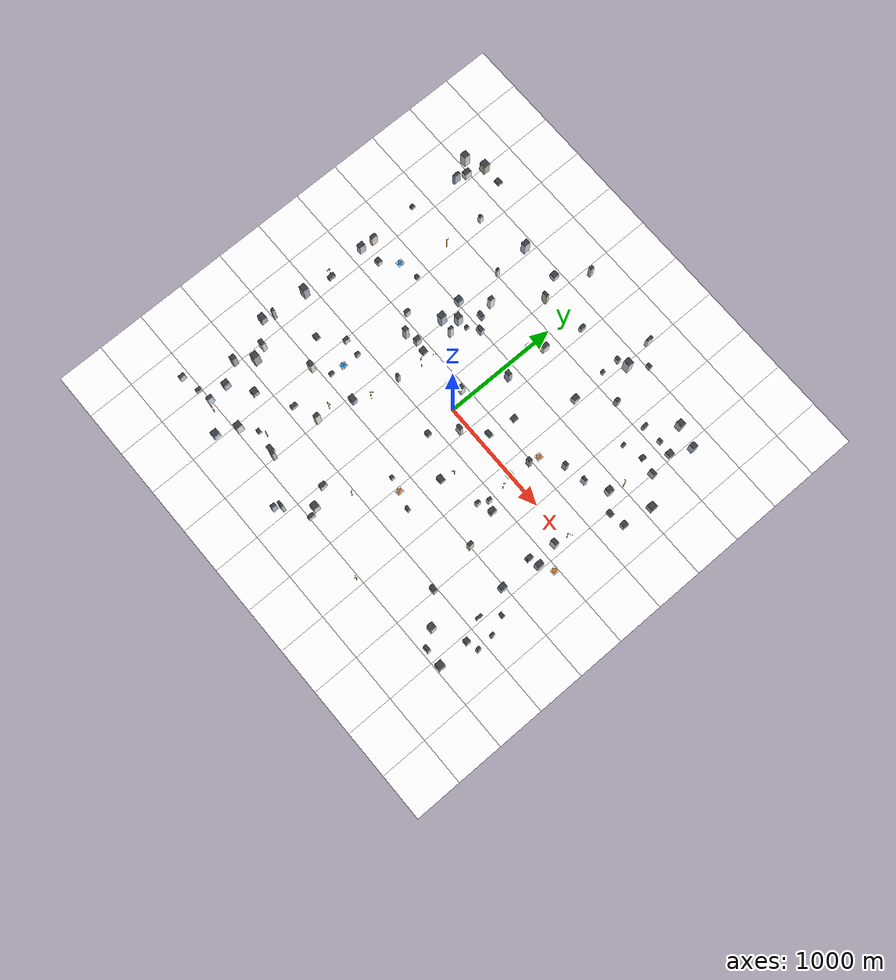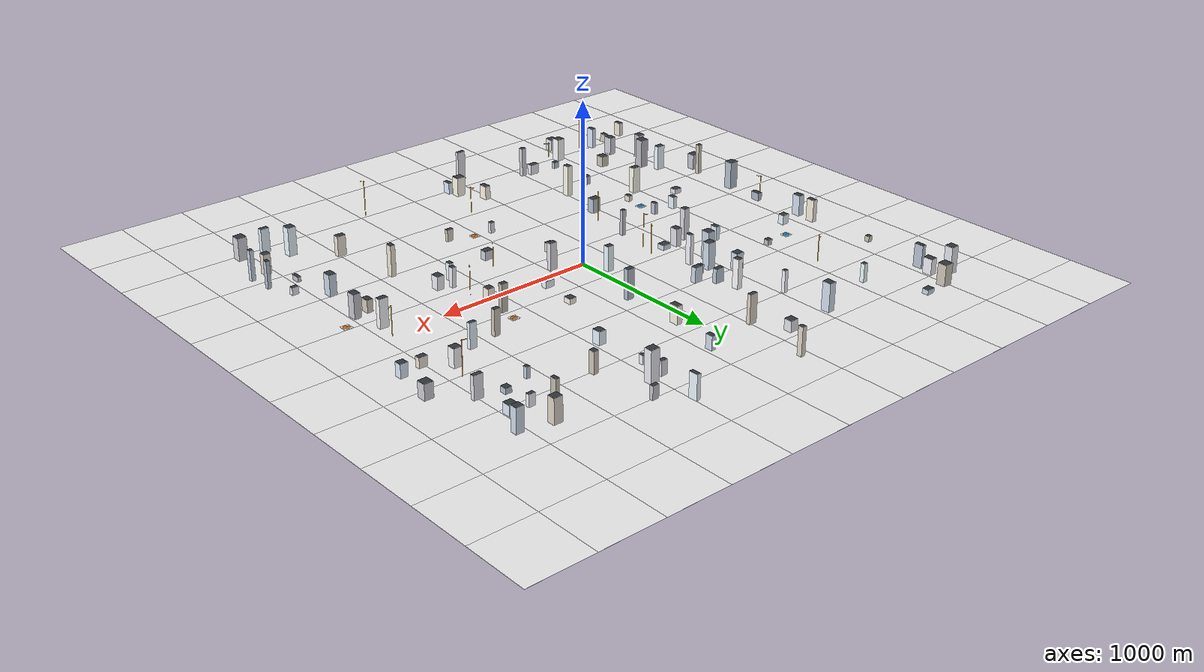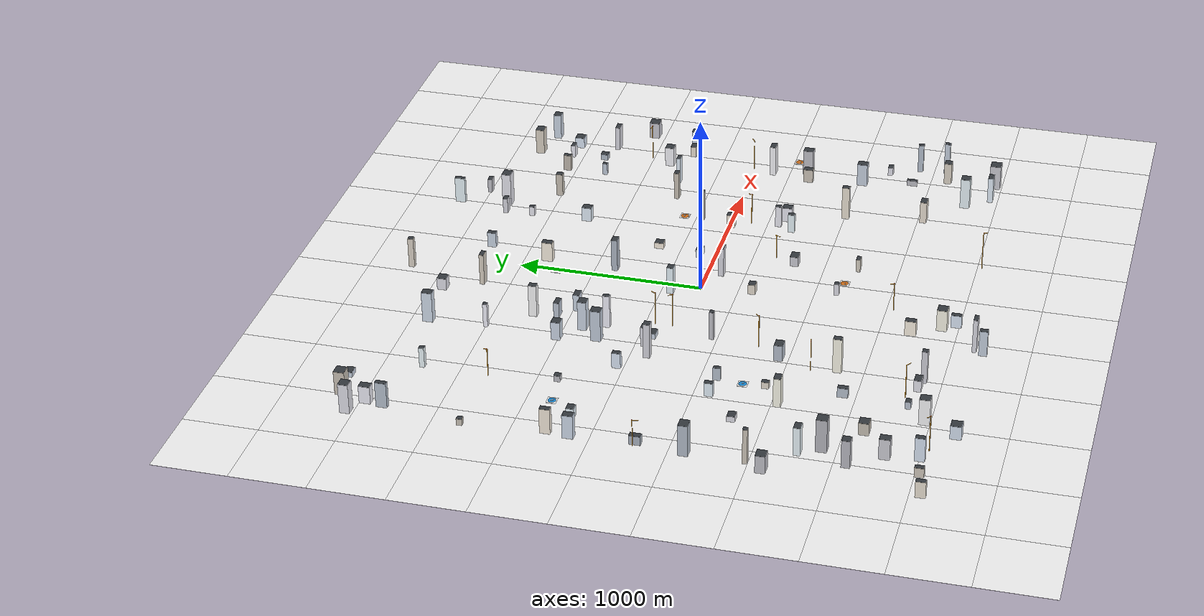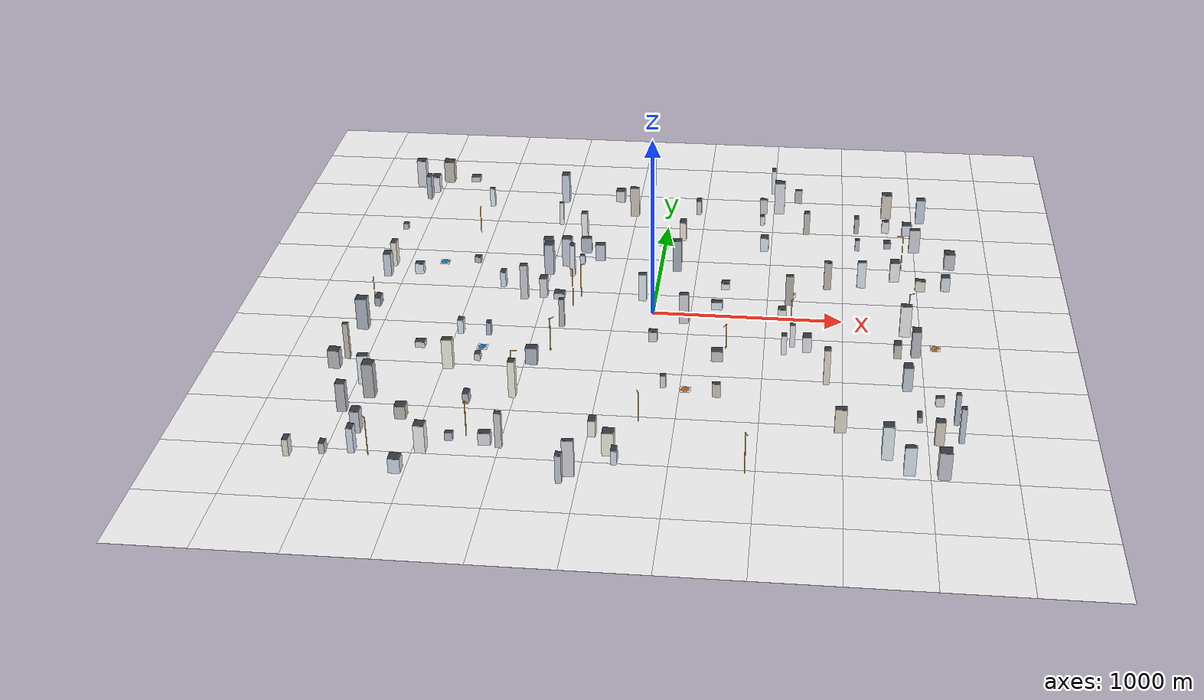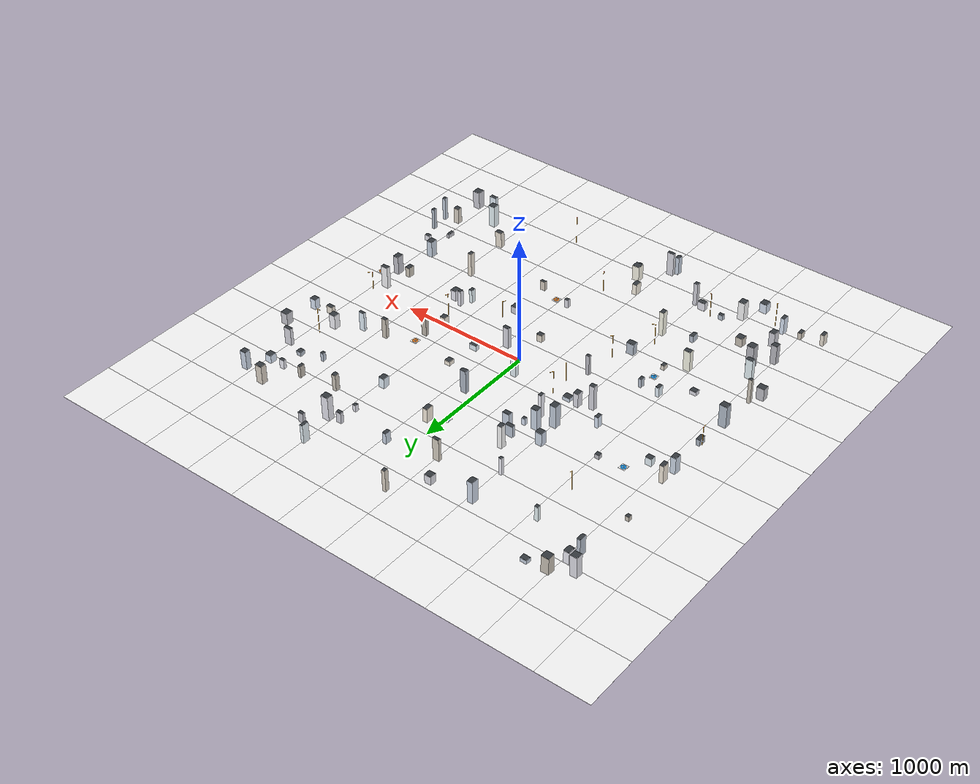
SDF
<?xml version='1.0'?>
<sdf version='1.9'>
<world name='urban'>
  <physics name='fast' type='ignored'>
    <max_step_size>0.005000</max_step_size>
    <real_time_factor>0</real_time_factor>
  </physics>
  <plugin filename='gz-sim-physics-system' name='gz::sim::systems::Physics'/>
  <plugin filename='gz-sim-user-commands-system'
          name='gz::sim::systems::UserCommands'/>
  <plugin filename='gz-sim-scene-broadcaster-system'
          name='gz::sim::systems::SceneBroadcaster'/>
  <plugin filename='gz-sim-sensors-system' name='gz::sim::systems::Sensors'>
    <render_engine>ogre2</render_engine>
  </plugin>
  <plugin filename='gz-sim-imu-system' name='gz::sim::systems::Imu'/>
  <plugin filename='PhyWamTraffic' name='phywam::PhyWamTraffic'>
    <seed>4</seed>
    <n_traffic>5</n_traffic>
    <n_suas>6</n_suas>
    <extent>1600.0</extent>
    <corridor_alt>120.0</corridor_alt>
    <namespace>phywam</namespace>
    <p_conflict>0.55</p_conflict>
    <buildings>-844.6,-1269.9,18.5,13.9,41.3 -314.9,1337.5,26.2,25.5,67.7 117.4,-714.6,14.3,13.0,66.4 1367.9,1052.5,26.3,26.2,62.9 -608.5,406.3,24.9,27.2,179.6 -1322.5,338.7,23.8,20.6,60.2 -84.5,-1314.1,28.8,27.4,123.1 -639.2,1308.4,21.9,27.8,174.2 26.8,-275.4,22.4,19.2,57.4 -623.6,1000.3,11.8,11.9,136.5 -702.6,110.8,20.0,17.5,199.5 -974.2,-279.1,14.9,23.0,77.0 -461.3,790.2,17.1,21.6,183.7 -1276.9,-1402.8,15.3,25.5,134.6 -840.3,-540.6,14.4,19.7,37.3 631.3,1267.0,29.1,25.0,193.2 -1541.8,-675.2,29.4,25.7,99.8 1418.6,385.6,26.5,16.6,62.5 -178.7,-1163.4,18.3,29.3,86.3 -1569.9,-1456.6,14.2,25.9,91.7 -670.9,-1289.3,29.7,19.1,65.3 -1410.1,-1423.1,14.2,23.9,55.4 -1469.1,-29.9,15.7,30.0,50.8 93.6,876.1,18.8,29.8,111.2 -826.0,-286.0,11.7,19.0,72.3 1245.8,1059.4,20.5,11.6,73.2 -824.4,-934.2,15.4,27.5,54.1 -1435.9,1369.7,21.7,29.8,98.5 1283.0,492.7,26.0,25.1,114.0 -1302.7,-925.1,27.6,28.1,187.2 -522.9,502.1,26.2,23.2,168.5 89.7,495.1,24.0,16.1,186.9 1460.1,-1362.0,29.5,29.3,143.6 -1457.5,1276.7,13.4,29.4,143.4 -1406.5,-1064.8,23.1,21.8,156.9 1367.9,-900.7,11.1,28.5,32.2 1204.6,-1229.2,26.4,25.9,179.2 161.9,1211.9,14.8,23.8,86.2 1253.6,875.4,20.0,21.0,34.5 -1490.6,302.4,20.3,27.4,133.4 -1156.0,-439.8,25.6,20.9,31.8 1080.6,1048.2,12.6,21.3,94.8 919.6,-604.3,15.4,20.2,194.3 -1295.6,-1233.8,22.8,27.8,117.1 -211.3,1145.1,25.8,12.3,179.8 -973.3,-632.6,26.9,19.0,165.7 -1064.4,1197.7,14.4,13.8,114.0 -516.5,134.0,28.2,24.5,30.9 -602.2,143.8,20.2,24.6,112.3 -1357.8,-814.6,27.1,17.8,160.3 1554.6,405.4,23.9,22.6,83.3 1320.9,-105.5,28.3,16.8,177.5 917.9,361.6,19.4,13.7,161.1 -441.0,518.7,13.5,12.6,54.5 988.9,-1031.5,28.1,18.1,127.9 -478.6,386.7,12.8,18.6,189.2 -1025.0,493.6,17.2,16.7,33.9 -1535.7,1438.1,26.8,26.2,167.2 1450.7,-1092.9,22.1,20.4,127.6 1401.3,832.8,29.4,13.2,140.8 561.3,784.6,22.7,26.8,81.5 1369.0,-300.4,22.4,28.0,149.6 -609.0,-862.8,17.2,22.9,199.4 1276.9,-319.3,18.6,26.5,78.2 -283.0,-1557.8,14.5,21.3,147.9 367.2,-434.2,29.1,22.8,56.5 -1383.3,1516.1,29.8,28.5,132.6 -600.8,-1307.7,15.9,15.2,187.8 1469.7,-760.5,21.0,14.0,46.4 -1498.4,-587.1,13.3,12.2,198.7 1448.4,1211.1,24.7,21.6,147.9 715.9,167.5,20.5,13.9,173.5 -50.6,-1383.0,14.2,27.6,73.5 -347.8,582.9,27.4,17.2,95.8 -246.1,-1510.2,27.7,11.4,193.2 -1112.0,-1098.6,27.1,26.6,69.4 171.3,-74.5,24.7,14.5,170.3 1588.6,660.7,28.5,28.8,94.5 1317.6,-623.5,23.3,28.0,132.0 -1480.9,422.2,15.9,27.3,142.5 1253.2,1258.2,27.8,23.5,148.8 335.0,86.7,29.8,17.7,43.9 683.2,-6.1,21.4,22.4,72.5 -957.3,-1371.7,25.9,28.3,148.4 -1226.3,1531.3,26.7,20.7,30.2 1100.3,394.8,22.8,11.3,154.6 794.9,1010.9,16.7,18.4,132.8 -1491.1,-280.7,29.5,25.3,176.7 -643.9,610.3,26.0,24.4,104.4 -1040.4,-1542.6,27.9,28.7,76.9 818.5,-297.2,22.9,27.0,84.6 384.4,-780.8,20.7,11.6,74.8 1556.3,-1068.8,12.8,15.0,188.6 540.0,1249.8,20.5,13.2,87.9 -142.0,1569.0,14.2,15.6,173.4 1302.5,-1357.7,27.1,14.4,152.1 -1512.9,853.3,14.4,14.9,35.9 -561.9,-549.9,29.7,22.5,91.9 589.2,1531.6,12.1,28.2,149.7 537.9,1098.0,13.0,14.8,53.4 -67.9,147.7,21.3,17.9,156.4 1083.0,827.3,11.7,13.9,67.3 -837.5,236.2,14.7,22.9,88.5 -436.2,665.9,28.9,14.6,89.2 1541.0,-919.6,11.5,14.6,170.3 740.1,1403.0,20.4,11.8,82.1 701.5,-343.0,13.7,18.1,108.8 -461.0,-171.5,13.6,11.6,163.2 743.2,-261.1,13.2,16.6,124.9 368.2,320.3,22.4,24.8,33.9</buildings>
  </plugin>

  <gravity>0 0 -9.80665</gravity>
  <scene>
    <ambient>0.38 0.40 0.44 1</ambient>
    <background>0.46 0.60 0.78 1</background>
    <grid>false</grid><sky></sky>
  </scene>
  <light type='directional' name='sun'>
    <cast_shadows>true</cast_shadows>
    <pose>0 0 400 0 0 0</pose>
    <diffuse>0.88 0.86 0.80 1</diffuse><specular>0.18 0.18 0.18 1</specular>
    <direction>-0.42 0.38 -0.82</direction>
  </light>
  <model name='ground'><static>true</static>
    <link name='l'>
      <collision name='c'><geometry><plane><normal>0 0 1</normal>
      <size>9000 9000</size></plane></geometry></collision>
<visual name='g_0_0'><pose>-2000.0 -2000.0 -0.2 0 0 0</pose><geometry><box><size>400.0 400.0 0.4</size></box></geometry><material><ambient>0.5 0.5 0.5 1</ambient><diffuse>1.000 1.000 1.000 1</diffuse><specular>0.06 0.06 0.06 1</specular><pbr><metal><albedo_map>/home/glaze/Desktop/github_projects/Phy_WAM/sim/materials/textures/ground.png</albedo_map><metalness>0.0</metalness><roughness>0.95</roughness></metal></pbr></material></visual><visual name='g_1_0'><pose>-1600.0 -2000.0 -0.2 0 0 0</pose><geometry><box><size>400.0 400.0 0.4</size></box></geometry><material><ambient>0.5 0.5 0.5 1</ambient><diffuse>1.000 1.000 1.000 1</diffuse><specular>0.06 0.06 0.06 1</specular><pbr><metal><albedo_map>/home/glaze/Desktop/github_projects/Phy_WAM/sim/materials/textures/ground.png</albedo_map><metalness>0.0</metalness><roughness>0.95</roughness></metal></pbr></material></visual><visual name='g_2_0'><pose>-1200.0 -2000.0 -0.2 0 0 0</pose><geometry><box><size>400.0 400.0 0.4</size></box></geometry><material><ambient>0.5 0.5 0.5 1</ambient><diffuse>1.000 1.000 1.000 1</diffuse><specular>0.06 0.06 0.06 1</specular><pbr><metal><albedo_map>/home/glaze/Desktop/github_projects/Phy_WAM/sim/materials/textures/ground.png</albedo_map><metalness>0.0</metalness><roughness>0.95</roughness></metal></pbr></material></visual><visual name='g_3_0'><pose>-800.0 -2000.0 -0.2 0 0 0</pose><geometry><box><size>400.0 400.0 0.4</size></box></geometry><material><ambient>0.5 0.5 0.5 1</ambient><diffuse>1.000 1.000 1.000 1</diffuse><specular>0.06 0.06 0.06 1</specular><pbr><metal><albedo_map>/home/glaze/Desktop/github_projects/Phy_WAM/sim/materials/textures/ground.png</albedo_map><metalness>0.0</metalness><roughness>0.95</roughness></metal></pbr></material></visual><visual name='g_4_0'><pose>-400.0 -2000.0 -0.2 0 0 0</pose><geometry><box><size>400.0 400.0 0.4</size></box></geometry><material><ambient>0.5 0.5 0.5 1</ambient><diffuse>1.000 1.000 1.000 1</diffuse><specular>0.06 0.06 0.06 1</specular><pbr><metal><albedo_map>/home/glaze/Desktop/github_projects/Phy_WAM/sim/materials/textures/ground.png</albedo_map><metalness>0.0</metalness><roughness>0.95</roughness></metal></pbr></material></visual><visual name='g_5_0'><pose>0.0 -2000.0 -0.2 0 0 0</pose><geometry><box><size>400.0 400.0 0.4</size></box></geometry><material><ambient>0.5 0.5 0.5 1</ambient><diffuse>1.000 1.000 1.000 1</diffuse><specular>0.06 0.06 0.06 1</specular><pbr><metal><albedo_map>/home/glaze/Desktop/github_projects/Phy_WAM/sim/materials/textures/ground.png</albedo_map><metalness>0.0</metalness><roughness>0.95</roughness></metal></pbr></material></visual><visual name='g_6_0'><pose>400.0 -2000.0 -0.2 0 0 0</pose><geometry><box><size>400.0 400.0 0.4</size></box></geometry><material><ambient>0.5 0.5 0.5 1</ambient><diffuse>1.000 1.000 1.000 1</diffuse><specular>0.06 0.06 0.06 1</specular><pbr><metal><albedo_map>/home/glaze/Desktop/github_projects/Phy_WAM/sim/materials/textures/ground.png</albedo_map><metalness>0.0</metalness><roughness>0.95</roughness></metal></pbr></material></visual><visual name='g_7_0'><pose>800.0 -2000.0 -0.2 0 0 0</pose><geometry><box><size>400.0 400.0 0.4</size></box></geometry><material><ambient>0.5 0.5 0.5 1</ambient><diffuse>1.000 1.000 1.000 1</diffuse><specular>0.06 0.06 0.06 1</specular><pbr><metal><albedo_map>/home/glaze/Desktop/github_projects/Phy_WAM/sim/materials/textures/ground.png</albedo_map><metalness>0.0</metalness><roughness>0.95</roughness></metal></pbr></material></visual><visual name='g_8_0'><pose>1200.0 -2000.0 -0.2 0 0 0</pose><geometry><box><size>400.0 400.0 0.4</size></box></geometry><material><ambient>0.5 0.5 0.5 1</ambient><diffuse>1.000 1.000 1.000 1</diffuse><specular>0.06 0.06 0.06 1</specular><pbr><metal><albedo_map>/home/glaze/Desktop/github_projects/Phy_WAM/sim/materials/textures/ground.png</albedo_map><metalness>0.0</metalness><roughness>0.95</roughness></metal></pbr></material></visual><visual name='g_9_0'><pose>1600.0 -2000.0 -0.2 0 0 0</pose><geometry><box><size>400.0 400.0 0.4</size></box></geometry><material><ambient>0.5 0.5 0.5 1</ambient><diffuse>1.000 1.000 1.000 1</diffuse><specular>0.06 0.06 0.06 1</specular><pbr><metal><albedo_map>/home/glaze/Desktop/github_projects/Phy_WAM/sim/materials/textures/ground.png</albedo_map><metalness>0.0</metalness><roughness>0.95</roughness></metal></pbr></material></visual><visual name='g_10_0'><pose>2000.0 -2000.0 -0.2 0 0 0</pose><geometry><box><size>400.0 400.0 0.4</size></box></geometry><material><ambient>0.5 0.5 0.5 1</ambient><diffuse>1.000 1.000 1.000 1</diffuse><specular>0.06 0.06 0.06 1</specular><pbr><metal><albedo_map>/home/glaze/Desktop/github_projects/Phy_WAM/sim/materials/textures/ground.png</albedo_map><metalness>0.0</metalness><roughness>0.95</roughness></metal></pbr></material></visual><visual name='g_0_1'><pose>-2000.0 -1600.0 -0.2 0 0 0</pose><geometry><box><size>400.0 400.0 0.4</size></box></geometry><material><ambient>0.5 0.5 0.5 1</ambient><diffuse>1.000 1.000 1.000 1</diffuse><specular>0.06 0.06 0.06 1</specular><pbr><metal><albedo_map>/home/glaze/Desktop/github_projects/Phy_WAM/sim/materials/textures/ground.png</albedo_map><metalness>0.0</metalness><roughness>0.95</roughness></metal></pbr></material></visual><visual name='g_1_1'><pose>-1600.0 -1600.0 -0.2 0 0 0</pose><geometry><box><size>400.0 400.0 0.4</size></box></geometry><material><ambient>0.5 0.5 0.5 1</ambient><diffuse>1.000 1.000 1.000 1</diffuse><specular>0.06 0.06 0.06 1</specular><pbr><metal><albedo_map>/home/glaze/Desktop/github_projects/Phy_WAM/sim/materials/textures/ground.png</albedo_map><metalness>0.0</metalness><roughness>0.95</roughness></metal></pbr></material></visual><visual name='g_2_1'><pose>-1200.0 -1600.0 -0.2 0 0 0</pose><geometry><box><size>400.0 400.0 0.4</size></box></geometry><material><ambient>0.5 0.5 0.5 1</ambient><diffuse>1.000 1.000 1.000 1</diffuse><specular>0.06 0.06 0.06 1</specular><pbr><metal><albedo_map>/home/glaze/Desktop/github_projects/Phy_WAM/sim/materials/textures/ground.png</albedo_map><metalness>0.0</metalness><roughness>0.95</roughness></metal></pbr></material></visual><visual name='g_3_1'><pose>-800.0 -1600.0 -0.2 0 0 0</pose><geometry><box><size>400.0 400.0 0.4</size></box></geometry><material><ambient>0.5 0.5 0.5 1</ambient><diffuse>1.000 1.000 1.000 1</diffuse><specular>0.06 0.06 0.06 1</specular><pbr><metal><albedo_map>/home/glaze/Desktop/github_projects/Phy_WAM/sim/materials/textures/ground.png</albedo_map><metalness>0.0</metalness><roughness>0.95</roughness></metal></pbr></material></visual><visual name='g_4_1'><pose>-400.0 -1600.0 -0.2 0 0 0</pose><geometry><box><size>400.0 400.0 0.4</size></box></geometry><material><ambient>0.5 0.5 0.5 1</ambient><diffuse>1.000 1.000 1.000 1</diffuse><specular>0.06 0.06 0.06 1</specular><pbr><metal><albedo_map>/home/glaze/Desktop/github_projects/Phy_WAM/sim/materials/textures/ground.png</albedo_map><metalness>0.0</metalness><roughness>0.95</roughness></metal></pbr></material></visual><visual name='g_5_1'><pose>0.0 -1600.0 -0.2 0 0 0</pose><geometry><box><size>400.0 400.0 0.4</size></box></geometry><material><ambient>0.5 0.5 0.5 1</ambient><diffuse>1.000 1.000 1.000 1</diffuse><specular>0.06 0.06 0.06 1</specular><pbr><metal><albedo_map>/home/glaze/Desktop/github_projects/Phy_WAM/sim/materials/textures/ground.png</albedo_map><metalness>0.0</metalness><roughness>0.95</roughness></metal></pbr></material></visual><visual name='g_6_1'><pose>400.0 -1600.0 -0.2 0 0 0</pose><geometry><box><size>400.0 400.0 0.4</size></box></geometry><material><ambient>0.5 0.5 0.5 1</ambient><diffuse>1.000 1.000 1.000 1</diffuse><specular>0.06 0.06 0.06 1</specular><pbr><metal><albedo_map>/home/glaze/Desktop/github_projects/Phy_WAM/sim/materials/textures/ground.png</albedo_map><metalness>0.0</metalness><roughness>0.95</roughness></metal></pbr></material></visual><visual name='g_7_1'><pose>800.0 -1600.0 -0.2 0 0 0</pose><geometry><box><size>400.0 400.0 0.4</size></box></geometry><material><ambient>0.5 0.5 0.5 1</ambient><diffuse>1.000 1.000 1.000 1</diffuse><specular>0.06 0.06 0.06 1</specular><pbr><metal><albedo_map>/home/glaze/Desktop/github_projects/Phy_WAM/sim/materials/textures/ground.png</albedo_map><metalness>0.0</metalness><roughness>0.95</roughness></metal></pbr></material></visual><visual name='g_8_1'><pose>1200.0 -1600.0 -0.2 0 0 0</pose><geometry><box><size>400.0 400.0 0.4</size></box></geometry><material><ambient>0.5 0.5 0.5 1</ambient><diffuse>1.000 1.000 1.000 1</diffuse><specular>0.06 0.06 0.06 1</specular><pbr><metal><albedo_map>/home/glaze/Desktop/github_projects/Phy_WAM/sim/materials/textures/ground.png</albedo_map><metalness>0.0</metalness><roughness>0.95</roughness></metal></pbr></material></visual><visual name='g_9_1'><pose>1600.0 -1600.0 -0.2 0 0 0</pose><geometry><box><size>400.0 400.0 0.4</size></box></geometry><material><ambient>0.5 0.5 0.5 1</ambient><diffuse>1.000 1.000 1.000 1</diffuse><specular>0.06 0.06 0.06 1</specular><pbr><metal><albedo_map>/home/glaze/Desktop/github_projects/Phy_WAM/sim/materials/textures/ground.png</albedo_map><metalness>0.0</metalness><roughness>0.95</roughness></metal></pbr></material></visual><visual name='g_10_1'><pose>2000.0 -1600.0 -0.2 0 0 0</pose><geometry><box><size>400.0 400.0 0.4</size></box></geometry><material><ambient>0.5 0.5 0.5 1</ambient><diffuse>1.000 1.000 1.000 1</diffuse><specular>0.06 0.06 0.06 1</specular><pbr><metal><albedo_map>/home/glaze/Desktop/github_projects/Phy_WAM/sim/materials/textures/ground.png</albedo_map><metalness>0.0</metalness><roughness>0.95</roughness></metal></pbr></material></visual><visual name='g_0_2'><pose>-2000.0 -1200.0 -0.2 0 0 0</pose><geometry><box><size>400.0 400.0 0.4</size></box></geometry><material><ambient>0.5 0.5 0.5 1</ambient><diffuse>1.000 1.000 1.000 1</diffuse><specular>0.06 0.06 0.06 1</specular><pbr><metal><albedo_map>/home/glaze/Desktop/github_projects/Phy_WAM/sim/materials/textures/ground.png</albedo_map><metalness>0.0</metalness><roughness>0.95</roughness></metal></pbr></material></visual><visual name='g_1_2'><pose>-1600.0 -1200.0 -0.2 0 0 0</pose><geometry><box><size>400.0 400.0 0.4</size></box></geometry><material><ambient>0.5 0.5 0.5 1</ambient><diffuse>1.000 1.000 1.000 1</diffuse><specular>0.06 0.06 0.06 1</specular><pbr><metal><albedo_map>/home/glaze/Desktop/github_projects/Phy_WAM/sim/materials/textures/ground.png</albedo_map><metalness>0.0</metalness><roughness>0.95</roughness></metal></pbr></material></visual><visual name='g_2_2'><pose>-1200.0 -1200.0 -0.2 0 0 0</pose><geometry><box><size>400.0 400.0 0.4</size></box></geometry><material><ambient>0.5 0.5 0.5 1</ambient><diffuse>1.000 1.000 1.000 1</diffuse><specular>0.06 0.06 0.06 1</specular><pbr><metal><albedo_map>/home/glaze/Desktop/github_projects/Phy_WAM/sim/materials/textures/ground.png</albedo_map><metalness>0.0</metalness><roughness>0.95</roughness></metal></pbr></material></visual><visual name='g_3_2'><pose>-800.0 -1200.0 -0.2 0 0 0</pose><geometry><box><size>400.0 400.0 0.4</size></box></geometry><material><ambient>0.5 0.5 0.5 1</ambient><diffuse>1.000 1.000 1.000 1</diffuse><specular>0.06 0.06 0.06 1</specular><pbr><metal><albedo_map>/home/glaze/Desktop/github_projects/Phy_WAM/sim/materials/textures/ground.png</albedo_map><metalness>0.0</metalness><roughness>0.95</roughness></metal></pbr></material></visual><visual name='g_4_2'><pose>-400.0 -1200.0 -0.2 0 0 0</pose><geometry><box><size>400.0 400.0 0.4</size></box></geometry><material><ambient>0.5 0.5 0.5 1</ambient><diffuse>1.000 1.000 1.000 1</diffuse><specular>0.06 0.06 0.06 1</specular><pbr><metal><albedo_map>/home/glaze/Desktop/github_projects/Phy_WAM/sim/materials/textures/ground.png</albedo_map><metalness>0.0</metalness><roughness>0.95</roughness></metal></pbr></material></visual><visual name='g_5_2'><pose>0.0 -1200.0 -0.2 0 0 0</pose><geometry><box><size>400.0 400.0 0.4</size></box></geometry><material><ambient>0.5 0.5 0.5 1</ambient><diffuse>1.000 1.000 1.000 1</diffuse><specular>0.06 0.06 0.06 1</specular><pbr><metal><albedo_map>/home/glaze/Desktop/github_projects/Phy_WAM/sim/materials/textures/ground.png</albedo_map><metalness>0.0</metalness><roughness>0.95</roughness></metal></pbr></material></visual><visual name='g_6_2'><pose>400.0 -1200.0 -0.2 0 0 0</pose><geometry><box><size>400.0 400.0 0.4</size></box></geometry><material><ambient>0.5 0.5 0.5 1</ambient><diffuse>1.000 1.000 1.000 1</diffuse><specular>0.06 0.06 0.06 1</specular><pbr><metal><albedo_map>/home/glaze/Desktop/github_projects/Phy_WAM/sim/materials/textures/ground.png</albedo_map><metalness>0.0</metalness><roughness>0.95</roughness></metal></pbr></material></visual><visual name='g_7_2'><pose>800.0 -1200.0 -0.2 0 0 0</pose><geometry><box><size>400.0 400.0 0.4</size></box></geometry><material><ambient>0.5 0.5 0.5 1</ambient><diffuse>1.000 1.000 1.000 1</diffuse><specular>0.06 0.06 0.06 1</specular><pbr><metal><albedo_map>/home/glaze/Desktop/github_projects/Phy_WAM/sim/materials/textures/ground.png</albedo_map><metalness>0.0</metalness><roughness>0.95</roughness></metal></pbr></material></visual><visual name='g_8_2'><pose>1200.0 -1200.0 -0.2 0 0 0</pose><geometry><box><size>400.0 400.0 0.4</size></box></geometry><material><ambient>0.5 0.5 0.5 1</ambient><diffuse>1.000 1.000 1.000 1</diffuse><specular>0.06 0.06 0.06 1</specular><pbr><metal><albedo_map>/home/glaze/Desktop/github_projects/Phy_WAM/sim/materials/textures/ground.png</albedo_map><metalness>0.0</metalness><roughness>0.95</roughness></metal></pbr></material></visual><visual name='g_9_2'><pose>1600.0 -1200.0 -0.2 0 0 0</pose><geometry><box><size>400.0 400.0 0.4</size></box></geometry><material><ambient>0.5 0.5 0.5 1</ambient><diffuse>1.000 1.000 1.000 1</diffuse><specular>0.06 0.06 0.06 1</specular><pbr><metal><albedo_map>/home/glaze/Desktop/github_projects/Phy_WAM/sim/materials/textures/ground.png</albedo_map><metalness>0.0</metalness><roughness>0.95</roughness></metal></pbr></material></visual><visual name='g_10_2'><pose>2000.0 -1200.0 -0.2 0 0 0</pose><geometry><box><size>400.0 400.0 0.4</size></box></geometry><material><ambient>0.5 0.5 0.5 1</ambient><diffuse>1.000 1.000 1.000 1</diffuse><specular>0.06 0.06 0.06 1</specular><pbr><metal><albedo_map>/home/glaze/Desktop/github_projects/Phy_WAM/sim/materials/textures/ground.png</albedo_map><metalness>0.0</metalness><roughness>0.95</roughness></metal></pbr></material></visual><visual name='g_0_3'><pose>-2000.0 -800.0 -0.2 0 0 0</pose><geometry><box><size>400.0 400.0 0.4</size></box></geometry><material><ambient>0.5 0.5 0.5 1</ambient><diffuse>1.000 1.000 1.000 1</diffuse><specular>0.06 0.06 0.06 1</specular><pbr><metal><albedo_map>/home/glaze/Desktop/github_projects/Phy_WAM/sim/materials/textures/ground.png</albedo_map><metalness>0.0</metalness><roughness>0.95</roughness></metal></pbr></material></visual><visual name='g_1_3'><pose>-1600.0 -800.0 -0.2 0 0 0</pose><geometry><box><size>400.0 400.0 0.4</size></box></geometry><material><ambient>0.5 0.5 0.5 1</ambient><diffuse>1.000 1.000 1.000 1</diffuse><specular>0.06 0.06 0.06 1</specular><pbr><metal><albedo_map>/home/glaze/Desktop/github_projects/Phy_WAM/sim/materials/textures/ground.png</albedo_map><metalness>0.0</metalness><roughness>0.95</roughness></metal></pbr></material></visual><visual name='g_2_3'><pose>-1200.0 -800.0 -0.2 0 0 0</pose><geometry><box><size>400.0 400.0 0.4</size></box></geometry><material><ambient>0.5 0.5 0.5 1</ambient><diffuse>1.000 1.000 1.000 1</diffuse><specular>0.06 0.06 0.06 1</specular><pbr><metal><albedo_map>/home/glaze/Desktop/github_projects/Phy_WAM/sim/materials/textures/ground.png</albedo_map><metalness>0.0</metalness><roughness>0.95</roughness></metal></pbr></material></visual><visual name='g_3_3'><pose>-800.0 -800.0 -0.2 0 0 0</pose><geometry><box><size>400.0 400.0 0.4</size></box></geometry><material><ambient>0.5 0.5 0.5 1</ambient><diffuse>1.000 1.000 1.000 1</diffuse><specular>0.06 0.06 0.06 1</specular><pbr><metal><albedo_map>/home/glaze/Desktop/github_projects/Phy_WAM/sim/materials/textures/ground.png</albedo_map><metalness>0.0</metalness><roughness>0.95</roughness></metal></pbr></material></visual><visual name='g_4_3'><pose>-400.0 -800.0 -0.2 0 0 0</pose><geometry><box><size>400.0 400.0 0.4</size></box></geometry><material><ambient>0.5 0.5 0.5 1</ambient><diffuse>1.000 1.000 1.000 1</diffuse><specular>0.06 0.06 0.06 1</specular><pbr><metal><albedo_map>/home/glaze/Desktop/github_projects/Phy_WAM/sim/materials/textures/ground.png</albedo_map><metalness>0.0</metalness><roughness>0.95</roughness></metal></pbr></material></visual><visual name='g_5_3'><pose>0.0 -800.0 -0.2 0 0 0</pose><geometry><box><size>400.0 400.0 0.4</size></box></geometry><material><ambient>0.5 0.5 0.5 1</ambient><diffuse>1.000 1.000 1.000 1</diffuse><specular>0.06 0.06 0.06 1</specular><pbr><metal><albedo_map>/home/glaze/Desktop/github_projects/Phy_WAM/sim/materials/textures/ground.png</albedo_map><metalness>0.0</metalness><roughness>0.95</roughness></metal></pbr></material></visual><visual name='g_6_3'><pose>400.0 -800.0 -0.2 0 0 0</pose><geometry><box><size>400.0 400.0 0.4</size></box></geometry><material><ambient>0.5 0.5 0.5 1</ambient><diffuse>1.000 1.000 1.000 1</diffuse><specular>0.06 0.06 0.06 1</specular><pbr><metal><albedo_map>/home/glaze/Desktop/github_projects/Phy_WAM/sim/materials/textures/ground.png</albedo_map><metalness>0.0</metalness><roughness>0.95</roughness></metal></pbr></material></visual><visual name='g_7_3'><pose>800.0 -800.0 -0.2 0 0 0</pose><geometry><box><size>400.0 400.0 0.4</size></box></geometry><material><ambient>0.5 0.5 0.5 1</ambient><diffuse>1.000 1.000 1.000 1</diffuse><specular>0.06 0.06 0.06 1</specular><pbr><metal><albedo_map>/home/glaze/Desktop/github_projects/Phy_WAM/sim/materials/textures/ground.png</albedo_map><metalness>0.0</metalness><roughness>0.95</roughness></metal></pbr></material></visual><visual name='g_8_3'><pose>1200.0 -800.0 -0.2 0 0 0</pose><geometry><box><size>400.0 400.0 0.4</size></box></geometry><material><ambient>0.5 0.5 0.5 1</ambient><diffuse>1.000 1.000 1.000 1</diffuse><specular>0.06 0.06 0.06 1</specular><pbr><metal><albedo_map>/home/glaze/Desktop/github_projects/Phy_WAM/sim/materials/textures/ground.png</albedo_map><metalness>0.0</metalness><roughness>0.95</roughness></metal></pbr></material></visual><visual name='g_9_3'><pose>1600.0 -800.0 -0.2 0 0 0</pose><geometry><box><size>400.0 400.0 0.4</size></box></geometry><material><ambient>0.5 0.5 0.5 1</ambient><diffuse>1.000 1.000 1.000 1</diffuse><specular>0.06 0.06 0.06 1</specular><pbr><metal><albedo_map>/home/glaze/Desktop/github_projects/Phy_WAM/sim/materials/textures/ground.png</albedo_map><metalness>0.0</metalness><roughness>0.95</roughness></metal></pbr></material></visual><visual name='g_10_3'><pose>2000.0 -800.0 -0.2 0 0 0</pose><geometry><box><size>400.0 400.0 0.4</size></box></geometry><material><ambient>0.5 0.5 0.5 1</ambient><diffuse>1.000 1.000 1.000 1</diffuse><specular>0.06 0.06 0.06 1</specular><pbr><metal><albedo_map>/home/glaze/Desktop/github_projects/Phy_WAM/sim/materials/textures/ground.png</albedo_map><metalness>0.0</metalness><roughness>0.95</roughness></metal></pbr></material></visual><visual name='g_0_4'><pose>-2000.0 -400.0 -0.2 0 0 0</pose><geometry><box><size>400.0 400.0 0.4</size></box></geometry><material><ambient>0.5 0.5 0.5 1</ambient><diffuse>1.000 1.000 1.000 1</diffuse><specular>0.06 0.06 0.06 1</specular><pbr><metal><albedo_map>/home/glaze/Desktop/github_projects/Phy_WAM/sim/materials/textures/ground.png</albedo_map><metalness>0.0</metalness><roughness>0.95</roughness></metal></pbr></material></visual><visual name='g_1_4'><pose>-1600.0 -400.0 -0.2 0 0 0</pose><geometry><box><size>400.0 400.0 0.4</size></box></geometry><material><ambient>0.5 0.5 0.5 1</ambient><diffuse>1.000 1.000 1.000 1</diffuse><specular>0.06 0.06 0.06 1</specular><pbr><metal><albedo_map>/home/glaze/Desktop/github_projects/Phy_WAM/sim/materials/textures/ground.png</albedo_map><metalness>0.0</metalness><roughness>0.95</roughness></metal></pbr></material></visual><visual name='g_2_4'><pose>-1200.0 -400.0 -0.2 0 0 0</pose><geometry><box><size>400.0 400.0 0.4</size></box></geometry><material><ambient>0.5 0.5 0.5 1</ambient><diffuse>1.000 1.000 1.000 1</diffuse><specular>0.06 0.06 0.06 1</specular><pbr><metal><albedo_map>/home/glaze/Desktop/github_projects/Phy_WAM/sim/materials/textures/ground.png</albedo_map><metalness>0.0</metalness><roughness>0.95</roughness></metal></pbr></material></visual><visual name='g_3_4'><pose>-800.0 -400.0 -0.2 0 0 0</pose><geometry><box><size>400.0 400.0 0.4</size></box></geometry><material><ambient>0.5 0.5 0.5 1</ambient><diffuse>1.000 1.000 1.000 1</diffuse><specular>0.06 0.06 0.06 1</specular><pbr><metal><albedo_map>/home/glaze/Desktop/github_projects/Phy_WAM/sim/materials/textures/ground.png</albedo_map><metalness>0.0</metalness><roughness>0.95</roughness></metal></pbr></material></visual><visual name='g_4_4'><pose>-400.0 -400.0 -0.2 0 0 0</pose><geometry><box><size>400.0 400.0 0.4</size></box></geometry><material><ambient>0.5 0.5 0.5 1</ambient><diffuse>1.000 1.000 1.000 1</diffuse><specular>0.06 0.06 0.06 1</specular><pbr><metal><albedo_map>/home/glaze/Desktop/github_projects/Phy_WAM/sim/materials/textures/ground.png</albedo_map><metalness>0.0</metalness><roughness>0.95</roughness></metal></pbr></material></visual><visual name='g_5_4'><pose>0.0 -400.0 -0.2 0 0 0</pose><geometry><box><size>400.0 400.0 0.4</size></box></geometry><material><ambient>0.5 0.5 0.5 1</ambient><diffuse>1.000 1.000 1.000 1</diffuse><specular>0.06 0.06 0.06 1</specular><pbr><metal><albedo_map>/home/glaze/Desktop/github_projects/Phy_WAM/sim/materials/textures/ground.png</albedo_map><metalness>0.0</metalness><roughness>0.95</roughness></metal></pbr></material></visual><visual name='g_6_4'><pose>400.0 -400.0 -0.2 0 0 0</pose><geometry><box><size>400.0 400.0 0.4</size></box></geometry><material><ambient>0.5 0.5 0.5 1</ambient><diffuse>1.000 1.000 1.000 1</diffuse><specular>0.06 0.06 0.06 1</specular><pbr><metal><albedo_map>/home/glaze/Desktop/github_projects/Phy_WAM/sim/materials/textures/ground.png</albedo_map><metalness>0.0</metalness><roughness>0.95</roughness></metal></pbr></material></visual><visual name='g_7_4'><pose>800.0 -400.0 -0.2 0 0 0</pose><geometry><box><size>400.0 400.0 0.4</size></box></geometry><material><ambient>0.5 0.5 0.5 1</ambient><diffuse>1.000 1.000 1.000 1</diffuse><specular>0.06 0.06 0.06 1</specular><pbr><metal><albedo_map>/home/glaze/Desktop/github_projects/Phy_WAM/sim/materials/textures/ground.png</albedo_map><metalness>0.0</metalness><roughness>0.95</roughness></metal></pbr></material></visual><visual name='g_8_4'><pose>1200.0 -400.0 -0.2 0 0 0</pose><geometry><box><size>400.0 400.0 0.4</size></box></geometry><material><ambient>0.5 0.5 0.5 1</ambient><diffuse>1.000 1.000 1.000 1</diffuse><specular>0.06 0.06 0.06 1</specular><pbr><metal><albedo_map>/home/glaze/Desktop/github_projects/Phy_WAM/sim/materials/textures/ground.png</albedo_map><metalness>0.0</metalness><roughness>0.95</roughness></metal></pbr></material></visual><visual name='g_9_4'><pose>1600.0 -400.0 -0.2 0 0 0</pose><geometry><box><size>400.0 400.0 0.4</size></box></geometry><material><ambient>0.5 0.5 0.5 1</ambient><diffuse>1.000 1.000 1.000 1</diffuse><specular>0.06 0.06 0.06 1</specular><pbr><metal><albedo_map>/home/glaze/Desktop/github_projects/Phy_WAM/sim/materials/textures/ground.png</albedo_map><metalness>0.0</metalness><roughness>0.95</roughness></metal></pbr></material></visual><visual name='g_10_4'><pose>2000.0 -400.0 -0.2 0 0 0</pose><geometry><box><size>400.0 400.0 0.4</size></box></geometry><material><ambient>0.5 0.5 0.5 1</ambient><diffuse>1.000 1.000 1.000 1</diffuse><specular>0.06 0.06 0.06 1</specular><pbr><metal><albedo_map>/home/glaze/Desktop/github_projects/Phy_WAM/sim/materials/textures/ground.png</albedo_map><metalness>0.0</metalness><roughness>0.95</roughness></metal></pbr></material></visual><visual name='g_0_5'><pose>-2000.0 0.0 -0.2 0 0 0</pose><geometry><box><size>400.0 400.0 0.4</size></box></geometry><material><ambient>0.5 0.5 0.5 1</ambient><diffuse>1.000 1.000 1.000 1</diffuse><specular>0.06 0.06 0.06 1</specular><pbr><metal><albedo_map>/home/glaze/Desktop/github_projects/Phy_WAM/sim/materials/textures/ground.png</albedo_map><metalness>0.0</metalness><roughness>0.95</roughness></metal></pbr></material></visual><visual name='g_1_5'><pose>-1600.0 0.0 -0.2 0 0 0</pose><geometry><box><size>400.0 400.0 0.4</size></box></geometry><material><ambient>0.5 0.5 0.5 1</ambient><diffuse>1.000 1.000 1.000 1</diffuse><specular>0.06 0.06 0.06 1</specular><pbr><metal><albedo_map>/home/glaze/Desktop/github_projects/Phy_WAM/sim/materials/textures/ground.png</albedo_map><metalness>0.0</metalness><roughness>0.95</roughness></metal></pbr></material></visual><visual name='g_2_5'><pose>-1200.0 0.0 -0.2 0 0 0</pose><geometry><box><size>400.0 400.0 0.4</size></box></geometry><material><ambient>0.5 0.5 0.5 1</ambient><diffuse>1.000 1.000 1.000 1</diffuse><specular>0.06 0.06 0.06 1</specular><pbr><metal><albedo_map>/home/glaze/Desktop/github_projects/Phy_WAM/sim/materials/textures/ground.png</albedo_map><metalness>0.0</metalness><roughness>0.95</roughness></metal></pbr></material></visual><visual name='g_3_5'><pose>-800.0 0.0 -0.2 0 0 0</pose><geometry><box><size>400.0 400.0 0.4</size></box></geometry><material><ambient>0.5 0.5 0.5 1</ambient><diffuse>1.000 1.000 1.000 1</diffuse><specular>0.06 0.06 0.06 1</specular><pbr><metal><albedo_map>/home/glaze/Desktop/github_projects/Phy_WAM/sim/materials/textures/ground.png</albedo_map><metalness>0.0</metalness><roughness>0.95</roughness></metal></pbr></material></visual><visual name='g_4_5'><pose>-400.0 0.0 -0.2 0 0 0</pose><geometry><box><size>400.0 400.0 0.4</size></box></geometry><material><ambient>0.5 0.5 0.5 1</ambient><diffuse>1.000 1.000 1.000 1</diffuse><specular>0.06 0.06 0.06 1</specular><pbr><metal><albedo_map>/home/glaze/Desktop/github_projects/Phy_WAM/sim/materials/textures/ground.png</albedo_map><metalness>0.0</metalness><roughness>0.95</roughness></metal></pbr></material></visual><visual name='g_5_5'><pose>0.0 0.0 -0.2 0 0 0</pose><geometry><box><size>400.0 400.0 0.4</size></box></geometry><material><ambient>0.5 0.5 0.5 1</ambient><diffuse>1.000 1.000 1.000 1</diffuse><specular>0.06 0.06 0.06 1</specular><pbr><metal><albedo_map>/home/glaze/Desktop/github_projects/Phy_WAM/sim/materials/textures/ground.png</albedo_map><metalness>0.0</metalness><roughness>0.95</roughness></metal></pbr></material></visual><visual name='g_6_5'><pose>400.0 0.0 -0.2 0 0 0</pose><geometry><box><size>400.0 400.0 0.4</size></box></geometry><material><ambient>0.5 0.5 0.5 1</ambient><diffuse>1.000 1.000 1.000 1</diffuse><specular>0.06 0.06 0.06 1</specular><pbr><metal><albedo_map>/home/glaze/Desktop/github_projects/Phy_WAM/sim/materials/textures/ground.png</albedo_map><metalness>0.0</metalness><roughness>0.95</roughness></metal></pbr></material></visual><visual name='g_7_5'><pose>800.0 0.0 -0.2 0 0 0</pose><geometry><box><size>400.0 400.0 0.4</size></box></geometry><material><ambient>0.5 0.5 0.5 1</ambient><diffuse>1.000 1.000 1.000 1</diffuse><specular>0.06 0.06 0.06 1</specular><pbr><metal><albedo_map>/home/glaze/Desktop/github_projects/Phy_WAM/sim/materials/textures/ground.png</albedo_map><metalness>0.0</metalness><roughness>0.95</roughness></metal></pbr></material></visual><visual name='g_8_5'><pose>1200.0 0.0 -0.2 0 0 0</pose><geometry><box><size>400.0 400.0 0.4</size></box></geometry><material><ambient>0.5 0.5 0.5 1</ambient><diffuse>1.000 1.000 1.000 1</diffuse><specular>0.06 0.06 0.06 1</specular><pbr><metal><albedo_map>/home/glaze/Desktop/github_projects/Phy_WAM/sim/materials/textures/ground.png</albedo_map><metalness>0.0</metalness><roughness>0.95</roughness></metal></pbr></material></visual><visual name='g_9_5'><pose>1600.0 0.0 -0.2 0 0 0</pose><geometry><box><size>400.0 400.0 0.4</size></box></geometry><material><ambient>0.5 0.5 0.5 1</ambient><diffuse>1.000 1.000 1.000 1</diffuse><specular>0.06 0.06 0.06 1</specular><pbr><metal><albedo_map>/home/glaze/Desktop/github_projects/Phy_WAM/sim/materials/textures/ground.png</albedo_map><metalness>0.0</metalness><roughness>0.95</roughness></metal></pbr></material></visual><visual name='g_10_5'><pose>2000.0 0.0 -0.2 0 0 0</pose><geometry><box><size>400.0 400.0 0.4</size></box></geometry><material><ambient>0.5 0.5 0.5 1</ambient><diffuse>1.000 1.000 1.000 1</diffuse><specular>0.06 0.06 0.06 1</specular><pbr><metal><albedo_map>/home/glaze/Desktop/github_projects/Phy_WAM/sim/materials/textures/ground.png</albedo_map><metalness>0.0</metalness><roughness>0.95</roughness></metal></pbr></material></visual><visual name='g_0_6'><pose>-2000.0 400.0 -0.2 0 0 0</pose><geometry><box><size>400.0 400.0 0.4</size></box></geometry><material><ambient>0.5 0.5 0.5 1</ambient><diffuse>1.000 1.000 1.000 1</diffuse><specular>0.06 0.06 0.06 1</specular><pbr><metal><albedo_map>/home/glaze/Desktop/github_projects/Phy_WAM/sim/materials/textures/ground.png</albedo_map><metalness>0.0</metalness><roughness>0.95</roughness></metal></pbr></material></visual><visual name='g_1_6'><pose>-1600.0 400.0 -0.2 0 0 0</pose><geometry><box><size>400.0 400.0 0.4</size></box></geometry><material><ambient>0.5 0.5 0.5 1</ambient><diffuse>1.000 1.000 1.000 1</diffuse><specular>0.06 0.06 0.06 1</specular><pbr><metal><albedo_map>/home/glaze/Desktop/github_projects/Phy_WAM/sim/materials/textures/ground.png</albedo_map><metalness>0.0</metalness><roughness>0.95</roughness></metal></pbr></material></visual><visual name='g_2_6'><pose>-1200.0 400.0 -0.2 0 0 0</pose><geometry><box><size>400.0 400.0 0.4</size></box></geometry><material><ambient>0.5 0.5 0.5 1</ambient><diffuse>1.000 1.000 1.000 1</diffuse><specular>0.06 0.06 0.06 1</specular><pbr><metal><albedo_map>/home/glaze/Desktop/github_projects/Phy_WAM/sim/materials/textures/ground.png</albedo_map><metalness>0.0</metalness><roughness>0.95</roughness></metal></pbr></material></visual><visual name='g_3_6'><pose>-800.0 400.0 -0.2 0 0 0</pose><geometry><box><size>400.0 400.0 0.4</size></box></geometry><material><ambient>0.5 0.5 0.5 1</ambient><diffuse>1.000 1.000 1.000 1</diffuse><specular>0.06 0.06 0.06 1</specular><pbr><metal><albedo_map>/home/glaze/Desktop/github_projects/Phy_WAM/sim/materials/textures/ground.png</albedo_map><metalness>0.0</metalness><roughness>0.95</roughness></metal></pbr></material></visual><visual name='g_4_6'><pose>-400.0 400.0 -0.2 0 0 0</pose><geometry><box><size>400.0 400.0 0.4</size></box></geometry><material><ambient>0.5 0.5 0.5 1</ambient><diffuse>1.000 1.000 1.000 1</diffuse><specular>0.06 0.06 0.06 1</specular><pbr><metal><albedo_map>/home/glaze/Desktop/github_projects/Phy_WAM/sim/materials/textures/ground.png</albedo_map><metalness>0.0</metalness><roughness>0.95</roughness></metal></pbr></material></visual><visual name='g_5_6'><pose>0.0 400.0 -0.2 0 0 0</pose><geometry><box><size>400.0 400.0 0.4</size></box></geometry><material><ambient>0.5 0.5 0.5 1</ambient><diffuse>1.000 1.000 1.000 1</diffuse><specular>0.06 0.06 0.06 1</specular><pbr><metal><albedo_map>/home/glaze/Desktop/github_projects/Phy_WAM/sim/materials/textures/ground.png</albedo_map><metalness>0.0</metalness><roughness>0.95</roughness></metal></pbr></material></visual><visual name='g_6_6'><pose>400.0 400.0 -0.2 0 0 0</pose><geometry><box><size>400.0 400.0 0.4</size></box></geometry><material><ambient>0.5 0.5 0.5 1</ambient><diffuse>1.000 1.000 1.000 1</diffuse><specular>0.06 0.06 0.06 1</specular><pbr><metal><albedo_map>/home/glaze/Desktop/github_projects/Phy_WAM/sim/materials/textures/ground.png</albedo_map><metalness>0.0</metalness><roughness>0.95</roughness></metal></pbr></material></visual><visual name='g_7_6'><pose>800.0 400.0 -0.2 0 0 0</pose><geometry><box><size>400.0 400.0 0.4</size></box></geometry><material><ambient>0.5 0.5 0.5 1</ambient><diffuse>1.000 1.000 1.000 1</diffuse><specular>0.06 0.06 0.06 1</specular><pbr><metal><albedo_map>/home/glaze/Desktop/github_projects/Phy_WAM/sim/materials/textures/ground.png</albedo_map><metalness>0.0</metalness><roughness>0.95</roughness></metal></pbr></material></visual><visual name='g_8_6'><pose>1200.0 400.0 -0.2 0 0 0</pose><geometry><box><size>400.0 400.0 0.4</size></box></geometry><material><ambient>0.5 0.5 0.5 1</ambient><diffuse>1.000 1.000 1.000 1</diffuse><specular>0.06 0.06 0.06 1</specular><pbr><metal><albedo_map>/home/glaze/Desktop/github_projects/Phy_WAM/sim/materials/textures/ground.png</albedo_map><metalness>0.0</metalness><roughness>0.95</roughness></metal></pbr></material></visual><visual name='g_9_6'><pose>1600.0 400.0 -0.2 0 0 0</pose><geometry><box><size>400.0 400.0 0.4</size></box></geometry><material><ambient>0.5 0.5 0.5 1</ambient><diffuse>1.000 1.000 1.000 1</diffuse><specular>0.06 0.06 0.06 1</specular><pbr><metal><albedo_map>/home/glaze/Desktop/github_projects/Phy_WAM/sim/materials/textures/ground.png</albedo_map><metalness>0.0</metalness><roughness>0.95</roughness></metal></pbr></material></visual><visual name='g_10_6'><pose>2000.0 400.0 -0.2 0 0 0</pose><geometry><box><size>400.0 400.0 0.4</size></box></geometry><material><ambient>0.5 0.5 0.5 1</ambient><diffuse>1.000 1.000 1.000 1</diffuse><specular>0.06 0.06 0.06 1</specular><pbr><metal><albedo_map>/home/glaze/Desktop/github_projects/Phy_WAM/sim/materials/textures/ground.png</albedo_map><metalness>0.0</metalness><roughness>0.95</roughness></metal></pbr></material></visual><visual name='g_0_7'><pose>-2000.0 800.0 -0.2 0 0 0</pose><geometry><box><size>400.0 400.0 0.4</size></box></geometry><material><ambient>0.5 0.5 0.5 1</ambient><diffuse>1.000 1.000 1.000 1</diffuse><specular>0.06 0.06 0.06 1</specular><pbr><metal><albedo_map>/home/glaze/Desktop/github_projects/Phy_WAM/sim/materials/textures/ground.png</albedo_map><metalness>0.0</metalness><roughness>0.95</roughness></metal></pbr></material></visual><visual name='g_1_7'><pose>-1600.0 800.0 -0.2 0 0 0</pose><geometry><box><size>400.0 400.0 0.4</size></box></geometry><material><ambient>0.5 0.5 0.5 1</ambient><diffuse>1.000 1.000 1.000 1</diffuse><specular>0.06 0.06 0.06 1</specular><pbr><metal><albedo_map>/home/glaze/Desktop/github_projects/Phy_WAM/sim/materials/textures/ground.png</albedo_map><metalness>0.0</metalness><roughness>0.95</roughness></metal></pbr></material></visual><visual name='g_2_7'><pose>-1200.0 800.0 -0.2 0 0 0</pose><geometry><box><size>400.0 400.0 0.4</size></box></geometry><material><ambient>0.5 0.5 0.5 1</ambient><diffuse>1.000 1.000 1.000 1</diffuse><specular>0.06 0.06 0.06 1</specular><pbr><metal><albedo_map>/home/glaze/Desktop/github_projects/Phy_WAM/sim/materials/textures/ground.png</albedo_map><metalness>0.0</metalness><roughness>0.95</roughness></metal></pbr></material></visual><visual name='g_3_7'><pose>-800.0 800.0 -0.2 0 0 0</pose><geometry><box><size>400.0 400.0 0.4</size></box></geometry><material><ambient>0.5 0.5 0.5 1</ambient><diffuse>1.000 1.000 1.000 1</diffuse><specular>0.06 0.06 0.06 1</specular><pbr><metal><albedo_map>/home/glaze/Desktop/github_projects/Phy_WAM/sim/materials/textures/ground.png</albedo_map><metalness>0.0</metalness><roughness>0.95</roughness></metal></pbr></material></visual><visual name='g_4_7'><pose>-400.0 800.0 -0.2 0 0 0</pose><geometry><box><size>400.0 400.0 0.4</size></box></geometry><material><ambient>0.5 0.5 0.5 1</ambient><diffuse>1.000 1.000 1.000 1</diffuse><specular>0.06 0.06 0.06 1</specular><pbr><metal><albedo_map>/home/glaze/Desktop/github_projects/Phy_WAM/sim/materials/textures/ground.png</albedo_map><metalness>0.0</metalness><roughness>0.95</roughness></metal></pbr></material></visual><visual name='g_5_7'><pose>0.0 800.0 -0.2 0 0 0</pose><geometry><box><size>400.0 400.0 0.4</size></box></geometry><material><ambient>0.5 0.5 0.5 1</ambient><diffuse>1.000 1.000 1.000 1</diffuse><specular>0.06 0.06 0.06 1</specular><pbr><metal><albedo_map>/home/glaze/Desktop/github_projects/Phy_WAM/sim/materials/textures/ground.png</albedo_map><metalness>0.0</metalness><roughness>0.95</roughness></metal></pbr></material></visual><visual name='g_6_7'><pose>400.0 800.0 -0.2 0 0 0</pose><geometry><box><size>400.0 400.0 0.4</size></box></geometry><material><ambient>0.5 0.5 0.5 1</ambient><diffuse>1.000 1.000 1.000 1</diffuse><specular>0.06 0.06 0.06 1</specular><pbr><metal><albedo_map>/home/glaze/Desktop/github_projects/Phy_WAM/sim/materials/textures/ground.png</albedo_map><metalness>0.0</metalness><roughness>0.95</roughness></metal></pbr></material></visual><visual name='g_7_7'><pose>800.0 800.0 -0.2 0 0 0</pose><geometry><box><size>400.0 400.0 0.4</size></box></geometry><material><ambient>0.5 0.5 0.5 1</ambient><diffuse>1.000 1.000 1.000 1</diffuse><specular>0.06 0.06 0.06 1</specular><pbr><metal><albedo_map>/home/glaze/Desktop/github_projects/Phy_WAM/sim/materials/textures/ground.png</albedo_map><metalness>0.0</metalness><roughness>0.95</roughness></metal></pbr></material></visual><visual name='g_8_7'><pose>1200.0 800.0 -0.2 0 0 0</pose><geometry><box><size>400.0 400.0 0.4</size></box></geometry><material><ambient>0.5 0.5 0.5 1</ambient><diffuse>1.000 1.000 1.000 1</diffuse><specular>0.06 0.06 0.06 1</specular><pbr><metal><albedo_map>/home/glaze/Desktop/github_projects/Phy_WAM/sim/materials/textures/ground.png</albedo_map><metalness>0.0</metalness><roughness>0.95</roughness></metal></pbr></material></visual><visual name='g_9_7'><pose>1600.0 800.0 -0.2 0 0 0</pose><geometry><box><size>400.0 400.0 0.4</size></box></geometry><material><ambient>0.5 0.5 0.5 1</ambient><diffuse>1.000 1.000 1.000 1</diffuse><specular>0.06 0.06 0.06 1</specular><pbr><metal><albedo_map>/home/glaze/Desktop/github_projects/Phy_WAM/sim/materials/textures/ground.png</albedo_map><metalness>0.0</metalness><roughness>0.95</roughness></metal></pbr></material></visual><visual name='g_10_7'><pose>2000.0 800.0 -0.2 0 0 0</pose><geometry><box><size>400.0 400.0 0.4</size></box></geometry><material><ambient>0.5 0.5 0.5 1</ambient><diffuse>1.000 1.000 1.000 1</diffuse><specular>0.06 0.06 0.06 1</specular><pbr><metal><albedo_map>/home/glaze/Desktop/github_projects/Phy_WAM/sim/materials/textures/ground.png</albedo_map><metalness>0.0</metalness><roughness>0.95</roughness></metal></pbr></material></visual><visual name='g_0_8'><pose>-2000.0 1200.0 -0.2 0 0 0</pose><geometry><box><size>400.0 400.0 0.4</size></box></geometry><material><ambient>0.5 0.5 0.5 1</ambient><diffuse>1.000 1.000 1.000 1</diffuse><specular>0.06 0.06 0.06 1</specular><pbr><metal><albedo_map>/home/glaze/Desktop/github_projects/Phy_WAM/sim/materials/textures/ground.png</albedo_map><metalness>0.0</metalness><roughness>0.95</roughness></metal></pbr></material></visual><visual name='g_1_8'><pose>-1600.0 1200.0 -0.2 0 0 0</pose><geometry><box><size>400.0 400.0 0.4</size></box></geometry><material><ambient>0.5 0.5 0.5 1</ambient><diffuse>1.000 1.000 1.000 1</diffuse><specular>0.06 0.06 0.06 1</specular><pbr><metal><albedo_map>/home/glaze/Desktop/github_projects/Phy_WAM/sim/materials/textures/ground.png</albedo_map><metalness>0.0</metalness><roughness>0.95</roughness></metal></pbr></material></visual><visual name='g_2_8'><pose>-1200.0 1200.0 -0.2 0 0 0</pose><geometry><box><size>400.0 400.0 0.4</size></box></geometry><material><ambient>0.5 0.5 0.5 1</ambient><diffuse>1.000 1.000 1.000 1</diffuse><specular>0.06 0.06 0.06 1</specular><pbr><metal><albedo_map>/home/glaze/Desktop/github_projects/Phy_WAM/sim/materials/textures/ground.png</albedo_map><metalness>0.0</metalness><roughness>0.95</roughness></metal></pbr></material></visual><visual name='g_3_8'><pose>-800.0 1200.0 -0.2 0 0 0</pose><geometry><box><size>400.0 400.0 0.4</size></box></geometry><material><ambient>0.5 0.5 0.5 1</ambient><diffuse>1.000 1.000 1.000 1</diffuse><specular>0.06 0.06 0.06 1</specular><pbr><metal><albedo_map>/home/glaze/Desktop/github_projects/Phy_WAM/sim/materials/textures/ground.png</albedo_map><metalness>0.0</metalness><roughness>0.95</roughness></metal></pbr></material></visual><visual name='g_4_8'><pose>-400.0 1200.0 -0.2 0 0 0</pose><geometry><box><size>400.0 400.0 0.4</size></box></geometry><material><ambient>0.5 0.5 0.5 1</ambient><diffuse>1.000 1.000 1.000 1</diffuse><specular>0.06 0.06 0.06 1</specular><pbr><metal><albedo_map>/home/glaze/Desktop/github_projects/Phy_WAM/sim/materials/textures/ground.png</albedo_map><metalness>0.0</metalness><roughness>0.95</roughness></metal></pbr></material></visual><visual name='g_5_8'><pose>0.0 1200.0 -0.2 0 0 0</pose><geometry><box><size>400.0 400.0 0.4</size></box></geometry><material><ambient>0.5 0.5 0.5 1</ambient><diffuse>1.000 1.000 1.000 1</diffuse><specular>0.06 0.06 0.06 1</specular><pbr><metal><albedo_map>/home/glaze/Desktop/github_projects/Phy_WAM/sim/materials/textures/ground.png</albedo_map><metalness>0.0</metalness><roughness>0.95</roughness></metal></pbr></material></visual><visual name='g_6_8'><pose>400.0 1200.0 -0.2 0 0 0</pose><geometry><box><size>400.0 400.0 0.4</size></box></geometry><material><ambient>0.5 0.5 0.5 1</ambient><diffuse>1.000 1.000 1.000 1</diffuse><specular>0.06 0.06 0.06 1</specular><pbr><metal><albedo_map>/home/glaze/Desktop/github_projects/Phy_WAM/sim/materials/textures/ground.png</albedo_map><metalness>0.0</metalness><roughness>0.95</roughness></metal></pbr></material></visual><visual name='g_7_8'><pose>800.0 1200.0 -0.2 0 0 0</pose><geometry><box><size>400.0 400.0 0.4</size></box></geometry><material><ambient>0.5 0.5 0.5 1</ambient><diffuse>1.000 1.000 1.000 1</diffuse><specular>0.06 0.06 0.06 1</specular><pbr><metal><albedo_map>/home/glaze/Desktop/github_projects/Phy_WAM/sim/materials/textures/ground.png</albedo_map><metalness>0.0</metalness><roughness>0.95</roughness></metal></pbr></material></visual><visual name='g_8_8'><pose>1200.0 1200.0 -0.2 0 0 0</pose><geometry><box><size>400.0 400.0 0.4</size></box></geometry><material><ambient>0.5 0.5 0.5 1</ambient><diffuse>1.000 1.000 1.000 1</diffuse><specular>0.06 0.06 0.06 1</specular><pbr><metal><albedo_map>/home/glaze/Desktop/github_projects/Phy_WAM/sim/materials/textures/ground.png</albedo_map><metalness>0.0</metalness><roughness>0.95</roughness></metal></pbr></material></visual><visual name='g_9_8'><pose>1600.0 1200.0 -0.2 0 0 0</pose><geometry><box><size>400.0 400.0 0.4</size></box></geometry><material><ambient>0.5 0.5 0.5 1</ambient><diffuse>1.000 1.000 1.000 1</diffuse><specular>0.06 0.06 0.06 1</specular><pbr><metal><albedo_map>/home/glaze/Desktop/github_projects/Phy_WAM/sim/materials/textures/ground.png</albedo_map><metalness>0.0</metalness><roughness>0.95</roughness></metal></pbr></material></visual><visual name='g_10_8'><pose>2000.0 1200.0 -0.2 0 0 0</pose><geometry><box><size>400.0 400.0 0.4</size></box></geometry><material><ambient>0.5 0.5 0.5 1</ambient><diffuse>1.000 1.000 1.000 1</diffuse><specular>0.06 0.06 0.06 1</specular><pbr><metal><albedo_map>/home/glaze/Desktop/github_projects/Phy_WAM/sim/materials/textures/ground.png</albedo_map><metalness>0.0</metalness><roughness>0.95</roughness></metal></pbr></material></visual><visual name='g_0_9'><pose>-2000.0 1600.0 -0.2 0 0 0</pose><geometry><box><size>400.0 400.0 0.4</size></box></geometry><material><ambient>0.5 0.5 0.5 1</ambient><diffuse>1.000 1.000 1.000 1</diffuse><specular>0.06 0.06 0.06 1</specular><pbr><metal><albedo_map>/home/glaze/Desktop/github_projects/Phy_WAM/sim/materials/textures/ground.png</albedo_map><metalness>0.0</metalness><roughness>0.95</roughness></metal></pbr></material></visual><visual name='g_1_9'><pose>-1600.0 1600.0 -0.2 0 0 0</pose><geometry><box><size>400.0 400.0 0.4</size></box></geometry><material><ambient>0.5 0.5 0.5 1</ambient><diffuse>1.000 1.000 1.000 1</diffuse><specular>0.06 0.06 0.06 1</specular><pbr><metal><albedo_map>/home/glaze/Desktop/github_projects/Phy_WAM/sim/materials/textures/ground.png</albedo_map><metalness>0.0</metalness><roughness>0.95</roughness></metal></pbr></material></visual><visual name='g_2_9'><pose>-1200.0 1600.0 -0.2 0 0 0</pose><geometry><box><size>400.0 400.0 0.4</size></box></geometry><material><ambient>0.5 0.5 0.5 1</ambient><diffuse>1.000 1.000 1.000 1</diffuse><specular>0.06 0.06 0.06 1</specular><pbr><metal><albedo_map>/home/glaze/Desktop/github_projects/Phy_WAM/sim/materials/textures/ground.png</albedo_map><metalness>0.0</metalness><roughness>0.95</roughness></metal></pbr></material></visual><visual name='g_3_9'><pose>-800.0 1600.0 -0.2 0 0 0</pose><geometry><box><size>400.0 400.0 0.4</size></box></geometry><material><ambient>0.5 0.5 0.5 1</ambient><diffuse>1.000 1.000 1.000 1</diffuse><specular>0.06 0.06 0.06 1</specular><pbr><metal><albedo_map>/home/glaze/Desktop/github_projects/Phy_WAM/sim/materials/textures/ground.png</albedo_map><metalness>0.0</metalness><roughness>0.95</roughness></metal></pbr></material></visual><visual name='g_4_9'><pose>-400.0 1600.0 -0.2 0 0 0</pose><geometry><box><size>400.0 400.0 0.4</size></box></geometry><material><ambient>0.5 0.5 0.5 1</ambient><diffuse>1.000 1.000 1.000 1</diffuse><specular>0.06 0.06 0.06 1</specular><pbr><metal><albedo_map>/home/glaze/Desktop/github_projects/Phy_WAM/sim/materials/textures/ground.png</albedo_map><metalness>0.0</metalness><roughness>0.95</roughness></metal></pbr></material></visual><visual name='g_5_9'><pose>0.0 1600.0 -0.2 0 0 0</pose><geometry><box><size>400.0 400.0 0.4</size></box></geometry><material><ambient>0.5 0.5 0.5 1</ambient><diffuse>1.000 1.000 1.000 1</diffuse><specular>0.06 0.06 0.06 1</specular><pbr><metal><albedo_map>/home/glaze/Desktop/github_projects/Phy_WAM/sim/materials/textures/ground.png</albedo_map><metalness>0.0</metalness><roughness>0.95</roughness></metal></pbr></material></visual><visual name='g_6_9'><pose>400.0 1600.0 -0.2 0 0 0</pose><geometry><box><size>400.0 400.0 0.4</size></box></geometry><material><ambient>0.5 0.5 0.5 1</ambient><diffuse>1.000 1.000 1.000 1</diffuse><specular>0.06 0.06 0.06 1</specular><pbr><metal><albedo_map>/home/glaze/Desktop/github_projects/Phy_WAM/sim/materials/textures/ground.png</albedo_map><metalness>0.0</metalness><roughness>0.95</roughness></metal></pbr></material></visual><visual name='g_7_9'><pose>800.0 1600.0 -0.2 0 0 0</pose><geometry><box><size>400.0 400.0 0.4</size></box></geometry><material><ambient>0.5 0.5 0.5 1</ambient><diffuse>1.000 1.000 1.000 1</diffuse><specular>0.06 0.06 0.06 1</specular><pbr><metal><albedo_map>/home/glaze/Desktop/github_projects/Phy_WAM/sim/materials/textures/ground.png</albedo_map><metalness>0.0</metalness><roughness>0.95</roughness></metal></pbr></material></visual><visual name='g_8_9'><pose>1200.0 1600.0 -0.2 0 0 0</pose><geometry><box><size>400.0 400.0 0.4</size></box></geometry><material><ambient>0.5 0.5 0.5 1</ambient><diffuse>1.000 1.000 1.000 1</diffuse><specular>0.06 0.06 0.06 1</specular><pbr><metal><albedo_map>/home/glaze/Desktop/github_projects/Phy_WAM/sim/materials/textures/ground.png</albedo_map><metalness>0.0</metalness><roughness>0.95</roughness></metal></pbr></material></visual><visual name='g_9_9'><pose>1600.0 1600.0 -0.2 0 0 0</pose><geometry><box><size>400.0 400.0 0.4</size></box></geometry><material><ambient>0.5 0.5 0.5 1</ambient><diffuse>1.000 1.000 1.000 1</diffuse><specular>0.06 0.06 0.06 1</specular><pbr><metal><albedo_map>/home/glaze/Desktop/github_projects/Phy_WAM/sim/materials/textures/ground.png</albedo_map><metalness>0.0</metalness><roughness>0.95</roughness></metal></pbr></material></visual><visual name='g_10_9'><pose>2000.0 1600.0 -0.2 0 0 0</pose><geometry><box><size>400.0 400.0 0.4</size></box></geometry><material><ambient>0.5 0.5 0.5 1</ambient><diffuse>1.000 1.000 1.000 1</diffuse><specular>0.06 0.06 0.06 1</specular><pbr><metal><albedo_map>/home/glaze/Desktop/github_projects/Phy_WAM/sim/materials/textures/ground.png</albedo_map><metalness>0.0</metalness><roughness>0.95</roughness></metal></pbr></material></visual><visual name='g_0_10'><pose>-2000.0 2000.0 -0.2 0 0 0</pose><geometry><box><size>400.0 400.0 0.4</size></box></geometry><material><ambient>0.5 0.5 0.5 1</ambient><diffuse>1.000 1.000 1.000 1</diffuse><specular>0.06 0.06 0.06 1</specular><pbr><metal><albedo_map>/home/glaze/Desktop/github_projects/Phy_WAM/sim/materials/textures/ground.png</albedo_map><metalness>0.0</metalness><roughness>0.95</roughness></metal></pbr></material></visual><visual name='g_1_10'><pose>-1600.0 2000.0 -0.2 0 0 0</pose><geometry><box><size>400.0 400.0 0.4</size></box></geometry><material><ambient>0.5 0.5 0.5 1</ambient><diffuse>1.000 1.000 1.000 1</diffuse><specular>0.06 0.06 0.06 1</specular><pbr><metal><albedo_map>/home/glaze/Desktop/github_projects/Phy_WAM/sim/materials/textures/ground.png</albedo_map><metalness>0.0</metalness><roughness>0.95</roughness></metal></pbr></material></visual><visual name='g_2_10'><pose>-1200.0 2000.0 -0.2 0 0 0</pose><geometry><box><size>400.0 400.0 0.4</size></box></geometry><material><ambient>0.5 0.5 0.5 1</ambient><diffuse>1.000 1.000 1.000 1</diffuse><specular>0.06 0.06 0.06 1</specular><pbr><metal><albedo_map>/home/glaze/Desktop/github_projects/Phy_WAM/sim/materials/textures/ground.png</albedo_map><metalness>0.0</metalness><roughness>0.95</roughness></metal></pbr></material></visual><visual name='g_3_10'><pose>-800.0 2000.0 -0.2 0 0 0</pose><geometry><box><size>400.0 400.0 0.4</size></box></geometry><material><ambient>0.5 0.5 0.5 1</ambient><diffuse>1.000 1.000 1.000 1</diffuse><specular>0.06 0.06 0.06 1</specular><pbr><metal><albedo_map>/home/glaze/Desktop/github_projects/Phy_WAM/sim/materials/textures/ground.png</albedo_map><metalness>0.0</metalness><roughness>0.95</roughness></metal></pbr></material></visual><visual name='g_4_10'><pose>-400.0 2000.0 -0.2 0 0 0</pose><geometry><box><size>400.0 400.0 0.4</size></box></geometry><material><ambient>0.5 0.5 0.5 1</ambient><diffuse>1.000 1.000 1.000 1</diffuse><specular>0.06 0.06 0.06 1</specular><pbr><metal><albedo_map>/home/glaze/Desktop/github_projects/Phy_WAM/sim/materials/textures/ground.png</albedo_map><metalness>0.0</metalness><roughness>0.95</roughness></metal></pbr></material></visual><visual name='g_5_10'><pose>0.0 2000.0 -0.2 0 0 0</pose><geometry><box><size>400.0 400.0 0.4</size></box></geometry><material><ambient>0.5 0.5 0.5 1</ambient><diffuse>1.000 1.000 1.000 1</diffuse><specular>0.06 0.06 0.06 1</specular><pbr><metal><albedo_map>/home/glaze/Desktop/github_projects/Phy_WAM/sim/materials/textures/ground.png</albedo_map><metalness>0.0</metalness><roughness>0.95</roughness></metal></pbr></material></visual><visual name='g_6_10'><pose>400.0 2000.0 -0.2 0 0 0</pose><geometry><box><size>400.0 400.0 0.4</size></box></geometry><material><ambient>0.5 0.5 0.5 1</ambient><diffuse>1.000 1.000 1.000 1</diffuse><specular>0.06 0.06 0.06 1</specular><pbr><metal><albedo_map>/home/glaze/Desktop/github_projects/Phy_WAM/sim/materials/textures/ground.png</albedo_map><metalness>0.0</metalness><roughness>0.95</roughness></metal></pbr></material></visual><visual name='g_7_10'><pose>800.0 2000.0 -0.2 0 0 0</pose><geometry><box><size>400.0 400.0 0.4</size></box></geometry><material><ambient>0.5 0.5 0.5 1</ambient><diffuse>1.000 1.000 1.000 1</diffuse><specular>0.06 0.06 0.06 1</specular><pbr><metal><albedo_map>/home/glaze/Desktop/github_projects/Phy_WAM/sim/materials/textures/ground.png</albedo_map><metalness>0.0</metalness><roughness>0.95</roughness></metal></pbr></material></visual><visual name='g_8_10'><pose>1200.0 2000.0 -0.2 0 0 0</pose><geometry><box><size>400.0 400.0 0.4</size></box></geometry><material><ambient>0.5 0.5 0.5 1</ambient><diffuse>1.000 1.000 1.000 1</diffuse><specular>0.06 0.06 0.06 1</specular><pbr><metal><albedo_map>/home/glaze/Desktop/github_projects/Phy_WAM/sim/materials/textures/ground.png</albedo_map><metalness>0.0</metalness><roughness>0.95</roughness></metal></pbr></material></visual><visual name='g_9_10'><pose>1600.0 2000.0 -0.2 0 0 0</pose><geometry><box><size>400.0 400.0 0.4</size></box></geometry><material><ambient>0.5 0.5 0.5 1</ambient><diffuse>1.000 1.000 1.000 1</diffuse><specular>0.06 0.06 0.06 1</specular><pbr><metal><albedo_map>/home/glaze/Desktop/github_projects/Phy_WAM/sim/materials/textures/ground.png</albedo_map><metalness>0.0</metalness><roughness>0.95</roughness></metal></pbr></material></visual><visual name='g_10_10'><pose>2000.0 2000.0 -0.2 0 0 0</pose><geometry><box><size>400.0 400.0 0.4</size></box></geometry><material><ambient>0.5 0.5 0.5 1</ambient><diffuse>1.000 1.000 1.000 1</diffuse><specular>0.06 0.06 0.06 1</specular><pbr><metal><albedo_map>/home/glaze/Desktop/github_projects/Phy_WAM/sim/materials/textures/ground.png</albedo_map><metalness>0.0</metalness><roughness>0.95</roughness></metal></pbr></material></visual>
    </link></model>

  <model name='bld_0'><static>true</static>
    <pose>-844.65 -1269.87 20.65 0 0 0</pose>
    <link name='l'>
      <collision name='c'><geometry><box><size>37.05 27.89 41.31</size>
      </box></geometry></collision>
      <visual name='v'><geometry><box><size>37.05 27.89 41.31</size>
      </box></geometry><material><ambient>0.5 0.5 0.5 1</ambient><diffuse>0.738 0.777 0.832 1</diffuse><specular>0.06 0.06 0.06 1</specular><pbr><metal><albedo_map>/home/glaze/Desktop/github_projects/Phy_WAM/sim/materials/textures/facade1.png</albedo_map><metalness>0.0</metalness><roughness>0.85</roughness></metal></pbr></material></visual>
      <visual name='roof'><pose>0 0 20.95 0 0 0</pose><geometry>
      <box><size>35.94 27.05 0.6</size></box></geometry>
      <material><ambient>0.088 0.096 0.104 1.0</ambient><diffuse>0.220 0.240 0.260 1.0</diffuse><specular>0.12 0.12 0.12 1</specular></material></visual>
    </link></model>
  <model name='bld_1'><static>true</static>
    <pose>-314.91 1337.46 33.86 0 0 0</pose>
    <link name='l'>
      <collision name='c'><geometry><box><size>52.42 51.08 67.73</size>
      </box></geometry></collision>
      <visual name='v'><geometry><box><size>52.42 51.08 67.73</size>
      </box></geometry><material><ambient>0.5 0.5 0.5 1</ambient><diffuse>0.894 0.894 0.930 1</diffuse><specular>0.06 0.06 0.06 1</specular><pbr><metal><albedo_map>/home/glaze/Desktop/github_projects/Phy_WAM/sim/materials/textures/facade0.png</albedo_map><metalness>0.0</metalness><roughness>0.85</roughness></metal></pbr></material></visual>
      <visual name='roof'><pose>0 0 34.16 0 0 0</pose><geometry>
      <box><size>50.84 49.54 0.6</size></box></geometry>
      <material><ambient>0.088 0.096 0.104 1.0</ambient><diffuse>0.220 0.240 0.260 1.0</diffuse><specular>0.12 0.12 0.12 1</specular></material></visual>
    </link></model>
  <model name='bld_2'><static>true</static>
    <pose>117.38 -714.62 33.22 0 0 0</pose>
    <link name='l'>
      <collision name='c'><geometry><box><size>28.56 26.03 66.45</size>
      </box></geometry></collision>
      <visual name='v'><geometry><box><size>28.56 26.03 66.45</size>
      </box></geometry><material><ambient>0.5 0.5 0.5 1</ambient><diffuse>0.889 0.889 0.925 1</diffuse><specular>0.06 0.06 0.06 1</specular><pbr><metal><albedo_map>/home/glaze/Desktop/github_projects/Phy_WAM/sim/materials/textures/facade0.png</albedo_map><metalness>0.0</metalness><roughness>0.85</roughness></metal></pbr></material></visual>
      <visual name='roof'><pose>0 0 33.52 0 0 0</pose><geometry>
      <box><size>27.70 25.25 0.6</size></box></geometry>
      <material><ambient>0.088 0.096 0.104 1.0</ambient><diffuse>0.220 0.240 0.260 1.0</diffuse><specular>0.12 0.12 0.12 1</specular></material></visual>
    </link></model>
  <model name='bld_3'><static>true</static>
    <pose>1367.92 1052.54 31.44 0 0 0</pose>
    <link name='l'>
      <collision name='c'><geometry><box><size>52.65 52.42 62.88</size>
      </box></geometry></collision>
      <visual name='v'><geometry><box><size>52.65 52.42 62.88</size>
      </box></geometry><material><ambient>0.5 0.5 0.5 1</ambient><diffuse>0.872 0.918 0.983 1</diffuse><specular>0.06 0.06 0.06 1</specular><pbr><metal><albedo_map>/home/glaze/Desktop/github_projects/Phy_WAM/sim/materials/textures/facade1.png</albedo_map><metalness>0.0</metalness><roughness>0.85</roughness></metal></pbr></material></visual>
      <visual name='roof'><pose>0 0 31.74 0 0 0</pose><geometry>
      <box><size>51.07 50.84 0.6</size></box></geometry>
      <material><ambient>0.088 0.096 0.104 1.0</ambient><diffuse>0.220 0.240 0.260 1.0</diffuse><specular>0.12 0.12 0.12 1</specular></material></visual>
    </link></model>
  <model name='bld_4'><static>true</static>
    <pose>-608.48 406.32 89.80 0 0 0</pose>
    <link name='l'>
      <collision name='c'><geometry><box><size>49.81 54.48 179.61</size>
      </box></geometry></collision>
      <visual name='v'><geometry><box><size>49.81 54.48 179.61</size>
      </box></geometry><material><ambient>0.5 0.5 0.5 1</ambient><diffuse>0.775 0.816 0.874 1</diffuse><specular>0.06 0.06 0.06 1</specular><pbr><metal><albedo_map>/home/glaze/Desktop/github_projects/Phy_WAM/sim/materials/textures/facade2.png</albedo_map><metalness>0.0</metalness><roughness>0.85</roughness></metal></pbr></material></visual>
      <visual name='roof'><pose>0 0 90.10 0 0 0</pose><geometry>
      <box><size>48.32 52.84 0.6</size></box></geometry>
      <material><ambient>0.088 0.096 0.104 1.0</ambient><diffuse>0.220 0.240 0.260 1.0</diffuse><specular>0.12 0.12 0.12 1</specular></material></visual>
    </link></model>
  <model name='bld_5'><static>true</static>
    <pose>-1322.50 338.73 30.11 0 0 0</pose>
    <link name='l'>
      <collision name='c'><geometry><box><size>47.52 41.23 60.22</size>
      </box></geometry></collision>
      <visual name='v'><geometry><box><size>47.52 41.23 60.22</size>
      </box></geometry><material><ambient>0.5 0.5 0.5 1</ambient><diffuse>0.921 0.970 1.000 1</diffuse><specular>0.06 0.06 0.06 1</specular><pbr><metal><albedo_map>/home/glaze/Desktop/github_projects/Phy_WAM/sim/materials/textures/facade1.png</albedo_map><metalness>0.0</metalness><roughness>0.85</roughness></metal></pbr></material></visual>
      <visual name='roof'><pose>0 0 30.41 0 0 0</pose><geometry>
      <box><size>46.10 39.99 0.6</size></box></geometry>
      <material><ambient>0.088 0.096 0.104 1.0</ambient><diffuse>0.220 0.240 0.260 1.0</diffuse><specular>0.12 0.12 0.12 1</specular></material></visual>
    </link></model>
  <model name='bld_6'><static>true</static>
    <pose>-84.52 -1314.09 61.55 0 0 0</pose>
    <link name='l'>
      <collision name='c'><geometry><box><size>57.51 54.89 123.10</size>
      </box></geometry></collision>
      <visual name='v'><geometry><box><size>57.51 54.89 123.10</size>
      </box></geometry><material><ambient>0.5 0.5 0.5 1</ambient><diffuse>1.000 0.988 0.929 1</diffuse><specular>0.06 0.06 0.06 1</specular><pbr><metal><albedo_map>/home/glaze/Desktop/github_projects/Phy_WAM/sim/materials/textures/facade2.png</albedo_map><metalness>0.0</metalness><roughness>0.85</roughness></metal></pbr></material></visual>
      <visual name='roof'><pose>0 0 61.85 0 0 0</pose><geometry>
      <box><size>55.79 53.24 0.6</size></box></geometry>
      <material><ambient>0.088 0.096 0.104 1.0</ambient><diffuse>0.220 0.240 0.260 1.0</diffuse><specular>0.12 0.12 0.12 1</specular></material></visual>
    </link></model>
  <model name='bld_7'><static>true</static>
    <pose>-639.21 1308.38 87.08 0 0 0</pose>
    <link name='l'>
      <collision name='c'><geometry><box><size>43.75 55.53 174.17</size>
      </box></geometry></collision>
      <visual name='v'><geometry><box><size>43.75 55.53 174.17</size>
      </box></geometry><material><ambient>0.5 0.5 0.5 1</ambient><diffuse>0.834 0.878 0.940 1</diffuse><specular>0.06 0.06 0.06 1</specular><pbr><metal><albedo_map>/home/glaze/Desktop/github_projects/Phy_WAM/sim/materials/textures/facade1.png</albedo_map><metalness>0.0</metalness><roughness>0.85</roughness></metal></pbr></material></visual>
      <visual name='roof'><pose>0 0 87.38 0 0 0</pose><geometry>
      <box><size>42.44 53.86 0.6</size></box></geometry>
      <material><ambient>0.088 0.096 0.104 1.0</ambient><diffuse>0.220 0.240 0.260 1.0</diffuse><specular>0.12 0.12 0.12 1</specular></material></visual>
    </link></model>
  <model name='bld_8'><static>true</static>
    <pose>26.79 -275.37 28.71 0 0 0</pose>
    <link name='l'>
      <collision name='c'><geometry><box><size>44.76 38.38 57.42</size>
      </box></geometry></collision>
      <visual name='v'><geometry><box><size>44.76 38.38 57.42</size>
      </box></geometry><material><ambient>0.5 0.5 0.5 1</ambient><diffuse>0.907 0.872 0.820 1</diffuse><specular>0.06 0.06 0.06 1</specular><pbr><metal><albedo_map>/home/glaze/Desktop/github_projects/Phy_WAM/sim/materials/textures/facade0.png</albedo_map><metalness>0.0</metalness><roughness>0.85</roughness></metal></pbr></material></visual>
      <visual name='roof'><pose>0 0 29.01 0 0 0</pose><geometry>
      <box><size>43.42 37.23 0.6</size></box></geometry>
      <material><ambient>0.088 0.096 0.104 1.0</ambient><diffuse>0.220 0.240 0.260 1.0</diffuse><specular>0.12 0.12 0.12 1</specular></material></visual>
    </link></model>
  <model name='bld_9'><static>true</static>
    <pose>-623.64 1000.30 68.24 0 0 0</pose>
    <link name='l'>
      <collision name='c'><geometry><box><size>23.64 23.76 136.48</size>
      </box></geometry></collision>
      <visual name='v'><geometry><box><size>23.64 23.76 136.48</size>
      </box></geometry><material><ambient>0.5 0.5 0.5 1</ambient><diffuse>0.962 0.962 1.000 1</diffuse><specular>0.06 0.06 0.06 1</specular><pbr><metal><albedo_map>/home/glaze/Desktop/github_projects/Phy_WAM/sim/materials/textures/facade2.png</albedo_map><metalness>0.0</metalness><roughness>0.85</roughness></metal></pbr></material></visual>
      <visual name='roof'><pose>0 0 68.54 0 0 0</pose><geometry>
      <box><size>22.93 23.05 0.6</size></box></geometry>
      <material><ambient>0.088 0.096 0.104 1.0</ambient><diffuse>0.220 0.240 0.260 1.0</diffuse><specular>0.12 0.12 0.12 1</specular></material></visual>
    </link></model>
  <model name='bld_10'><static>true</static>
    <pose>-702.61 110.79 99.77 0 0 0</pose>
    <link name='l'>
      <collision name='c'><geometry><box><size>39.91 35.03 199.54</size>
      </box></geometry></collision>
      <visual name='v'><geometry><box><size>39.91 35.03 199.54</size>
      </box></geometry><material><ambient>0.5 0.5 0.5 1</ambient><diffuse>0.852 0.852 0.886 1</diffuse><specular>0.06 0.06 0.06 1</specular><pbr><metal><albedo_map>/home/glaze/Desktop/github_projects/Phy_WAM/sim/materials/textures/facade1.png</albedo_map><metalness>0.0</metalness><roughness>0.85</roughness></metal></pbr></material></visual>
      <visual name='roof'><pose>0 0 100.07 0 0 0</pose><geometry>
      <box><size>38.71 33.98 0.6</size></box></geometry>
      <material><ambient>0.088 0.096 0.104 1.0</ambient><diffuse>0.220 0.240 0.260 1.0</diffuse><specular>0.12 0.12 0.12 1</specular></material></visual>
    </link></model>
  <model name='bld_11'><static>true</static>
    <pose>-974.16 -279.06 38.49 0 0 0</pose>
    <link name='l'>
      <collision name='c'><geometry><box><size>29.70 46.04 76.97</size>
      </box></geometry></collision>
      <visual name='v'><geometry><box><size>29.70 46.04 76.97</size>
      </box></geometry><material><ambient>0.5 0.5 0.5 1</ambient><diffuse>0.909 0.958 1.000 1</diffuse><specular>0.06 0.06 0.06 1</specular><pbr><metal><albedo_map>/home/glaze/Desktop/github_projects/Phy_WAM/sim/materials/textures/facade0.png</albedo_map><metalness>0.0</metalness><roughness>0.85</roughness></metal></pbr></material></visual>
      <visual name='roof'><pose>0 0 38.79 0 0 0</pose><geometry>
      <box><size>28.81 44.66 0.6</size></box></geometry>
      <material><ambient>0.088 0.096 0.104 1.0</ambient><diffuse>0.220 0.240 0.260 1.0</diffuse><specular>0.12 0.12 0.12 1</specular></material></visual>
    </link></model>
  <model name='bld_12'><static>true</static>
    <pose>-461.34 790.22 91.87 0 0 0</pose>
    <link name='l'>
      <collision name='c'><geometry><box><size>34.19 43.22 183.73</size>
      </box></geometry></collision>
      <visual name='v'><geometry><box><size>34.19 43.22 183.73</size>
      </box></geometry><material><ambient>0.5 0.5 0.5 1</ambient><diffuse>0.997 0.997 1.000 1</diffuse><specular>0.06 0.06 0.06 1</specular><pbr><metal><albedo_map>/home/glaze/Desktop/github_projects/Phy_WAM/sim/materials/textures/facade0.png</albedo_map><metalness>0.0</metalness><roughness>0.85</roughness></metal></pbr></material></visual>
      <visual name='roof'><pose>0 0 92.17 0 0 0</pose><geometry>
      <box><size>33.16 41.93 0.6</size></box></geometry>
      <material><ambient>0.088 0.096 0.104 1.0</ambient><diffuse>0.220 0.240 0.260 1.0</diffuse><specular>0.12 0.12 0.12 1</specular></material></visual>
    </link></model>
  <model name='bld_13'><static>true</static>
    <pose>-1276.87 -1402.85 67.31 0 0 0</pose>
    <link name='l'>
      <collision name='c'><geometry><box><size>30.70 51.08 134.62</size>
      </box></geometry></collision>
      <visual name='v'><geometry><box><size>30.70 51.08 134.62</size>
      </box></geometry><material><ambient>0.5 0.5 0.5 1</ambient><diffuse>0.864 0.910 0.974 1</diffuse><specular>0.06 0.06 0.06 1</specular><pbr><metal><albedo_map>/home/glaze/Desktop/github_projects/Phy_WAM/sim/materials/textures/facade2.png</albedo_map><metalness>0.0</metalness><roughness>0.85</roughness></metal></pbr></material></visual>
      <visual name='roof'><pose>0 0 67.61 0 0 0</pose><geometry>
      <box><size>29.78 49.54 0.6</size></box></geometry>
      <material><ambient>0.088 0.096 0.104 1.0</ambient><diffuse>0.220 0.240 0.260 1.0</diffuse><specular>0.12 0.12 0.12 1</specular></material></visual>
    </link></model>
  <model name='bld_14'><static>true</static>
    <pose>-840.27 -540.59 18.64 0 0 0</pose>
    <link name='l'>
      <collision name='c'><geometry><box><size>28.75 39.44 37.28</size>
      </box></geometry></collision>
      <visual name='v'><geometry><box><size>28.75 39.44 37.28</size>
      </box></geometry><material><ambient>0.5 0.5 0.5 1</ambient><diffuse>0.906 0.871 0.819 1</diffuse><specular>0.06 0.06 0.06 1</specular><pbr><metal><albedo_map>/home/glaze/Desktop/github_projects/Phy_WAM/sim/materials/textures/facade0.png</albedo_map><metalness>0.0</metalness><roughness>0.85</roughness></metal></pbr></material></visual>
      <visual name='roof'><pose>0 0 18.94 0 0 0</pose><geometry>
      <box><size>27.88 38.26 0.6</size></box></geometry>
      <material><ambient>0.088 0.096 0.104 1.0</ambient><diffuse>0.220 0.240 0.260 1.0</diffuse><specular>0.12 0.12 0.12 1</specular></material></visual>
    </link></model>
  <model name='bld_15'><static>true</static>
    <pose>631.33 1266.97 96.59 0 0 0</pose>
    <link name='l'>
      <collision name='c'><geometry><box><size>58.28 49.93 193.18</size>
      </box></geometry></collision>
      <visual name='v'><geometry><box><size>58.28 49.93 193.18</size>
      </box></geometry><material><ambient>0.5 0.5 0.5 1</ambient><diffuse>0.919 0.919 0.955 1</diffuse><specular>0.06 0.06 0.06 1</specular><pbr><metal><albedo_map>/home/glaze/Desktop/github_projects/Phy_WAM/sim/materials/textures/facade0.png</albedo_map><metalness>0.0</metalness><roughness>0.85</roughness></metal></pbr></material></visual>
      <visual name='roof'><pose>0 0 96.89 0 0 0</pose><geometry>
      <box><size>56.53 48.43 0.6</size></box></geometry>
      <material><ambient>0.088 0.096 0.104 1.0</ambient><diffuse>0.220 0.240 0.260 1.0</diffuse><specular>0.12 0.12 0.12 1</specular></material></visual>
    </link></model>
  <model name='bld_16'><static>true</static>
    <pose>-1541.80 -675.21 49.89 0 0 0</pose>
    <link name='l'>
      <collision name='c'><geometry><box><size>58.71 51.46 99.77</size>
      </box></geometry></collision>
      <visual name='v'><geometry><box><size>58.71 51.46 99.77</size>
      </box></geometry><material><ambient>0.5 0.5 0.5 1</ambient><diffuse>0.762 0.762 0.792 1</diffuse><specular>0.06 0.06 0.06 1</specular><pbr><metal><albedo_map>/home/glaze/Desktop/github_projects/Phy_WAM/sim/materials/textures/facade2.png</albedo_map><metalness>0.0</metalness><roughness>0.85</roughness></metal></pbr></material></visual>
      <visual name='roof'><pose>0 0 50.19 0 0 0</pose><geometry>
      <box><size>56.95 49.92 0.6</size></box></geometry>
      <material><ambient>0.088 0.096 0.104 1.0</ambient><diffuse>0.220 0.240 0.260 1.0</diffuse><specular>0.12 0.12 0.12 1</specular></material></visual>
    </link></model>
  <model name='bld_17'><static>true</static>
    <pose>1418.59 385.63 31.27 0 0 0</pose>
    <link name='l'>
      <collision name='c'><geometry><box><size>53.08 33.15 62.54</size>
      </box></geometry></collision>
      <visual name='v'><geometry><box><size>53.08 33.15 62.54</size>
      </box></geometry><material><ambient>0.5 0.5 0.5 1</ambient><diffuse>0.931 0.895 0.841 1</diffuse><specular>0.06 0.06 0.06 1</specular><pbr><metal><albedo_map>/home/glaze/Desktop/github_projects/Phy_WAM/sim/materials/textures/facade1.png</albedo_map><metalness>0.0</metalness><roughness>0.85</roughness></metal></pbr></material></visual>
      <visual name='roof'><pose>0 0 31.57 0 0 0</pose><geometry>
      <box><size>51.49 32.16 0.6</size></box></geometry>
      <material><ambient>0.088 0.096 0.104 1.0</ambient><diffuse>0.220 0.240 0.260 1.0</diffuse><specular>0.12 0.12 0.12 1</specular></material></visual>
    </link></model>
  <model name='bld_18'><static>true</static>
    <pose>-178.74 -1163.40 43.16 0 0 0</pose>
    <link name='l'>
      <collision name='c'><geometry><box><size>36.50 58.55 86.32</size>
      </box></geometry></collision>
      <visual name='v'><geometry><box><size>36.50 58.55 86.32</size>
      </box></geometry><material><ambient>0.5 0.5 0.5 1</ambient><diffuse>1.000 0.967 0.909 1</diffuse><specular>0.06 0.06 0.06 1</specular><pbr><metal><albedo_map>/home/glaze/Desktop/github_projects/Phy_WAM/sim/materials/textures/facade1.png</albedo_map><metalness>0.0</metalness><roughness>0.85</roughness></metal></pbr></material></visual>
      <visual name='roof'><pose>0 0 43.46 0 0 0</pose><geometry>
      <box><size>35.41 56.79 0.6</size></box></geometry>
      <material><ambient>0.088 0.096 0.104 1.0</ambient><diffuse>0.220 0.240 0.260 1.0</diffuse><specular>0.12 0.12 0.12 1</specular></material></visual>
    </link></model>
  <model name='bld_19'><static>true</static>
    <pose>-1569.93 -1456.65 45.83 0 0 0</pose>
    <link name='l'>
      <collision name='c'><geometry><box><size>28.44 51.78 91.66</size>
      </box></geometry></collision>
      <visual name='v'><geometry><box><size>28.44 51.78 91.66</size>
      </box></geometry><material><ambient>0.5 0.5 0.5 1</ambient><diffuse>0.936 0.900 0.846 1</diffuse><specular>0.06 0.06 0.06 1</specular><pbr><metal><albedo_map>/home/glaze/Desktop/github_projects/Phy_WAM/sim/materials/textures/facade0.png</albedo_map><metalness>0.0</metalness><roughness>0.85</roughness></metal></pbr></material></visual>
      <visual name='roof'><pose>0 0 46.13 0 0 0</pose><geometry>
      <box><size>27.59 50.23 0.6</size></box></geometry>
      <material><ambient>0.088 0.096 0.104 1.0</ambient><diffuse>0.220 0.240 0.260 1.0</diffuse><specular>0.12 0.12 0.12 1</specular></material></visual>
    </link></model>
  <model name='bld_20'><static>true</static>
    <pose>-670.93 -1289.27 32.67 0 0 0</pose>
    <link name='l'>
      <collision name='c'><geometry><box><size>59.31 38.11 65.35</size>
      </box></geometry></collision>
      <visual name='v'><geometry><box><size>59.31 38.11 65.35</size>
      </box></geometry><material><ambient>0.5 0.5 0.5 1</ambient><diffuse>0.913 0.913 0.950 1</diffuse><specular>0.06 0.06 0.06 1</specular><pbr><metal><albedo_map>/home/glaze/Desktop/github_projects/Phy_WAM/sim/materials/textures/facade2.png</albedo_map><metalness>0.0</metalness><roughness>0.85</roughness></metal></pbr></material></visual>
      <visual name='roof'><pose>0 0 32.97 0 0 0</pose><geometry>
      <box><size>57.53 36.97 0.6</size></box></geometry>
      <material><ambient>0.088 0.096 0.104 1.0</ambient><diffuse>0.220 0.240 0.260 1.0</diffuse><specular>0.12 0.12 0.12 1</specular></material></visual>
    </link></model>
  <model name='bld_21'><static>true</static>
    <pose>-1410.11 -1423.13 27.72 0 0 0</pose>
    <link name='l'>
      <collision name='c'><geometry><box><size>28.41 47.72 55.44</size>
      </box></geometry></collision>
      <visual name='v'><geometry><box><size>28.41 47.72 55.44</size>
      </box></geometry><material><ambient>0.5 0.5 0.5 1</ambient><diffuse>0.833 0.801 0.753 1</diffuse><specular>0.06 0.06 0.06 1</specular><pbr><metal><albedo_map>/home/glaze/Desktop/github_projects/Phy_WAM/sim/materials/textures/facade0.png</albedo_map><metalness>0.0</metalness><roughness>0.85</roughness></metal></pbr></material></visual>
      <visual name='roof'><pose>0 0 28.02 0 0 0</pose><geometry>
      <box><size>27.56 46.29 0.6</size></box></geometry>
      <material><ambient>0.088 0.096 0.104 1.0</ambient><diffuse>0.220 0.240 0.260 1.0</diffuse><specular>0.12 0.12 0.12 1</specular></material></visual>
    </link></model>
  <model name='bld_22'><static>true</static>
    <pose>-1469.14 -29.86 25.39 0 0 0</pose>
    <link name='l'>
      <collision name='c'><geometry><box><size>31.46 59.91 50.79</size>
      </box></geometry></collision>
      <visual name='v'><geometry><box><size>31.46 59.91 50.79</size>
      </box></geometry><material><ambient>0.5 0.5 0.5 1</ambient><diffuse>0.677 0.714 0.764 1</diffuse><specular>0.06 0.06 0.06 1</specular><pbr><metal><albedo_map>/home/glaze/Desktop/github_projects/Phy_WAM/sim/materials/textures/facade0.png</albedo_map><metalness>0.0</metalness><roughness>0.85</roughness></metal></pbr></material></visual>
      <visual name='roof'><pose>0 0 25.69 0 0 0</pose><geometry>
      <box><size>30.52 58.11 0.6</size></box></geometry>
      <material><ambient>0.088 0.096 0.104 1.0</ambient><diffuse>0.220 0.240 0.260 1.0</diffuse><specular>0.12 0.12 0.12 1</specular></material></visual>
    </link></model>
  <model name='bld_23'><static>true</static>
    <pose>93.57 876.13 55.61 0 0 0</pose>
    <link name='l'>
      <collision name='c'><geometry><box><size>37.55 59.53 111.22</size>
      </box></geometry></collision>
      <visual name='v'><geometry><box><size>37.55 59.53 111.22</size>
      </box></geometry><material><ambient>0.5 0.5 0.5 1</ambient><diffuse>0.997 0.959 0.901 1</diffuse><specular>0.06 0.06 0.06 1</specular><pbr><metal><albedo_map>/home/glaze/Desktop/github_projects/Phy_WAM/sim/materials/textures/facade2.png</albedo_map><metalness>0.0</metalness><roughness>0.85</roughness></metal></pbr></material></visual>
      <visual name='roof'><pose>0 0 55.91 0 0 0</pose><geometry>
      <box><size>36.43 57.75 0.6</size></box></geometry>
      <material><ambient>0.088 0.096 0.104 1.0</ambient><diffuse>0.220 0.240 0.260 1.0</diffuse><specular>0.12 0.12 0.12 1</specular></material></visual>
    </link></model>
  <model name='bld_24'><static>true</static>
    <pose>-826.04 -286.01 36.13 0 0 0</pose>
    <link name='l'>
      <collision name='c'><geometry><box><size>23.40 38.01 72.26</size>
      </box></geometry></collision>
      <visual name='v'><geometry><box><size>23.40 38.01 72.26</size>
      </box></geometry><material><ambient>0.5 0.5 0.5 1</ambient><diffuse>0.729 0.768 0.823 1</diffuse><specular>0.06 0.06 0.06 1</specular><pbr><metal><albedo_map>/home/glaze/Desktop/github_projects/Phy_WAM/sim/materials/textures/facade0.png</albedo_map><metalness>0.0</metalness><roughness>0.85</roughness></metal></pbr></material></visual>
      <visual name='roof'><pose>0 0 36.43 0 0 0</pose><geometry>
      <box><size>22.70 36.87 0.6</size></box></geometry>
      <material><ambient>0.088 0.096 0.104 1.0</ambient><diffuse>0.220 0.240 0.260 1.0</diffuse><specular>0.12 0.12 0.12 1</specular></material></visual>
    </link></model>
  <model name='bld_25'><static>true</static>
    <pose>1245.76 1059.35 36.62 0 0 0</pose>
    <link name='l'>
      <collision name='c'><geometry><box><size>40.95 23.20 73.25</size>
      </box></geometry></collision>
      <visual name='v'><geometry><box><size>40.95 23.20 73.25</size>
      </box></geometry><material><ambient>0.5 0.5 0.5 1</ambient><diffuse>0.944 0.944 0.982 1</diffuse><specular>0.06 0.06 0.06 1</specular><pbr><metal><albedo_map>/home/glaze/Desktop/github_projects/Phy_WAM/sim/materials/textures/facade0.png</albedo_map><metalness>0.0</metalness><roughness>0.85</roughness></metal></pbr></material></visual>
      <visual name='roof'><pose>0 0 36.92 0 0 0</pose><geometry>
      <box><size>39.72 22.51 0.6</size></box></geometry>
      <material><ambient>0.088 0.096 0.104 1.0</ambient><diffuse>0.220 0.240 0.260 1.0</diffuse><specular>0.12 0.12 0.12 1</specular></material></visual>
    </link></model>
  <model name='bld_26'><static>true</static>
    <pose>-824.35 -934.19 27.04 0 0 0</pose>
    <link name='l'>
      <collision name='c'><geometry><box><size>30.80 55.05 54.09</size>
      </box></geometry></collision>
      <visual name='v'><geometry><box><size>30.80 55.05 54.09</size>
      </box></geometry><material><ambient>0.5 0.5 0.5 1</ambient><diffuse>0.729 0.768 0.822 1</diffuse><specular>0.06 0.06 0.06 1</specular><pbr><metal><albedo_map>/home/glaze/Desktop/github_projects/Phy_WAM/sim/materials/textures/facade1.png</albedo_map><metalness>0.0</metalness><roughness>0.85</roughness></metal></pbr></material></visual>
      <visual name='roof'><pose>0 0 27.34 0 0 0</pose><geometry>
      <box><size>29.87 53.40 0.6</size></box></geometry>
      <material><ambient>0.088 0.096 0.104 1.0</ambient><diffuse>0.220 0.240 0.260 1.0</diffuse><specular>0.12 0.12 0.12 1</specular></material></visual>
    </link></model>
  <model name='bld_27'><static>true</static>
    <pose>-1435.92 1369.71 49.25 0 0 0</pose>
    <link name='l'>
      <collision name='c'><geometry><box><size>43.48 59.64 98.50</size>
      </box></geometry></collision>
      <visual name='v'><geometry><box><size>43.48 59.64 98.50</size>
      </box></geometry><material><ambient>0.5 0.5 0.5 1</ambient><diffuse>0.949 0.949 0.987 1</diffuse><specular>0.06 0.06 0.06 1</specular><pbr><metal><albedo_map>/home/glaze/Desktop/github_projects/Phy_WAM/sim/materials/textures/facade0.png</albedo_map><metalness>0.0</metalness><roughness>0.85</roughness></metal></pbr></material></visual>
      <visual name='roof'><pose>0 0 49.55 0 0 0</pose><geometry>
      <box><size>42.18 57.85 0.6</size></box></geometry>
      <material><ambient>0.088 0.096 0.104 1.0</ambient><diffuse>0.220 0.240 0.260 1.0</diffuse><specular>0.12 0.12 0.12 1</specular></material></visual>
    </link></model>
  <model name='bld_28'><static>true</static>
    <pose>1283.05 492.72 57.01 0 0 0</pose>
    <link name='l'>
      <collision name='c'><geometry><box><size>52.05 50.30 114.03</size>
      </box></geometry></collision>
      <visual name='v'><geometry><box><size>52.05 50.30 114.03</size>
      </box></geometry><material><ambient>0.5 0.5 0.5 1</ambient><diffuse>0.977 0.977 1.000 1</diffuse><specular>0.06 0.06 0.06 1</specular><pbr><metal><albedo_map>/home/glaze/Desktop/github_projects/Phy_WAM/sim/materials/textures/facade2.png</albedo_map><metalness>0.0</metalness><roughness>0.85</roughness></metal></pbr></material></visual>
      <visual name='roof'><pose>0 0 57.31 0 0 0</pose><geometry>
      <box><size>50.49 48.79 0.6</size></box></geometry>
      <material><ambient>0.088 0.096 0.104 1.0</ambient><diffuse>0.220 0.240 0.260 1.0</diffuse><specular>0.12 0.12 0.12 1</specular></material></visual>
    </link></model>
  <model name='bld_29'><static>true</static>
    <pose>-1302.69 -925.05 93.59 0 0 0</pose>
    <link name='l'>
      <collision name='c'><geometry><box><size>55.20 56.19 187.18</size>
      </box></geometry></collision>
      <visual name='v'><geometry><box><size>55.20 56.19 187.18</size>
      </box></geometry><material><ambient>0.5 0.5 0.5 1</ambient><diffuse>0.723 0.723 0.752 1</diffuse><specular>0.06 0.06 0.06 1</specular><pbr><metal><albedo_map>/home/glaze/Desktop/github_projects/Phy_WAM/sim/materials/textures/facade0.png</albedo_map><metalness>0.0</metalness><roughness>0.85</roughness></metal></pbr></material></visual>
      <visual name='roof'><pose>0 0 93.89 0 0 0</pose><geometry>
      <box><size>53.55 54.51 0.6</size></box></geometry>
      <material><ambient>0.088 0.096 0.104 1.0</ambient><diffuse>0.220 0.240 0.260 1.0</diffuse><specular>0.12 0.12 0.12 1</specular></material></visual>
    </link></model>
  <model name='bld_30'><static>true</static>
    <pose>-522.91 502.11 84.26 0 0 0</pose>
    <link name='l'>
      <collision name='c'><geometry><box><size>52.38 46.41 168.52</size>
      </box></geometry></collision>
      <visual name='v'><geometry><box><size>52.38 46.41 168.52</size>
      </box></geometry><material><ambient>0.5 0.5 0.5 1</ambient><diffuse>0.814 0.857 0.917 1</diffuse><specular>0.06 0.06 0.06 1</specular><pbr><metal><albedo_map>/home/glaze/Desktop/github_projects/Phy_WAM/sim/materials/textures/facade1.png</albedo_map><metalness>0.0</metalness><roughness>0.85</roughness></metal></pbr></material></visual>
      <visual name='roof'><pose>0 0 84.56 0 0 0</pose><geometry>
      <box><size>50.81 45.02 0.6</size></box></geometry>
      <material><ambient>0.088 0.096 0.104 1.0</ambient><diffuse>0.220 0.240 0.260 1.0</diffuse><specular>0.12 0.12 0.12 1</specular></material></visual>
    </link></model>
  <model name='bld_31'><static>true</static>
    <pose>89.68 495.14 93.44 0 0 0</pose>
    <link name='l'>
      <collision name='c'><geometry><box><size>48.07 32.20 186.88</size>
      </box></geometry></collision>
      <visual name='v'><geometry><box><size>48.07 32.20 186.88</size>
      </box></geometry><material><ambient>0.5 0.5 0.5 1</ambient><diffuse>0.694 0.731 0.782 1</diffuse><specular>0.06 0.06 0.06 1</specular><pbr><metal><albedo_map>/home/glaze/Desktop/github_projects/Phy_WAM/sim/materials/textures/facade1.png</albedo_map><metalness>0.0</metalness><roughness>0.85</roughness></metal></pbr></material></visual>
      <visual name='roof'><pose>0 0 93.74 0 0 0</pose><geometry>
      <box><size>46.62 31.23 0.6</size></box></geometry>
      <material><ambient>0.088 0.096 0.104 1.0</ambient><diffuse>0.220 0.240 0.260 1.0</diffuse><specular>0.12 0.12 0.12 1</specular></material></visual>
    </link></model>
  <model name='bld_32'><static>true</static>
    <pose>1460.09 -1361.98 71.81 0 0 0</pose>
    <link name='l'>
      <collision name='c'><geometry><box><size>58.90 58.55 143.62</size>
      </box></geometry></collision>
      <visual name='v'><geometry><box><size>58.90 58.55 143.62</size>
      </box></geometry><material><ambient>0.5 0.5 0.5 1</ambient><diffuse>0.815 0.815 0.847 1</diffuse><specular>0.06 0.06 0.06 1</specular><pbr><metal><albedo_map>/home/glaze/Desktop/github_projects/Phy_WAM/sim/materials/textures/facade2.png</albedo_map><metalness>0.0</metalness><roughness>0.85</roughness></metal></pbr></material></visual>
      <visual name='roof'><pose>0 0 72.11 0 0 0</pose><geometry>
      <box><size>57.13 56.79 0.6</size></box></geometry>
      <material><ambient>0.088 0.096 0.104 1.0</ambient><diffuse>0.220 0.240 0.260 1.0</diffuse><specular>0.12 0.12 0.12 1</specular></material></visual>
    </link></model>
  <model name='bld_33'><static>true</static>
    <pose>-1457.46 1276.70 71.71 0 0 0</pose>
    <link name='l'>
      <collision name='c'><geometry><box><size>26.85 58.80 143.42</size>
      </box></geometry></collision>
      <visual name='v'><geometry><box><size>26.85 58.80 143.42</size>
      </box></geometry><material><ambient>0.5 0.5 0.5 1</ambient><diffuse>0.729 0.768 0.823 1</diffuse><specular>0.06 0.06 0.06 1</specular><pbr><metal><albedo_map>/home/glaze/Desktop/github_projects/Phy_WAM/sim/materials/textures/facade2.png</albedo_map><metalness>0.0</metalness><roughness>0.85</roughness></metal></pbr></material></visual>
      <visual name='roof'><pose>0 0 72.01 0 0 0</pose><geometry>
      <box><size>26.04 57.04 0.6</size></box></geometry>
      <material><ambient>0.088 0.096 0.104 1.0</ambient><diffuse>0.220 0.240 0.260 1.0</diffuse><specular>0.12 0.12 0.12 1</specular></material></visual>
    </link></model>
  <model name='bld_34'><static>true</static>
    <pose>-1406.45 -1064.75 78.45 0 0 0</pose>
    <link name='l'>
      <collision name='c'><geometry><box><size>46.14 43.63 156.90</size>
      </box></geometry></collision>
      <visual name='v'><geometry><box><size>46.14 43.63 156.90</size>
      </box></geometry><material><ambient>0.5 0.5 0.5 1</ambient><diffuse>0.737 0.737 0.767 1</diffuse><specular>0.06 0.06 0.06 1</specular><pbr><metal><albedo_map>/home/glaze/Desktop/github_projects/Phy_WAM/sim/materials/textures/facade2.png</albedo_map><metalness>0.0</metalness><roughness>0.85</roughness></metal></pbr></material></visual>
      <visual name='roof'><pose>0 0 78.75 0 0 0</pose><geometry>
      <box><size>44.75 42.32 0.6</size></box></geometry>
      <material><ambient>0.088 0.096 0.104 1.0</ambient><diffuse>0.220 0.240 0.260 1.0</diffuse><specular>0.12 0.12 0.12 1</specular></material></visual>
    </link></model>
  <model name='bld_35'><static>true</static>
    <pose>1367.94 -900.67 16.11 0 0 0</pose>
    <link name='l'>
      <collision name='c'><geometry><box><size>22.12 57.05 32.23</size>
      </box></geometry></collision>
      <visual name='v'><geometry><box><size>22.12 57.05 32.23</size>
      </box></geometry><material><ambient>0.5 0.5 0.5 1</ambient><diffuse>0.759 0.759 0.789 1</diffuse><specular>0.06 0.06 0.06 1</specular><pbr><metal><albedo_map>/home/glaze/Desktop/github_projects/Phy_WAM/sim/materials/textures/facade0.png</albedo_map><metalness>0.0</metalness><roughness>0.85</roughness></metal></pbr></material></visual>
      <visual name='roof'><pose>0 0 16.41 0 0 0</pose><geometry>
      <box><size>21.46 55.34 0.6</size></box></geometry>
      <material><ambient>0.088 0.096 0.104 1.0</ambient><diffuse>0.220 0.240 0.260 1.0</diffuse><specular>0.12 0.12 0.12 1</specular></material></visual>
    </link></model>
  <model name='bld_36'><static>true</static>
    <pose>1204.56 -1229.15 89.62 0 0 0</pose>
    <link name='l'>
      <collision name='c'><geometry><box><size>52.78 51.75 179.24</size>
      </box></geometry></collision>
      <visual name='v'><geometry><box><size>52.78 51.75 179.24</size>
      </box></geometry><material><ambient>0.5 0.5 0.5 1</ambient><diffuse>0.931 0.980 1.000 1</diffuse><specular>0.06 0.06 0.06 1</specular><pbr><metal><albedo_map>/home/glaze/Desktop/github_projects/Phy_WAM/sim/materials/textures/facade0.png</albedo_map><metalness>0.0</metalness><roughness>0.85</roughness></metal></pbr></material></visual>
      <visual name='roof'><pose>0 0 89.92 0 0 0</pose><geometry>
      <box><size>51.19 50.20 0.6</size></box></geometry>
      <material><ambient>0.088 0.096 0.104 1.0</ambient><diffuse>0.220 0.240 0.260 1.0</diffuse><specular>0.12 0.12 0.12 1</specular></material></visual>
    </link></model>
  <model name='bld_37'><static>true</static>
    <pose>161.95 1211.86 43.10 0 0 0</pose>
    <link name='l'>
      <collision name='c'><geometry><box><size>29.66 47.52 86.21</size>
      </box></geometry></collision>
      <visual name='v'><geometry><box><size>29.66 47.52 86.21</size>
      </box></geometry><material><ambient>0.5 0.5 0.5 1</ambient><diffuse>0.812 0.855 0.916 1</diffuse><specular>0.06 0.06 0.06 1</specular><pbr><metal><albedo_map>/home/glaze/Desktop/github_projects/Phy_WAM/sim/materials/textures/facade1.png</albedo_map><metalness>0.0</metalness><roughness>0.85</roughness></metal></pbr></material></visual>
      <visual name='roof'><pose>0 0 43.40 0 0 0</pose><geometry>
      <box><size>28.77 46.09 0.6</size></box></geometry>
      <material><ambient>0.088 0.096 0.104 1.0</ambient><diffuse>0.220 0.240 0.260 1.0</diffuse><specular>0.12 0.12 0.12 1</specular></material></visual>
    </link></model>
  <model name='bld_38'><static>true</static>
    <pose>1253.60 875.44 17.24 0 0 0</pose>
    <link name='l'>
      <collision name='c'><geometry><box><size>39.92 42.00 34.49</size>
      </box></geometry></collision>
      <visual name='v'><geometry><box><size>39.92 42.00 34.49</size>
      </box></geometry><material><ambient>0.5 0.5 0.5 1</ambient><diffuse>0.712 0.750 0.803 1</diffuse><specular>0.06 0.06 0.06 1</specular><pbr><metal><albedo_map>/home/glaze/Desktop/github_projects/Phy_WAM/sim/materials/textures/facade1.png</albedo_map><metalness>0.0</metalness><roughness>0.85</roughness></metal></pbr></material></visual>
      <visual name='roof'><pose>0 0 17.54 0 0 0</pose><geometry>
      <box><size>38.72 40.74 0.6</size></box></geometry>
      <material><ambient>0.088 0.096 0.104 1.0</ambient><diffuse>0.220 0.240 0.260 1.0</diffuse><specular>0.12 0.12 0.12 1</specular></material></visual>
    </link></model>
  <model name='bld_39'><static>true</static>
    <pose>-1490.61 302.36 66.69 0 0 0</pose>
    <link name='l'>
      <collision name='c'><geometry><box><size>40.58 54.86 133.38</size>
      </box></geometry></collision>
      <visual name='v'><geometry><box><size>40.58 54.86 133.38</size>
      </box></geometry><material><ambient>0.5 0.5 0.5 1</ambient><diffuse>0.829 0.874 0.935 1</diffuse><specular>0.06 0.06 0.06 1</specular><pbr><metal><albedo_map>/home/glaze/Desktop/github_projects/Phy_WAM/sim/materials/textures/facade0.png</albedo_map><metalness>0.0</metalness><roughness>0.85</roughness></metal></pbr></material></visual>
      <visual name='roof'><pose>0 0 66.99 0 0 0</pose><geometry>
      <box><size>39.36 53.21 0.6</size></box></geometry>
      <material><ambient>0.088 0.096 0.104 1.0</ambient><diffuse>0.220 0.240 0.260 1.0</diffuse><specular>0.12 0.12 0.12 1</specular></material></visual>
    </link></model>
  <model name='bld_40'><static>true</static>
    <pose>-1155.96 -439.78 15.90 0 0 0</pose>
    <link name='l'>
      <collision name='c'><geometry><box><size>51.17 41.87 31.79</size>
      </box></geometry></collision>
      <visual name='v'><geometry><box><size>51.17 41.87 31.79</size>
      </box></geometry><material><ambient>0.5 0.5 0.5 1</ambient><diffuse>0.889 0.889 0.924 1</diffuse><specular>0.06 0.06 0.06 1</specular><pbr><metal><albedo_map>/home/glaze/Desktop/github_projects/Phy_WAM/sim/materials/textures/facade0.png</albedo_map><metalness>0.0</metalness><roughness>0.85</roughness></metal></pbr></material></visual>
      <visual name='roof'><pose>0 0 16.20 0 0 0</pose><geometry>
      <box><size>49.63 40.62 0.6</size></box></geometry>
      <material><ambient>0.088 0.096 0.104 1.0</ambient><diffuse>0.220 0.240 0.260 1.0</diffuse><specular>0.12 0.12 0.12 1</specular></material></visual>
    </link></model>
  <model name='bld_41'><static>true</static>
    <pose>1080.60 1048.20 47.40 0 0 0</pose>
    <link name='l'>
      <collision name='c'><geometry><box><size>25.24 42.65 94.80</size>
      </box></geometry></collision>
      <visual name='v'><geometry><box><size>25.24 42.65 94.80</size>
      </box></geometry><material><ambient>0.5 0.5 0.5 1</ambient><diffuse>0.761 0.732 0.688 1</diffuse><specular>0.06 0.06 0.06 1</specular><pbr><metal><albedo_map>/home/glaze/Desktop/github_projects/Phy_WAM/sim/materials/textures/facade0.png</albedo_map><metalness>0.0</metalness><roughness>0.85</roughness></metal></pbr></material></visual>
      <visual name='roof'><pose>0 0 47.70 0 0 0</pose><geometry>
      <box><size>24.48 41.37 0.6</size></box></geometry>
      <material><ambient>0.088 0.096 0.104 1.0</ambient><diffuse>0.220 0.240 0.260 1.0</diffuse><specular>0.12 0.12 0.12 1</specular></material></visual>
    </link></model>
  <model name='bld_42'><static>true</static>
    <pose>919.64 -604.26 97.13 0 0 0</pose>
    <link name='l'>
      <collision name='c'><geometry><box><size>30.88 40.49 194.27</size>
      </box></geometry></collision>
      <visual name='v'><geometry><box><size>30.88 40.49 194.27</size>
      </box></geometry><material><ambient>0.5 0.5 0.5 1</ambient><diffuse>0.936 0.900 0.846 1</diffuse><specular>0.06 0.06 0.06 1</specular><pbr><metal><albedo_map>/home/glaze/Desktop/github_projects/Phy_WAM/sim/materials/textures/facade2.png</albedo_map><metalness>0.0</metalness><roughness>0.85</roughness></metal></pbr></material></visual>
      <visual name='roof'><pose>0 0 97.43 0 0 0</pose><geometry>
      <box><size>29.95 39.28 0.6</size></box></geometry>
      <material><ambient>0.088 0.096 0.104 1.0</ambient><diffuse>0.220 0.240 0.260 1.0</diffuse><specular>0.12 0.12 0.12 1</specular></material></visual>
    </link></model>
  <model name='bld_43'><static>true</static>
    <pose>-1295.62 -1233.76 58.56 0 0 0</pose>
    <link name='l'>
      <collision name='c'><geometry><box><size>45.60 55.64 117.12</size>
      </box></geometry></collision>
      <visual name='v'><geometry><box><size>45.60 55.64 117.12</size>
      </box></geometry><material><ambient>0.5 0.5 0.5 1</ambient><diffuse>0.821 0.821 0.853 1</diffuse><specular>0.06 0.06 0.06 1</specular><pbr><metal><albedo_map>/home/glaze/Desktop/github_projects/Phy_WAM/sim/materials/textures/facade2.png</albedo_map><metalness>0.0</metalness><roughness>0.85</roughness></metal></pbr></material></visual>
      <visual name='roof'><pose>0 0 58.86 0 0 0</pose><geometry>
      <box><size>44.23 53.97 0.6</size></box></geometry>
      <material><ambient>0.088 0.096 0.104 1.0</ambient><diffuse>0.220 0.240 0.260 1.0</diffuse><specular>0.12 0.12 0.12 1</specular></material></visual>
    </link></model>
  <model name='bld_44'><static>true</static>
    <pose>-211.35 1145.10 89.91 0 0 0</pose>
    <link name='l'>
      <collision name='c'><geometry><box><size>51.51 24.54 179.83</size>
      </box></geometry></collision>
      <visual name='v'><geometry><box><size>51.51 24.54 179.83</size>
      </box></geometry><material><ambient>0.5 0.5 0.5 1</ambient><diffuse>0.854 0.822 0.772 1</diffuse><specular>0.06 0.06 0.06 1</specular><pbr><metal><albedo_map>/home/glaze/Desktop/github_projects/Phy_WAM/sim/materials/textures/facade2.png</albedo_map><metalness>0.0</metalness><roughness>0.85</roughness></metal></pbr></material></visual>
      <visual name='roof'><pose>0 0 90.21 0 0 0</pose><geometry>
      <box><size>49.96 23.81 0.6</size></box></geometry>
      <material><ambient>0.088 0.096 0.104 1.0</ambient><diffuse>0.220 0.240 0.260 1.0</diffuse><specular>0.12 0.12 0.12 1</specular></material></visual>
    </link></model>
  <model name='bld_45'><static>true</static>
    <pose>-973.27 -632.62 82.86 0 0 0</pose>
    <link name='l'>
      <collision name='c'><geometry><box><size>53.78 38.05 165.72</size>
      </box></geometry></collision>
      <visual name='v'><geometry><box><size>53.78 38.05 165.72</size>
      </box></geometry><material><ambient>0.5 0.5 0.5 1</ambient><diffuse>1.000 0.996 0.936 1</diffuse><specular>0.06 0.06 0.06 1</specular><pbr><metal><albedo_map>/home/glaze/Desktop/github_projects/Phy_WAM/sim/materials/textures/facade0.png</albedo_map><metalness>0.0</metalness><roughness>0.85</roughness></metal></pbr></material></visual>
      <visual name='roof'><pose>0 0 83.16 0 0 0</pose><geometry>
      <box><size>52.17 36.91 0.6</size></box></geometry>
      <material><ambient>0.088 0.096 0.104 1.0</ambient><diffuse>0.220 0.240 0.260 1.0</diffuse><specular>0.12 0.12 0.12 1</specular></material></visual>
    </link></model>
  <model name='bld_46'><static>true</static>
    <pose>-1064.39 1197.72 57.01 0 0 0</pose>
    <link name='l'>
      <collision name='c'><geometry><box><size>28.70 27.67 114.02</size>
      </box></geometry></collision>
      <visual name='v'><geometry><box><size>28.70 27.67 114.02</size>
      </box></geometry><material><ambient>0.5 0.5 0.5 1</ambient><diffuse>0.935 0.985 1.000 1</diffuse><specular>0.06 0.06 0.06 1</specular><pbr><metal><albedo_map>/home/glaze/Desktop/github_projects/Phy_WAM/sim/materials/textures/facade0.png</albedo_map><metalness>0.0</metalness><roughness>0.85</roughness></metal></pbr></material></visual>
      <visual name='roof'><pose>0 0 57.31 0 0 0</pose><geometry>
      <box><size>27.84 26.84 0.6</size></box></geometry>
      <material><ambient>0.088 0.096 0.104 1.0</ambient><diffuse>0.220 0.240 0.260 1.0</diffuse><specular>0.12 0.12 0.12 1</specular></material></visual>
    </link></model>
  <model name='bld_47'><static>true</static>
    <pose>-516.53 133.96 15.47 0 0 0</pose>
    <link name='l'>
      <collision name='c'><geometry><box><size>56.35 49.00 30.95</size>
      </box></geometry></collision>
      <visual name='v'><geometry><box><size>56.35 49.00 30.95</size>
      </box></geometry><material><ambient>0.5 0.5 0.5 1</ambient><diffuse>0.820 0.864 0.925 1</diffuse><specular>0.06 0.06 0.06 1</specular><pbr><metal><albedo_map>/home/glaze/Desktop/github_projects/Phy_WAM/sim/materials/textures/facade2.png</albedo_map><metalness>0.0</metalness><roughness>0.85</roughness></metal></pbr></material></visual>
      <visual name='roof'><pose>0 0 15.77 0 0 0</pose><geometry>
      <box><size>54.66 47.53 0.6</size></box></geometry>
      <material><ambient>0.088 0.096 0.104 1.0</ambient><diffuse>0.220 0.240 0.260 1.0</diffuse><specular>0.12 0.12 0.12 1</specular></material></visual>
    </link></model>
  <model name='bld_48'><static>true</static>
    <pose>-602.19 143.84 56.16 0 0 0</pose>
    <link name='l'>
      <collision name='c'><geometry><box><size>40.49 49.19 112.32</size>
      </box></geometry></collision>
      <visual name='v'><geometry><box><size>40.49 49.19 112.32</size>
      </box></geometry><material><ambient>0.5 0.5 0.5 1</ambient><diffuse>0.880 0.880 0.915 1</diffuse><specular>0.06 0.06 0.06 1</specular><pbr><metal><albedo_map>/home/glaze/Desktop/github_projects/Phy_WAM/sim/materials/textures/facade2.png</albedo_map><metalness>0.0</metalness><roughness>0.85</roughness></metal></pbr></material></visual>
      <visual name='roof'><pose>0 0 56.46 0 0 0</pose><geometry>
      <box><size>39.27 47.72 0.6</size></box></geometry>
      <material><ambient>0.088 0.096 0.104 1.0</ambient><diffuse>0.220 0.240 0.260 1.0</diffuse><specular>0.12 0.12 0.12 1</specular></material></visual>
    </link></model>
  <model name='bld_49'><static>true</static>
    <pose>-1357.81 -814.59 80.17 0 0 0</pose>
    <link name='l'>
      <collision name='c'><geometry><box><size>54.21 35.56 160.33</size>
      </box></geometry></collision>
      <visual name='v'><geometry><box><size>54.21 35.56 160.33</size>
      </box></geometry><material><ambient>0.5 0.5 0.5 1</ambient><diffuse>0.929 0.978 1.000 1</diffuse><specular>0.06 0.06 0.06 1</specular><pbr><metal><albedo_map>/home/glaze/Desktop/github_projects/Phy_WAM/sim/materials/textures/facade1.png</albedo_map><metalness>0.0</metalness><roughness>0.85</roughness></metal></pbr></material></visual>
      <visual name='roof'><pose>0 0 80.47 0 0 0</pose><geometry>
      <box><size>52.58 34.49 0.6</size></box></geometry>
      <material><ambient>0.088 0.096 0.104 1.0</ambient><diffuse>0.220 0.240 0.260 1.0</diffuse><specular>0.12 0.12 0.12 1</specular></material></visual>
    </link></model>
  <model name='bld_50'><static>true</static>
    <pose>1554.58 405.44 41.63 0 0 0</pose>
    <link name='l'>
      <collision name='c'><geometry><box><size>47.72 45.16 83.26</size>
      </box></geometry></collision>
      <visual name='v'><geometry><box><size>47.72 45.16 83.26</size>
      </box></geometry><material><ambient>0.5 0.5 0.5 1</ambient><diffuse>0.868 0.914 0.979 1</diffuse><specular>0.06 0.06 0.06 1</specular><pbr><metal><albedo_map>/home/glaze/Desktop/github_projects/Phy_WAM/sim/materials/textures/facade2.png</albedo_map><metalness>0.0</metalness><roughness>0.85</roughness></metal></pbr></material></visual>
      <visual name='roof'><pose>0 0 41.93 0 0 0</pose><geometry>
      <box><size>46.28 43.81 0.6</size></box></geometry>
      <material><ambient>0.088 0.096 0.104 1.0</ambient><diffuse>0.220 0.240 0.260 1.0</diffuse><specular>0.12 0.12 0.12 1</specular></material></visual>
    </link></model>
  <model name='bld_51'><static>true</static>
    <pose>1320.93 -105.51 88.74 0 0 0</pose>
    <link name='l'>
      <collision name='c'><geometry><box><size>56.63 33.61 177.48</size>
      </box></geometry></collision>
      <visual name='v'><geometry><box><size>56.63 33.61 177.48</size>
      </box></geometry><material><ambient>0.5 0.5 0.5 1</ambient><diffuse>0.984 0.984 1.000 1</diffuse><specular>0.06 0.06 0.06 1</specular><pbr><metal><albedo_map>/home/glaze/Desktop/github_projects/Phy_WAM/sim/materials/textures/facade1.png</albedo_map><metalness>0.0</metalness><roughness>0.85</roughness></metal></pbr></material></visual>
      <visual name='roof'><pose>0 0 89.04 0 0 0</pose><geometry>
      <box><size>54.93 32.61 0.6</size></box></geometry>
      <material><ambient>0.088 0.096 0.104 1.0</ambient><diffuse>0.220 0.240 0.260 1.0</diffuse><specular>0.12 0.12 0.12 1</specular></material></visual>
    </link></model>
  <model name='bld_52'><static>true</static>
    <pose>917.92 361.60 80.54 0 0 0</pose>
    <link name='l'>
      <collision name='c'><geometry><box><size>38.80 27.35 161.08</size>
      </box></geometry></collision>
      <visual name='v'><geometry><box><size>38.80 27.35 161.08</size>
      </box></geometry><material><ambient>0.5 0.5 0.5 1</ambient><diffuse>0.796 0.765 0.719 1</diffuse><specular>0.06 0.06 0.06 1</specular><pbr><metal><albedo_map>/home/glaze/Desktop/github_projects/Phy_WAM/sim/materials/textures/facade1.png</albedo_map><metalness>0.0</metalness><roughness>0.85</roughness></metal></pbr></material></visual>
      <visual name='roof'><pose>0 0 80.84 0 0 0</pose><geometry>
      <box><size>37.63 26.53 0.6</size></box></geometry>
      <material><ambient>0.088 0.096 0.104 1.0</ambient><diffuse>0.220 0.240 0.260 1.0</diffuse><specular>0.12 0.12 0.12 1</specular></material></visual>
    </link></model>
  <model name='bld_53'><static>true</static>
    <pose>-441.03 518.68 27.23 0 0 0</pose>
    <link name='l'>
      <collision name='c'><geometry><box><size>27.06 25.14 54.47</size>
      </box></geometry></collision>
      <visual name='v'><geometry><box><size>27.06 25.14 54.47</size>
      </box></geometry><material><ambient>0.5 0.5 0.5 1</ambient><diffuse>0.863 0.908 0.973 1</diffuse><specular>0.06 0.06 0.06 1</specular><pbr><metal><albedo_map>/home/glaze/Desktop/github_projects/Phy_WAM/sim/materials/textures/facade1.png</albedo_map><metalness>0.0</metalness><roughness>0.85</roughness></metal></pbr></material></visual>
      <visual name='roof'><pose>0 0 27.53 0 0 0</pose><geometry>
      <box><size>26.25 24.38 0.6</size></box></geometry>
      <material><ambient>0.088 0.096 0.104 1.0</ambient><diffuse>0.220 0.240 0.260 1.0</diffuse><specular>0.12 0.12 0.12 1</specular></material></visual>
    </link></model>
  <model name='bld_54'><static>true</static>
    <pose>988.87 -1031.46 63.96 0 0 0</pose>
    <link name='l'>
      <collision name='c'><geometry><box><size>56.27 36.14 127.92</size>
      </box></geometry></collision>
      <visual name='v'><geometry><box><size>56.27 36.14 127.92</size>
      </box></geometry><material><ambient>0.5 0.5 0.5 1</ambient><diffuse>0.929 0.893 0.839 1</diffuse><specular>0.06 0.06 0.06 1</specular><pbr><metal><albedo_map>/home/glaze/Desktop/github_projects/Phy_WAM/sim/materials/textures/facade1.png</albedo_map><metalness>0.0</metalness><roughness>0.85</roughness></metal></pbr></material></visual>
      <visual name='roof'><pose>0 0 64.26 0 0 0</pose><geometry>
      <box><size>54.58 35.05 0.6</size></box></geometry>
      <material><ambient>0.088 0.096 0.104 1.0</ambient><diffuse>0.220 0.240 0.260 1.0</diffuse><specular>0.12 0.12 0.12 1</specular></material></visual>
    </link></model>
  <model name='bld_55'><static>true</static>
    <pose>-478.59 386.66 94.58 0 0 0</pose>
    <link name='l'>
      <collision name='c'><geometry><box><size>25.55 37.30 189.15</size>
      </box></geometry></collision>
      <visual name='v'><geometry><box><size>25.55 37.30 189.15</size>
      </box></geometry><material><ambient>0.5 0.5 0.5 1</ambient><diffuse>0.961 0.961 0.999 1</diffuse><specular>0.06 0.06 0.06 1</specular><pbr><metal><albedo_map>/home/glaze/Desktop/github_projects/Phy_WAM/sim/materials/textures/facade1.png</albedo_map><metalness>0.0</metalness><roughness>0.85</roughness></metal></pbr></material></visual>
      <visual name='roof'><pose>0 0 94.88 0 0 0</pose><geometry>
      <box><size>24.79 36.18 0.6</size></box></geometry>
      <material><ambient>0.088 0.096 0.104 1.0</ambient><diffuse>0.220 0.240 0.260 1.0</diffuse><specular>0.12 0.12 0.12 1</specular></material></visual>
    </link></model>
  <model name='bld_56'><static>true</static>
    <pose>-1025.04 493.61 16.97 0 0 0</pose>
    <link name='l'>
      <collision name='c'><geometry><box><size>34.41 33.42 33.94</size>
      </box></geometry></collision>
      <visual name='v'><geometry><box><size>34.41 33.42 33.94</size>
      </box></geometry><material><ambient>0.5 0.5 0.5 1</ambient><diffuse>0.747 0.747 0.777 1</diffuse><specular>0.06 0.06 0.06 1</specular><pbr><metal><albedo_map>/home/glaze/Desktop/github_projects/Phy_WAM/sim/materials/textures/facade1.png</albedo_map><metalness>0.0</metalness><roughness>0.85</roughness></metal></pbr></material></visual>
      <visual name='roof'><pose>0 0 17.27 0 0 0</pose><geometry>
      <box><size>33.38 32.42 0.6</size></box></geometry>
      <material><ambient>0.088 0.096 0.104 1.0</ambient><diffuse>0.220 0.240 0.260 1.0</diffuse><specular>0.12 0.12 0.12 1</specular></material></visual>
    </link></model>
  <model name='bld_57'><static>true</static>
    <pose>-1535.68 1438.05 83.62 0 0 0</pose>
    <link name='l'>
      <collision name='c'><geometry><box><size>53.53 52.44 167.23</size>
      </box></geometry></collision>
      <visual name='v'><geometry><box><size>53.53 52.44 167.23</size>
      </box></geometry><material><ambient>0.5 0.5 0.5 1</ambient><diffuse>0.898 0.898 0.934 1</diffuse><specular>0.06 0.06 0.06 1</specular><pbr><metal><albedo_map>/home/glaze/Desktop/github_projects/Phy_WAM/sim/materials/textures/facade1.png</albedo_map><metalness>0.0</metalness><roughness>0.85</roughness></metal></pbr></material></visual>
      <visual name='roof'><pose>0 0 83.92 0 0 0</pose><geometry>
      <box><size>51.93 50.87 0.6</size></box></geometry>
      <material><ambient>0.088 0.096 0.104 1.0</ambient><diffuse>0.220 0.240 0.260 1.0</diffuse><specular>0.12 0.12 0.12 1</specular></material></visual>
    </link></model>
  <model name='bld_58'><static>true</static>
    <pose>1450.66 -1092.91 63.78 0 0 0</pose>
    <link name='l'>
      <collision name='c'><geometry><box><size>44.20 40.82 127.56</size>
      </box></geometry></collision>
      <visual name='v'><geometry><box><size>44.20 40.82 127.56</size>
      </box></geometry><material><ambient>0.5 0.5 0.5 1</ambient><diffuse>0.877 0.844 0.793 1</diffuse><specular>0.06 0.06 0.06 1</specular><pbr><metal><albedo_map>/home/glaze/Desktop/github_projects/Phy_WAM/sim/materials/textures/facade0.png</albedo_map><metalness>0.0</metalness><roughness>0.85</roughness></metal></pbr></material></visual>
      <visual name='roof'><pose>0 0 64.08 0 0 0</pose><geometry>
      <box><size>42.87 39.59 0.6</size></box></geometry>
      <material><ambient>0.088 0.096 0.104 1.0</ambient><diffuse>0.220 0.240 0.260 1.0</diffuse><specular>0.12 0.12 0.12 1</specular></material></visual>
    </link></model>
  <model name='bld_59'><static>true</static>
    <pose>1401.32 832.81 70.38 0 0 0</pose>
    <link name='l'>
      <collision name='c'><geometry><box><size>58.80 26.44 140.76</size>
      </box></geometry></collision>
      <visual name='v'><geometry><box><size>58.80 26.44 140.76</size>
      </box></geometry><material><ambient>0.5 0.5 0.5 1</ambient><diffuse>0.866 0.866 0.901 1</diffuse><specular>0.06 0.06 0.06 1</specular><pbr><metal><albedo_map>/home/glaze/Desktop/github_projects/Phy_WAM/sim/materials/textures/facade0.png</albedo_map><metalness>0.0</metalness><roughness>0.85</roughness></metal></pbr></material></visual>
      <visual name='roof'><pose>0 0 70.68 0 0 0</pose><geometry>
      <box><size>57.04 25.65 0.6</size></box></geometry>
      <material><ambient>0.088 0.096 0.104 1.0</ambient><diffuse>0.220 0.240 0.260 1.0</diffuse><specular>0.12 0.12 0.12 1</specular></material></visual>
    </link></model>
  <model name='bld_60'><static>true</static>
    <pose>561.27 784.65 40.74 0 0 0</pose>
    <link name='l'>
      <collision name='c'><geometry><box><size>45.48 53.59 81.49</size>
      </box></geometry></collision>
      <visual name='v'><geometry><box><size>45.48 53.59 81.49</size>
      </box></geometry><material><ambient>0.5 0.5 0.5 1</ambient><diffuse>0.907 0.956 1.000 1</diffuse><specular>0.06 0.06 0.06 1</specular><pbr><metal><albedo_map>/home/glaze/Desktop/github_projects/Phy_WAM/sim/materials/textures/facade0.png</albedo_map><metalness>0.0</metalness><roughness>0.85</roughness></metal></pbr></material></visual>
      <visual name='roof'><pose>0 0 41.04 0 0 0</pose><geometry>
      <box><size>44.11 51.98 0.6</size></box></geometry>
      <material><ambient>0.088 0.096 0.104 1.0</ambient><diffuse>0.220 0.240 0.260 1.0</diffuse><specular>0.12 0.12 0.12 1</specular></material></visual>
    </link></model>
  <model name='bld_61'><static>true</static>
    <pose>1369.03 -300.44 74.81 0 0 0</pose>
    <link name='l'>
      <collision name='c'><geometry><box><size>44.76 56.08 149.61</size>
      </box></geometry></collision>
      <visual name='v'><geometry><box><size>44.76 56.08 149.61</size>
      </box></geometry><material><ambient>0.5 0.5 0.5 1</ambient><diffuse>0.770 0.770 0.801 1</diffuse><specular>0.06 0.06 0.06 1</specular><pbr><metal><albedo_map>/home/glaze/Desktop/github_projects/Phy_WAM/sim/materials/textures/facade2.png</albedo_map><metalness>0.0</metalness><roughness>0.85</roughness></metal></pbr></material></visual>
      <visual name='roof'><pose>0 0 75.11 0 0 0</pose><geometry>
      <box><size>43.42 54.40 0.6</size></box></geometry>
      <material><ambient>0.088 0.096 0.104 1.0</ambient><diffuse>0.220 0.240 0.260 1.0</diffuse><specular>0.12 0.12 0.12 1</specular></material></visual>
    </link></model>
  <model name='bld_62'><static>true</static>
    <pose>-609.03 -862.82 99.70 0 0 0</pose>
    <link name='l'>
      <collision name='c'><geometry><box><size>34.41 45.82 199.40</size>
      </box></geometry></collision>
      <visual name='v'><geometry><box><size>34.41 45.82 199.40</size>
      </box></geometry><material><ambient>0.5 0.5 0.5 1</ambient><diffuse>1.000 0.991 0.931 1</diffuse><specular>0.06 0.06 0.06 1</specular><pbr><metal><albedo_map>/home/glaze/Desktop/github_projects/Phy_WAM/sim/materials/textures/facade1.png</albedo_map><metalness>0.0</metalness><roughness>0.85</roughness></metal></pbr></material></visual>
      <visual name='roof'><pose>0 0 100.00 0 0 0</pose><geometry>
      <box><size>33.38 44.44 0.6</size></box></geometry>
      <material><ambient>0.088 0.096 0.104 1.0</ambient><diffuse>0.220 0.240 0.260 1.0</diffuse><specular>0.12 0.12 0.12 1</specular></material></visual>
    </link></model>
  <model name='bld_63'><static>true</static>
    <pose>1276.86 -319.31 39.12 0 0 0</pose>
    <link name='l'>
      <collision name='c'><geometry><box><size>37.23 53.06 78.24</size>
      </box></geometry></collision>
      <visual name='v'><geometry><box><size>37.23 53.06 78.24</size>
      </box></geometry><material><ambient>0.5 0.5 0.5 1</ambient><diffuse>0.819 0.788 0.740 1</diffuse><specular>0.06 0.06 0.06 1</specular><pbr><metal><albedo_map>/home/glaze/Desktop/github_projects/Phy_WAM/sim/materials/textures/facade1.png</albedo_map><metalness>0.0</metalness><roughness>0.85</roughness></metal></pbr></material></visual>
      <visual name='roof'><pose>0 0 39.42 0 0 0</pose><geometry>
      <box><size>36.11 51.47 0.6</size></box></geometry>
      <material><ambient>0.088 0.096 0.104 1.0</ambient><diffuse>0.220 0.240 0.260 1.0</diffuse><specular>0.12 0.12 0.12 1</specular></material></visual>
    </link></model>
  <model name='bld_64'><static>true</static>
    <pose>-282.99 -1557.81 73.93 0 0 0</pose>
    <link name='l'>
      <collision name='c'><geometry><box><size>28.99 42.53 147.86</size>
      </box></geometry></collision>
      <visual name='v'><geometry><box><size>28.99 42.53 147.86</size>
      </box></geometry><material><ambient>0.5 0.5 0.5 1</ambient><diffuse>0.791 0.833 0.892 1</diffuse><specular>0.06 0.06 0.06 1</specular><pbr><metal><albedo_map>/home/glaze/Desktop/github_projects/Phy_WAM/sim/materials/textures/facade2.png</albedo_map><metalness>0.0</metalness><roughness>0.85</roughness></metal></pbr></material></visual>
      <visual name='roof'><pose>0 0 74.23 0 0 0</pose><geometry>
      <box><size>28.12 41.25 0.6</size></box></geometry>
      <material><ambient>0.088 0.096 0.104 1.0</ambient><diffuse>0.220 0.240 0.260 1.0</diffuse><specular>0.12 0.12 0.12 1</specular></material></visual>
    </link></model>
  <model name='bld_65'><static>true</static>
    <pose>367.23 -434.23 28.26 0 0 0</pose>
    <link name='l'>
      <collision name='c'><geometry><box><size>58.14 45.68 56.53</size>
      </box></geometry></collision>
      <visual name='v'><geometry><box><size>58.14 45.68 56.53</size>
      </box></geometry><material><ambient>0.5 0.5 0.5 1</ambient><diffuse>0.816 0.816 0.849 1</diffuse><specular>0.06 0.06 0.06 1</specular><pbr><metal><albedo_map>/home/glaze/Desktop/github_projects/Phy_WAM/sim/materials/textures/facade0.png</albedo_map><metalness>0.0</metalness><roughness>0.85</roughness></metal></pbr></material></visual>
      <visual name='roof'><pose>0 0 28.56 0 0 0</pose><geometry>
      <box><size>56.40 44.31 0.6</size></box></geometry>
      <material><ambient>0.088 0.096 0.104 1.0</ambient><diffuse>0.220 0.240 0.260 1.0</diffuse><specular>0.12 0.12 0.12 1</specular></material></visual>
    </link></model>
  <model name='bld_66'><static>true</static>
    <pose>-1383.31 1516.13 66.32 0 0 0</pose>
    <link name='l'>
      <collision name='c'><geometry><box><size>59.54 56.96 132.65</size>
      </box></geometry></collision>
      <visual name='v'><geometry><box><size>59.54 56.96 132.65</size>
      </box></geometry><material><ambient>0.5 0.5 0.5 1</ambient><diffuse>0.803 0.772 0.725 1</diffuse><specular>0.06 0.06 0.06 1</specular><pbr><metal><albedo_map>/home/glaze/Desktop/github_projects/Phy_WAM/sim/materials/textures/facade0.png</albedo_map><metalness>0.0</metalness><roughness>0.85</roughness></metal></pbr></material></visual>
      <visual name='roof'><pose>0 0 66.62 0 0 0</pose><geometry>
      <box><size>57.75 55.25 0.6</size></box></geometry>
      <material><ambient>0.088 0.096 0.104 1.0</ambient><diffuse>0.220 0.240 0.260 1.0</diffuse><specular>0.12 0.12 0.12 1</specular></material></visual>
    </link></model>
  <model name='bld_67'><static>true</static>
    <pose>-600.84 -1307.71 93.90 0 0 0</pose>
    <link name='l'>
      <collision name='c'><geometry><box><size>31.80 30.44 187.80</size>
      </box></geometry></collision>
      <visual name='v'><geometry><box><size>31.80 30.44 187.80</size>
      </box></geometry><material><ambient>0.5 0.5 0.5 1</ambient><diffuse>0.830 0.830 0.863 1</diffuse><specular>0.06 0.06 0.06 1</specular><pbr><metal><albedo_map>/home/glaze/Desktop/github_projects/Phy_WAM/sim/materials/textures/facade0.png</albedo_map><metalness>0.0</metalness><roughness>0.85</roughness></metal></pbr></material></visual>
      <visual name='roof'><pose>0 0 94.20 0 0 0</pose><geometry>
      <box><size>30.85 29.53 0.6</size></box></geometry>
      <material><ambient>0.088 0.096 0.104 1.0</ambient><diffuse>0.220 0.240 0.260 1.0</diffuse><specular>0.12 0.12 0.12 1</specular></material></visual>
    </link></model>
  <model name='bld_68'><static>true</static>
    <pose>1469.74 -760.53 23.22 0 0 0</pose>
    <link name='l'>
      <collision name='c'><geometry><box><size>41.93 27.99 46.45</size>
      </box></geometry></collision>
      <visual name='v'><geometry><box><size>41.93 27.99 46.45</size>
      </box></geometry><material><ambient>0.5 0.5 0.5 1</ambient><diffuse>0.911 0.911 0.948 1</diffuse><specular>0.06 0.06 0.06 1</specular><pbr><metal><albedo_map>/home/glaze/Desktop/github_projects/Phy_WAM/sim/materials/textures/facade1.png</albedo_map><metalness>0.0</metalness><roughness>0.85</roughness></metal></pbr></material></visual>
      <visual name='roof'><pose>0 0 23.52 0 0 0</pose><geometry>
      <box><size>40.67 27.15 0.6</size></box></geometry>
      <material><ambient>0.088 0.096 0.104 1.0</ambient><diffuse>0.220 0.240 0.260 1.0</diffuse><specular>0.12 0.12 0.12 1</specular></material></visual>
    </link></model>
  <model name='bld_69'><static>true</static>
    <pose>-1498.40 -587.14 99.37 0 0 0</pose>
    <link name='l'>
      <collision name='c'><geometry><box><size>26.63 24.33 198.73</size>
      </box></geometry></collision>
      <visual name='v'><geometry><box><size>26.63 24.33 198.73</size>
      </box></geometry><material><ambient>0.5 0.5 0.5 1</ambient><diffuse>0.814 0.782 0.735 1</diffuse><specular>0.06 0.06 0.06 1</specular><pbr><metal><albedo_map>/home/glaze/Desktop/github_projects/Phy_WAM/sim/materials/textures/facade2.png</albedo_map><metalness>0.0</metalness><roughness>0.85</roughness></metal></pbr></material></visual>
      <visual name='roof'><pose>0 0 99.67 0 0 0</pose><geometry>
      <box><size>25.83 23.60 0.6</size></box></geometry>
      <material><ambient>0.088 0.096 0.104 1.0</ambient><diffuse>0.220 0.240 0.260 1.0</diffuse><specular>0.12 0.12 0.12 1</specular></material></visual>
    </link></model>
  <model name='bld_70'><static>true</static>
    <pose>1448.36 1211.14 73.97 0 0 0</pose>
    <link name='l'>
      <collision name='c'><geometry><box><size>49.34 43.28 147.94</size>
      </box></geometry></collision>
      <visual name='v'><geometry><box><size>49.34 43.28 147.94</size>
      </box></geometry><material><ambient>0.5 0.5 0.5 1</ambient><diffuse>0.811 0.854 0.914 1</diffuse><specular>0.06 0.06 0.06 1</specular><pbr><metal><albedo_map>/home/glaze/Desktop/github_projects/Phy_WAM/sim/materials/textures/facade1.png</albedo_map><metalness>0.0</metalness><roughness>0.85</roughness></metal></pbr></material></visual>
      <visual name='roof'><pose>0 0 74.27 0 0 0</pose><geometry>
      <box><size>47.86 41.98 0.6</size></box></geometry>
      <material><ambient>0.088 0.096 0.104 1.0</ambient><diffuse>0.220 0.240 0.260 1.0</diffuse><specular>0.12 0.12 0.12 1</specular></material></visual>
    </link></model>
  <model name='bld_71'><static>true</static>
    <pose>715.86 167.53 86.77 0 0 0</pose>
    <link name='l'>
      <collision name='c'><geometry><box><size>41.10 27.86 173.54</size>
      </box></geometry></collision>
      <visual name='v'><geometry><box><size>41.10 27.86 173.54</size>
      </box></geometry><material><ambient>0.5 0.5 0.5 1</ambient><diffuse>0.749 0.720 0.677 1</diffuse><specular>0.06 0.06 0.06 1</specular><pbr><metal><albedo_map>/home/glaze/Desktop/github_projects/Phy_WAM/sim/materials/textures/facade0.png</albedo_map><metalness>0.0</metalness><roughness>0.85</roughness></metal></pbr></material></visual>
      <visual name='roof'><pose>0 0 87.07 0 0 0</pose><geometry>
      <box><size>39.86 27.02 0.6</size></box></geometry>
      <material><ambient>0.088 0.096 0.104 1.0</ambient><diffuse>0.220 0.240 0.260 1.0</diffuse><specular>0.12 0.12 0.12 1</specular></material></visual>
    </link></model>
  <model name='bld_72'><static>true</static>
    <pose>-50.59 -1383.04 36.77 0 0 0</pose>
    <link name='l'>
      <collision name='c'><geometry><box><size>28.39 55.24 73.53</size>
      </box></geometry></collision>
      <visual name='v'><geometry><box><size>28.39 55.24 73.53</size>
      </box></geometry><material><ambient>0.5 0.5 0.5 1</ambient><diffuse>0.877 0.923 0.989 1</diffuse><specular>0.06 0.06 0.06 1</specular><pbr><metal><albedo_map>/home/glaze/Desktop/github_projects/Phy_WAM/sim/materials/textures/facade0.png</albedo_map><metalness>0.0</metalness><roughness>0.85</roughness></metal></pbr></material></visual>
      <visual name='roof'><pose>0 0 37.07 0 0 0</pose><geometry>
      <box><size>27.53 53.58 0.6</size></box></geometry>
      <material><ambient>0.088 0.096 0.104 1.0</ambient><diffuse>0.220 0.240 0.260 1.0</diffuse><specular>0.12 0.12 0.12 1</specular></material></visual>
    </link></model>
  <model name='bld_73'><static>true</static>
    <pose>-347.76 582.85 47.88 0 0 0</pose>
    <link name='l'>
      <collision name='c'><geometry><box><size>54.74 34.48 95.76</size>
      </box></geometry></collision>
      <visual name='v'><geometry><box><size>54.74 34.48 95.76</size>
      </box></geometry><material><ambient>0.5 0.5 0.5 1</ambient><diffuse>0.806 0.849 0.909 1</diffuse><specular>0.06 0.06 0.06 1</specular><pbr><metal><albedo_map>/home/glaze/Desktop/github_projects/Phy_WAM/sim/materials/textures/facade0.png</albedo_map><metalness>0.0</metalness><roughness>0.85</roughness></metal></pbr></material></visual>
      <visual name='roof'><pose>0 0 48.18 0 0 0</pose><geometry>
      <box><size>53.10 33.45 0.6</size></box></geometry>
      <material><ambient>0.088 0.096 0.104 1.0</ambient><diffuse>0.220 0.240 0.260 1.0</diffuse><specular>0.12 0.12 0.12 1</specular></material></visual>
    </link></model>
  <model name='bld_74'><static>true</static>
    <pose>-246.12 -1510.24 96.61 0 0 0</pose>
    <link name='l'>
      <collision name='c'><geometry><box><size>55.31 22.72 193.22</size>
      </box></geometry></collision>
      <visual name='v'><geometry><box><size>55.31 22.72 193.22</size>
      </box></geometry><material><ambient>0.5 0.5 0.5 1</ambient><diffuse>0.875 0.875 0.910 1</diffuse><specular>0.06 0.06 0.06 1</specular><pbr><metal><albedo_map>/home/glaze/Desktop/github_projects/Phy_WAM/sim/materials/textures/facade1.png</albedo_map><metalness>0.0</metalness><roughness>0.85</roughness></metal></pbr></material></visual>
      <visual name='roof'><pose>0 0 96.91 0 0 0</pose><geometry>
      <box><size>53.65 22.04 0.6</size></box></geometry>
      <material><ambient>0.088 0.096 0.104 1.0</ambient><diffuse>0.220 0.240 0.260 1.0</diffuse><specular>0.12 0.12 0.12 1</specular></material></visual>
    </link></model>
  <model name='bld_75'><static>true</static>
    <pose>-1111.96 -1098.64 34.72 0 0 0</pose>
    <link name='l'>
      <collision name='c'><geometry><box><size>54.25 53.29 69.44</size>
      </box></geometry></collision>
      <visual name='v'><geometry><box><size>54.25 53.29 69.44</size>
      </box></geometry><material><ambient>0.5 0.5 0.5 1</ambient><diffuse>0.795 0.764 0.718 1</diffuse><specular>0.06 0.06 0.06 1</specular><pbr><metal><albedo_map>/home/glaze/Desktop/github_projects/Phy_WAM/sim/materials/textures/facade1.png</albedo_map><metalness>0.0</metalness><roughness>0.85</roughness></metal></pbr></material></visual>
      <visual name='roof'><pose>0 0 35.02 0 0 0</pose><geometry>
      <box><size>52.62 51.69 0.6</size></box></geometry>
      <material><ambient>0.088 0.096 0.104 1.0</ambient><diffuse>0.220 0.240 0.260 1.0</diffuse><specular>0.12 0.12 0.12 1</specular></material></visual>
    </link></model>
  <model name='bld_76'><static>true</static>
    <pose>171.28 -74.55 85.17 0 0 0</pose>
    <link name='l'>
      <collision name='c'><geometry><box><size>49.30 29.03 170.33</size>
      </box></geometry></collision>
      <visual name='v'><geometry><box><size>49.30 29.03 170.33</size>
      </box></geometry><material><ambient>0.5 0.5 0.5 1</ambient><diffuse>0.867 0.867 0.902 1</diffuse><specular>0.06 0.06 0.06 1</specular><pbr><metal><albedo_map>/home/glaze/Desktop/github_projects/Phy_WAM/sim/materials/textures/facade1.png</albedo_map><metalness>0.0</metalness><roughness>0.85</roughness></metal></pbr></material></visual>
      <visual name='roof'><pose>0 0 85.47 0 0 0</pose><geometry>
      <box><size>47.83 28.16 0.6</size></box></geometry>
      <material><ambient>0.088 0.096 0.104 1.0</ambient><diffuse>0.220 0.240 0.260 1.0</diffuse><specular>0.12 0.12 0.12 1</specular></material></visual>
    </link></model>
  <model name='bld_77'><static>true</static>
    <pose>1588.61 660.67 47.25 0 0 0</pose>
    <link name='l'>
      <collision name='c'><geometry><box><size>57.01 57.61 94.51</size>
      </box></geometry></collision>
      <visual name='v'><geometry><box><size>57.01 57.61 94.51</size>
      </box></geometry><material><ambient>0.5 0.5 0.5 1</ambient><diffuse>0.800 0.800 0.832 1</diffuse><specular>0.06 0.06 0.06 1</specular><pbr><metal><albedo_map>/home/glaze/Desktop/github_projects/Phy_WAM/sim/materials/textures/facade0.png</albedo_map><metalness>0.0</metalness><roughness>0.85</roughness></metal></pbr></material></visual>
      <visual name='roof'><pose>0 0 47.55 0 0 0</pose><geometry>
      <box><size>55.30 55.88 0.6</size></box></geometry>
      <material><ambient>0.088 0.096 0.104 1.0</ambient><diffuse>0.220 0.240 0.260 1.0</diffuse><specular>0.12 0.12 0.12 1</specular></material></visual>
    </link></model>
  <model name='bld_78'><static>true</static>
    <pose>1317.56 -623.53 66.01 0 0 0</pose>
    <link name='l'>
      <collision name='c'><geometry><box><size>46.58 56.09 132.02</size>
      </box></geometry></collision>
      <visual name='v'><geometry><box><size>46.58 56.09 132.02</size>
      </box></geometry><material><ambient>0.5 0.5 0.5 1</ambient><diffuse>0.797 0.839 0.899 1</diffuse><specular>0.06 0.06 0.06 1</specular><pbr><metal><albedo_map>/home/glaze/Desktop/github_projects/Phy_WAM/sim/materials/textures/facade0.png</albedo_map><metalness>0.0</metalness><roughness>0.85</roughness></metal></pbr></material></visual>
      <visual name='roof'><pose>0 0 66.31 0 0 0</pose><geometry>
      <box><size>45.18 54.41 0.6</size></box></geometry>
      <material><ambient>0.088 0.096 0.104 1.0</ambient><diffuse>0.220 0.240 0.260 1.0</diffuse><specular>0.12 0.12 0.12 1</specular></material></visual>
    </link></model>
  <model name='bld_79'><static>true</static>
    <pose>-1480.88 422.23 71.27 0 0 0</pose>
    <link name='l'>
      <collision name='c'><geometry><box><size>31.72 54.60 142.53</size>
      </box></geometry></collision>
      <visual name='v'><geometry><box><size>31.72 54.60 142.53</size>
      </box></geometry><material><ambient>0.5 0.5 0.5 1</ambient><diffuse>0.970 0.932 0.876 1</diffuse><specular>0.06 0.06 0.06 1</specular><pbr><metal><albedo_map>/home/glaze/Desktop/github_projects/Phy_WAM/sim/materials/textures/facade1.png</albedo_map><metalness>0.0</metalness><roughness>0.85</roughness></metal></pbr></material></visual>
      <visual name='roof'><pose>0 0 71.57 0 0 0</pose><geometry>
      <box><size>30.76 52.96 0.6</size></box></geometry>
      <material><ambient>0.088 0.096 0.104 1.0</ambient><diffuse>0.220 0.240 0.260 1.0</diffuse><specular>0.12 0.12 0.12 1</specular></material></visual>
    </link></model>
  <model name='bld_80'><static>true</static>
    <pose>1253.19 1258.23 74.39 0 0 0</pose>
    <link name='l'>
      <collision name='c'><geometry><box><size>55.56 47.02 148.78</size>
      </box></geometry></collision>
      <visual name='v'><geometry><box><size>55.56 47.02 148.78</size>
      </box></geometry><material><ambient>0.5 0.5 0.5 1</ambient><diffuse>0.866 0.832 0.782 1</diffuse><specular>0.06 0.06 0.06 1</specular><pbr><metal><albedo_map>/home/glaze/Desktop/github_projects/Phy_WAM/sim/materials/textures/facade1.png</albedo_map><metalness>0.0</metalness><roughness>0.85</roughness></metal></pbr></material></visual>
      <visual name='roof'><pose>0 0 74.69 0 0 0</pose><geometry>
      <box><size>53.90 45.61 0.6</size></box></geometry>
      <material><ambient>0.088 0.096 0.104 1.0</ambient><diffuse>0.220 0.240 0.260 1.0</diffuse><specular>0.12 0.12 0.12 1</specular></material></visual>
    </link></model>
  <model name='bld_81'><static>true</static>
    <pose>334.98 86.69 21.93 0 0 0</pose>
    <link name='l'>
      <collision name='c'><geometry><box><size>59.52 35.42 43.86</size>
      </box></geometry></collision>
      <visual name='v'><geometry><box><size>59.52 35.42 43.86</size>
      </box></geometry><material><ambient>0.5 0.5 0.5 1</ambient><diffuse>0.913 0.961 1.000 1</diffuse><specular>0.06 0.06 0.06 1</specular><pbr><metal><albedo_map>/home/glaze/Desktop/github_projects/Phy_WAM/sim/materials/textures/facade1.png</albedo_map><metalness>0.0</metalness><roughness>0.85</roughness></metal></pbr></material></visual>
      <visual name='roof'><pose>0 0 22.23 0 0 0</pose><geometry>
      <box><size>57.74 34.35 0.6</size></box></geometry>
      <material><ambient>0.088 0.096 0.104 1.0</ambient><diffuse>0.220 0.240 0.260 1.0</diffuse><specular>0.12 0.12 0.12 1</specular></material></visual>
    </link></model>
  <model name='bld_82'><static>true</static>
    <pose>683.23 -6.13 36.24 0 0 0</pose>
    <link name='l'>
      <collision name='c'><geometry><box><size>42.73 44.72 72.48</size>
      </box></geometry></collision>
      <visual name='v'><geometry><box><size>42.73 44.72 72.48</size>
      </box></geometry><material><ambient>0.5 0.5 0.5 1</ambient><diffuse>0.981 0.943 0.887 1</diffuse><specular>0.06 0.06 0.06 1</specular><pbr><metal><albedo_map>/home/glaze/Desktop/github_projects/Phy_WAM/sim/materials/textures/facade0.png</albedo_map><metalness>0.0</metalness><roughness>0.85</roughness></metal></pbr></material></visual>
      <visual name='roof'><pose>0 0 36.54 0 0 0</pose><geometry>
      <box><size>41.45 43.38 0.6</size></box></geometry>
      <material><ambient>0.088 0.096 0.104 1.0</ambient><diffuse>0.220 0.240 0.260 1.0</diffuse><specular>0.12 0.12 0.12 1</specular></material></visual>
    </link></model>
  <model name='bld_83'><static>true</static>
    <pose>-957.28 -1371.70 74.22 0 0 0</pose>
    <link name='l'>
      <collision name='c'><geometry><box><size>51.70 56.52 148.44</size>
      </box></geometry></collision>
      <visual name='v'><geometry><box><size>51.70 56.52 148.44</size>
      </box></geometry><material><ambient>0.5 0.5 0.5 1</ambient><diffuse>0.994 0.994 1.000 1</diffuse><specular>0.06 0.06 0.06 1</specular><pbr><metal><albedo_map>/home/glaze/Desktop/github_projects/Phy_WAM/sim/materials/textures/facade1.png</albedo_map><metalness>0.0</metalness><roughness>0.85</roughness></metal></pbr></material></visual>
      <visual name='roof'><pose>0 0 74.52 0 0 0</pose><geometry>
      <box><size>50.15 54.83 0.6</size></box></geometry>
      <material><ambient>0.088 0.096 0.104 1.0</ambient><diffuse>0.220 0.240 0.260 1.0</diffuse><specular>0.12 0.12 0.12 1</specular></material></visual>
    </link></model>
  <model name='bld_84'><static>true</static>
    <pose>-1226.30 1531.25 15.08 0 0 0</pose>
    <link name='l'>
      <collision name='c'><geometry><box><size>53.41 41.35 30.15</size>
      </box></geometry></collision>
      <visual name='v'><geometry><box><size>53.41 41.35 30.15</size>
      </box></geometry><material><ambient>0.5 0.5 0.5 1</ambient><diffuse>0.805 0.848 0.908 1</diffuse><specular>0.06 0.06 0.06 1</specular><pbr><metal><albedo_map>/home/glaze/Desktop/github_projects/Phy_WAM/sim/materials/textures/facade2.png</albedo_map><metalness>0.0</metalness><roughness>0.85</roughness></metal></pbr></material></visual>
      <visual name='roof'><pose>0 0 15.38 0 0 0</pose><geometry>
      <box><size>51.81 40.11 0.6</size></box></geometry>
      <material><ambient>0.088 0.096 0.104 1.0</ambient><diffuse>0.220 0.240 0.260 1.0</diffuse><specular>0.12 0.12 0.12 1</specular></material></visual>
    </link></model>
  <model name='bld_85'><static>true</static>
    <pose>1100.34 394.76 77.31 0 0 0</pose>
    <link name='l'>
      <collision name='c'><geometry><box><size>45.65 22.69 154.61</size>
      </box></geometry></collision>
      <visual name='v'><geometry><box><size>45.65 22.69 154.61</size>
      </box></geometry><material><ambient>0.5 0.5 0.5 1</ambient><diffuse>0.908 0.956 1.000 1</diffuse><specular>0.06 0.06 0.06 1</specular><pbr><metal><albedo_map>/home/glaze/Desktop/github_projects/Phy_WAM/sim/materials/textures/facade1.png</albedo_map><metalness>0.0</metalness><roughness>0.85</roughness></metal></pbr></material></visual>
      <visual name='roof'><pose>0 0 77.61 0 0 0</pose><geometry>
      <box><size>44.28 22.01 0.6</size></box></geometry>
      <material><ambient>0.088 0.096 0.104 1.0</ambient><diffuse>0.220 0.240 0.260 1.0</diffuse><specular>0.12 0.12 0.12 1</specular></material></visual>
    </link></model>
  <model name='bld_86'><static>true</static>
    <pose>794.85 1010.93 66.41 0 0 0</pose>
    <link name='l'>
      <collision name='c'><geometry><box><size>33.33 36.76 132.82</size>
      </box></geometry></collision>
      <visual name='v'><geometry><box><size>33.33 36.76 132.82</size>
      </box></geometry><material><ambient>0.5 0.5 0.5 1</ambient><diffuse>0.796 0.766 0.720 1</diffuse><specular>0.06 0.06 0.06 1</specular><pbr><metal><albedo_map>/home/glaze/Desktop/github_projects/Phy_WAM/sim/materials/textures/facade2.png</albedo_map><metalness>0.0</metalness><roughness>0.85</roughness></metal></pbr></material></visual>
      <visual name='roof'><pose>0 0 66.71 0 0 0</pose><geometry>
      <box><size>32.33 35.66 0.6</size></box></geometry>
      <material><ambient>0.088 0.096 0.104 1.0</ambient><diffuse>0.220 0.240 0.260 1.0</diffuse><specular>0.12 0.12 0.12 1</specular></material></visual>
    </link></model>
  <model name='bld_87'><static>true</static>
    <pose>-1491.07 -280.65 88.33 0 0 0</pose>
    <link name='l'>
      <collision name='c'><geometry><box><size>59.05 50.65 176.67</size>
      </box></geometry></collision>
      <visual name='v'><geometry><box><size>59.05 50.65 176.67</size>
      </box></geometry><material><ambient>0.5 0.5 0.5 1</ambient><diffuse>0.709 0.747 0.800 1</diffuse><specular>0.06 0.06 0.06 1</specular><pbr><metal><albedo_map>/home/glaze/Desktop/github_projects/Phy_WAM/sim/materials/textures/facade1.png</albedo_map><metalness>0.0</metalness><roughness>0.85</roughness></metal></pbr></material></visual>
      <visual name='roof'><pose>0 0 88.63 0 0 0</pose><geometry>
      <box><size>57.27 49.13 0.6</size></box></geometry>
      <material><ambient>0.088 0.096 0.104 1.0</ambient><diffuse>0.220 0.240 0.260 1.0</diffuse><specular>0.12 0.12 0.12 1</specular></material></visual>
    </link></model>
  <model name='bld_88'><static>true</static>
    <pose>-643.93 610.34 52.18 0 0 0</pose>
    <link name='l'>
      <collision name='c'><geometry><box><size>51.98 48.77 104.36</size>
      </box></geometry></collision>
      <visual name='v'><geometry><box><size>51.98 48.77 104.36</size>
      </box></geometry><material><ambient>0.5 0.5 0.5 1</ambient><diffuse>0.814 0.857 0.918 1</diffuse><specular>0.06 0.06 0.06 1</specular><pbr><metal><albedo_map>/home/glaze/Desktop/github_projects/Phy_WAM/sim/materials/textures/facade0.png</albedo_map><metalness>0.0</metalness><roughness>0.85</roughness></metal></pbr></material></visual>
      <visual name='roof'><pose>0 0 52.48 0 0 0</pose><geometry>
      <box><size>50.42 47.31 0.6</size></box></geometry>
      <material><ambient>0.088 0.096 0.104 1.0</ambient><diffuse>0.220 0.240 0.260 1.0</diffuse><specular>0.12 0.12 0.12 1</specular></material></visual>
    </link></model>
  <model name='bld_89'><static>true</static>
    <pose>-1040.42 -1542.57 38.46 0 0 0</pose>
    <link name='l'>
      <collision name='c'><geometry><box><size>55.71 57.41 76.91</size>
      </box></geometry></collision>
      <visual name='v'><geometry><box><size>55.71 57.41 76.91</size>
      </box></geometry><material><ambient>0.5 0.5 0.5 1</ambient><diffuse>0.857 0.902 0.966 1</diffuse><specular>0.06 0.06 0.06 1</specular><pbr><metal><albedo_map>/home/glaze/Desktop/github_projects/Phy_WAM/sim/materials/textures/facade2.png</albedo_map><metalness>0.0</metalness><roughness>0.85</roughness></metal></pbr></material></visual>
      <visual name='roof'><pose>0 0 38.76 0 0 0</pose><geometry>
      <box><size>54.04 55.69 0.6</size></box></geometry>
      <material><ambient>0.088 0.096 0.104 1.0</ambient><diffuse>0.220 0.240 0.260 1.0</diffuse><specular>0.12 0.12 0.12 1</specular></material></visual>
    </link></model>
  <model name='bld_90'><static>true</static>
    <pose>818.51 -297.24 42.30 0 0 0</pose>
    <link name='l'>
      <collision name='c'><geometry><box><size>45.85 53.99 84.61</size>
      </box></geometry></collision>
      <visual name='v'><geometry><box><size>45.85 53.99 84.61</size>
      </box></geometry><material><ambient>0.5 0.5 0.5 1</ambient><diffuse>0.937 0.937 0.975 1</diffuse><specular>0.06 0.06 0.06 1</specular><pbr><metal><albedo_map>/home/glaze/Desktop/github_projects/Phy_WAM/sim/materials/textures/facade0.png</albedo_map><metalness>0.0</metalness><roughness>0.85</roughness></metal></pbr></material></visual>
      <visual name='roof'><pose>0 0 42.60 0 0 0</pose><geometry>
      <box><size>44.47 52.37 0.6</size></box></geometry>
      <material><ambient>0.088 0.096 0.104 1.0</ambient><diffuse>0.220 0.240 0.260 1.0</diffuse><specular>0.12 0.12 0.12 1</specular></material></visual>
    </link></model>
  <model name='bld_91'><static>true</static>
    <pose>384.37 -780.84 37.40 0 0 0</pose>
    <link name='l'>
      <collision name='c'><geometry><box><size>41.42 23.14 74.81</size>
      </box></geometry></collision>
      <visual name='v'><geometry><box><size>41.42 23.14 74.81</size>
      </box></geometry><material><ambient>0.5 0.5 0.5 1</ambient><diffuse>0.852 0.819 0.770 1</diffuse><specular>0.06 0.06 0.06 1</specular><pbr><metal><albedo_map>/home/glaze/Desktop/github_projects/Phy_WAM/sim/materials/textures/facade2.png</albedo_map><metalness>0.0</metalness><roughness>0.85</roughness></metal></pbr></material></visual>
      <visual name='roof'><pose>0 0 37.70 0 0 0</pose><geometry>
      <box><size>40.18 22.45 0.6</size></box></geometry>
      <material><ambient>0.088 0.096 0.104 1.0</ambient><diffuse>0.220 0.240 0.260 1.0</diffuse><specular>0.12 0.12 0.12 1</specular></material></visual>
    </link></model>
  <model name='bld_92'><static>true</static>
    <pose>1556.32 -1068.83 94.31 0 0 0</pose>
    <link name='l'>
      <collision name='c'><geometry><box><size>25.50 30.04 188.62</size>
      </box></geometry></collision>
      <visual name='v'><geometry><box><size>25.50 30.04 188.62</size>
      </box></geometry><material><ambient>0.5 0.5 0.5 1</ambient><diffuse>0.787 0.829 0.887 1</diffuse><specular>0.06 0.06 0.06 1</specular><pbr><metal><albedo_map>/home/glaze/Desktop/github_projects/Phy_WAM/sim/materials/textures/facade1.png</albedo_map><metalness>0.0</metalness><roughness>0.85</roughness></metal></pbr></material></visual>
      <visual name='roof'><pose>0 0 94.61 0 0 0</pose><geometry>
      <box><size>24.74 29.14 0.6</size></box></geometry>
      <material><ambient>0.088 0.096 0.104 1.0</ambient><diffuse>0.220 0.240 0.260 1.0</diffuse><specular>0.12 0.12 0.12 1</specular></material></visual>
    </link></model>
  <model name='bld_93'><static>true</static>
    <pose>540.02 1249.77 43.94 0 0 0</pose>
    <link name='l'>
      <collision name='c'><geometry><box><size>40.97 26.33 87.88</size>
      </box></geometry></collision>
      <visual name='v'><geometry><box><size>40.97 26.33 87.88</size>
      </box></geometry><material><ambient>0.5 0.5 0.5 1</ambient><diffuse>0.858 0.858 0.893 1</diffuse><specular>0.06 0.06 0.06 1</specular><pbr><metal><albedo_map>/home/glaze/Desktop/github_projects/Phy_WAM/sim/materials/textures/facade0.png</albedo_map><metalness>0.0</metalness><roughness>0.85</roughness></metal></pbr></material></visual>
      <visual name='roof'><pose>0 0 44.24 0 0 0</pose><geometry>
      <box><size>39.74 25.54 0.6</size></box></geometry>
      <material><ambient>0.088 0.096 0.104 1.0</ambient><diffuse>0.220 0.240 0.260 1.0</diffuse><specular>0.12 0.12 0.12 1</specular></material></visual>
    </link></model>
  <model name='bld_94'><static>true</static>
    <pose>-142.00 1568.99 86.68 0 0 0</pose>
    <link name='l'>
      <collision name='c'><geometry><box><size>28.33 31.28 173.35</size>
      </box></geometry></collision>
      <visual name='v'><geometry><box><size>28.33 31.28 173.35</size>
      </box></geometry><material><ambient>0.5 0.5 0.5 1</ambient><diffuse>0.874 0.841 0.790 1</diffuse><specular>0.06 0.06 0.06 1</specular><pbr><metal><albedo_map>/home/glaze/Desktop/github_projects/Phy_WAM/sim/materials/textures/facade2.png</albedo_map><metalness>0.0</metalness><roughness>0.85</roughness></metal></pbr></material></visual>
      <visual name='roof'><pose>0 0 86.98 0 0 0</pose><geometry>
      <box><size>27.48 30.34 0.6</size></box></geometry>
      <material><ambient>0.088 0.096 0.104 1.0</ambient><diffuse>0.220 0.240 0.260 1.0</diffuse><specular>0.12 0.12 0.12 1</specular></material></visual>
    </link></model>
  <model name='bld_95'><static>true</static>
    <pose>1302.46 -1357.72 76.05 0 0 0</pose>
    <link name='l'>
      <collision name='c'><geometry><box><size>54.18 28.81 152.11</size>
      </box></geometry></collision>
      <visual name='v'><geometry><box><size>54.18 28.81 152.11</size>
      </box></geometry><material><ambient>0.5 0.5 0.5 1</ambient><diffuse>0.909 0.957 1.000 1</diffuse><specular>0.06 0.06 0.06 1</specular><pbr><metal><albedo_map>/home/glaze/Desktop/github_projects/Phy_WAM/sim/materials/textures/facade1.png</albedo_map><metalness>0.0</metalness><roughness>0.85</roughness></metal></pbr></material></visual>
      <visual name='roof'><pose>0 0 76.35 0 0 0</pose><geometry>
      <box><size>52.55 27.95 0.6</size></box></geometry>
      <material><ambient>0.088 0.096 0.104 1.0</ambient><diffuse>0.220 0.240 0.260 1.0</diffuse><specular>0.12 0.12 0.12 1</specular></material></visual>
    </link></model>
  <model name='bld_96'><static>true</static>
    <pose>-1512.90 853.33 17.96 0 0 0</pose>
    <link name='l'>
      <collision name='c'><geometry><box><size>28.88 29.83 35.93</size>
      </box></geometry></collision>
      <visual name='v'><geometry><box><size>28.88 29.83 35.93</size>
      </box></geometry><material><ambient>0.5 0.5 0.5 1</ambient><diffuse>0.806 0.775 0.729 1</diffuse><specular>0.06 0.06 0.06 1</specular><pbr><metal><albedo_map>/home/glaze/Desktop/github_projects/Phy_WAM/sim/materials/textures/facade1.png</albedo_map><metalness>0.0</metalness><roughness>0.85</roughness></metal></pbr></material></visual>
      <visual name='roof'><pose>0 0 18.26 0 0 0</pose><geometry>
      <box><size>28.01 28.94 0.6</size></box></geometry>
      <material><ambient>0.088 0.096 0.104 1.0</ambient><diffuse>0.220 0.240 0.260 1.0</diffuse><specular>0.12 0.12 0.12 1</specular></material></visual>
    </link></model>
  <model name='bld_97'><static>true</static>
    <pose>-561.86 -549.95 45.96 0 0 0</pose>
    <link name='l'>
      <collision name='c'><geometry><box><size>59.35 45.06 91.93</size>
      </box></geometry></collision>
      <visual name='v'><geometry><box><size>59.35 45.06 91.93</size>
      </box></geometry><material><ambient>0.5 0.5 0.5 1</ambient><diffuse>0.717 0.755 0.809 1</diffuse><specular>0.06 0.06 0.06 1</specular><pbr><metal><albedo_map>/home/glaze/Desktop/github_projects/Phy_WAM/sim/materials/textures/facade1.png</albedo_map><metalness>0.0</metalness><roughness>0.85</roughness></metal></pbr></material></visual>
      <visual name='roof'><pose>0 0 46.26 0 0 0</pose><geometry>
      <box><size>57.57 43.71 0.6</size></box></geometry>
      <material><ambient>0.088 0.096 0.104 1.0</ambient><diffuse>0.220 0.240 0.260 1.0</diffuse><specular>0.12 0.12 0.12 1</specular></material></visual>
    </link></model>
  <model name='bld_98'><static>true</static>
    <pose>589.18 1531.63 74.87 0 0 0</pose>
    <link name='l'>
      <collision name='c'><geometry><box><size>24.18 56.34 149.73</size>
      </box></geometry></collision>
      <visual name='v'><geometry><box><size>24.18 56.34 149.73</size>
      </box></geometry><material><ambient>0.5 0.5 0.5 1</ambient><diffuse>0.926 0.976 1.000 1</diffuse><specular>0.06 0.06 0.06 1</specular><pbr><metal><albedo_map>/home/glaze/Desktop/github_projects/Phy_WAM/sim/materials/textures/facade2.png</albedo_map><metalness>0.0</metalness><roughness>0.85</roughness></metal></pbr></material></visual>
      <visual name='roof'><pose>0 0 75.17 0 0 0</pose><geometry>
      <box><size>23.46 54.65 0.6</size></box></geometry>
      <material><ambient>0.088 0.096 0.104 1.0</ambient><diffuse>0.220 0.240 0.260 1.0</diffuse><specular>0.12 0.12 0.12 1</specular></material></visual>
    </link></model>
  <model name='bld_99'><static>true</static>
    <pose>537.85 1098.00 26.71 0 0 0</pose>
    <link name='l'>
      <collision name='c'><geometry><box><size>25.96 29.58 53.43</size>
      </box></geometry></collision>
      <visual name='v'><geometry><box><size>25.96 29.58 53.43</size>
      </box></geometry><material><ambient>0.5 0.5 0.5 1</ambient><diffuse>0.937 0.937 0.974 1</diffuse><specular>0.06 0.06 0.06 1</specular><pbr><metal><albedo_map>/home/glaze/Desktop/github_projects/Phy_WAM/sim/materials/textures/facade1.png</albedo_map><metalness>0.0</metalness><roughness>0.85</roughness></metal></pbr></material></visual>
      <visual name='roof'><pose>0 0 27.01 0 0 0</pose><geometry>
      <box><size>25.18 28.70 0.6</size></box></geometry>
      <material><ambient>0.088 0.096 0.104 1.0</ambient><diffuse>0.220 0.240 0.260 1.0</diffuse><specular>0.12 0.12 0.12 1</specular></material></visual>
    </link></model>
  <model name='bld_100'><static>true</static>
    <pose>-67.92 147.70 78.22 0 0 0</pose>
    <link name='l'>
      <collision name='c'><geometry><box><size>42.54 35.76 156.43</size>
      </box></geometry></collision>
      <visual name='v'><geometry><box><size>42.54 35.76 156.43</size>
      </box></geometry><material><ambient>0.5 0.5 0.5 1</ambient><diffuse>0.921 0.970 1.000 1</diffuse><specular>0.06 0.06 0.06 1</specular><pbr><metal><albedo_map>/home/glaze/Desktop/github_projects/Phy_WAM/sim/materials/textures/facade1.png</albedo_map><metalness>0.0</metalness><roughness>0.85</roughness></metal></pbr></material></visual>
      <visual name='roof'><pose>0 0 78.52 0 0 0</pose><geometry>
      <box><size>41.27 34.69 0.6</size></box></geometry>
      <material><ambient>0.088 0.096 0.104 1.0</ambient><diffuse>0.220 0.240 0.260 1.0</diffuse><specular>0.12 0.12 0.12 1</specular></material></visual>
    </link></model>
  <model name='bld_101'><static>true</static>
    <pose>1082.96 827.25 33.64 0 0 0</pose>
    <link name='l'>
      <collision name='c'><geometry><box><size>23.44 27.81 67.27</size>
      </box></geometry></collision>
      <visual name='v'><geometry><box><size>23.44 27.81 67.27</size>
      </box></geometry><material><ambient>0.5 0.5 0.5 1</ambient><diffuse>0.768 0.809 0.866 1</diffuse><specular>0.06 0.06 0.06 1</specular><pbr><metal><albedo_map>/home/glaze/Desktop/github_projects/Phy_WAM/sim/materials/textures/facade1.png</albedo_map><metalness>0.0</metalness><roughness>0.85</roughness></metal></pbr></material></visual>
      <visual name='roof'><pose>0 0 33.94 0 0 0</pose><geometry>
      <box><size>22.74 26.98 0.6</size></box></geometry>
      <material><ambient>0.088 0.096 0.104 1.0</ambient><diffuse>0.220 0.240 0.260 1.0</diffuse><specular>0.12 0.12 0.12 1</specular></material></visual>
    </link></model>
  <model name='bld_102'><static>true</static>
    <pose>-837.53 236.22 44.25 0 0 0</pose>
    <link name='l'>
      <collision name='c'><geometry><box><size>29.39 45.74 88.49</size>
      </box></geometry></collision>
      <visual name='v'><geometry><box><size>29.39 45.74 88.49</size>
      </box></geometry><material><ambient>0.5 0.5 0.5 1</ambient><diffuse>0.872 0.919 0.984 1</diffuse><specular>0.06 0.06 0.06 1</specular><pbr><metal><albedo_map>/home/glaze/Desktop/github_projects/Phy_WAM/sim/materials/textures/facade0.png</albedo_map><metalness>0.0</metalness><roughness>0.85</roughness></metal></pbr></material></visual>
      <visual name='roof'><pose>0 0 44.55 0 0 0</pose><geometry>
      <box><size>28.51 44.37 0.6</size></box></geometry>
      <material><ambient>0.088 0.096 0.104 1.0</ambient><diffuse>0.220 0.240 0.260 1.0</diffuse><specular>0.12 0.12 0.12 1</specular></material></visual>
    </link></model>
  <model name='bld_103'><static>true</static>
    <pose>-436.23 665.86 44.60 0 0 0</pose>
    <link name='l'>
      <collision name='c'><geometry><box><size>57.89 29.24 89.20</size>
      </box></geometry></collision>
      <visual name='v'><geometry><box><size>57.89 29.24 89.20</size>
      </box></geometry><material><ambient>0.5 0.5 0.5 1</ambient><diffuse>0.744 0.783 0.839 1</diffuse><specular>0.06 0.06 0.06 1</specular><pbr><metal><albedo_map>/home/glaze/Desktop/github_projects/Phy_WAM/sim/materials/textures/facade1.png</albedo_map><metalness>0.0</metalness><roughness>0.85</roughness></metal></pbr></material></visual>
      <visual name='roof'><pose>0 0 44.90 0 0 0</pose><geometry>
      <box><size>56.15 28.37 0.6</size></box></geometry>
      <material><ambient>0.088 0.096 0.104 1.0</ambient><diffuse>0.220 0.240 0.260 1.0</diffuse><specular>0.12 0.12 0.12 1</specular></material></visual>
    </link></model>
  <model name='bld_104'><static>true</static>
    <pose>1541.00 -919.65 85.16 0 0 0</pose>
    <link name='l'>
      <collision name='c'><geometry><box><size>23.02 29.26 170.32</size>
      </box></geometry></collision>
      <visual name='v'><geometry><box><size>23.02 29.26 170.32</size>
      </box></geometry><material><ambient>0.5 0.5 0.5 1</ambient><diffuse>0.726 0.765 0.819 1</diffuse><specular>0.06 0.06 0.06 1</specular><pbr><metal><albedo_map>/home/glaze/Desktop/github_projects/Phy_WAM/sim/materials/textures/facade2.png</albedo_map><metalness>0.0</metalness><roughness>0.85</roughness></metal></pbr></material></visual>
      <visual name='roof'><pose>0 0 85.46 0 0 0</pose><geometry>
      <box><size>22.33 28.39 0.6</size></box></geometry>
      <material><ambient>0.088 0.096 0.104 1.0</ambient><diffuse>0.220 0.240 0.260 1.0</diffuse><specular>0.12 0.12 0.12 1</specular></material></visual>
    </link></model>
  <model name='bld_105'><static>true</static>
    <pose>740.12 1402.99 41.03 0 0 0</pose>
    <link name='l'>
      <collision name='c'><geometry><box><size>40.90 23.57 82.06</size>
      </box></geometry></collision>
      <visual name='v'><geometry><box><size>40.90 23.57 82.06</size>
      </box></geometry><material><ambient>0.5 0.5 0.5 1</ambient><diffuse>0.769 0.769 0.800 1</diffuse><specular>0.06 0.06 0.06 1</specular><pbr><metal><albedo_map>/home/glaze/Desktop/github_projects/Phy_WAM/sim/materials/textures/facade2.png</albedo_map><metalness>0.0</metalness><roughness>0.85</roughness></metal></pbr></material></visual>
      <visual name='roof'><pose>0 0 41.33 0 0 0</pose><geometry>
      <box><size>39.67 22.86 0.6</size></box></geometry>
      <material><ambient>0.088 0.096 0.104 1.0</ambient><diffuse>0.220 0.240 0.260 1.0</diffuse><specular>0.12 0.12 0.12 1</specular></material></visual>
    </link></model>
  <model name='bld_106'><static>true</static>
    <pose>701.46 -342.96 54.42 0 0 0</pose>
    <link name='l'>
      <collision name='c'><geometry><box><size>27.30 36.28 108.84</size>
      </box></geometry></collision>
      <visual name='v'><geometry><box><size>27.30 36.28 108.84</size>
      </box></geometry><material><ambient>0.5 0.5 0.5 1</ambient><diffuse>0.928 0.978 1.000 1</diffuse><specular>0.06 0.06 0.06 1</specular><pbr><metal><albedo_map>/home/glaze/Desktop/github_projects/Phy_WAM/sim/materials/textures/facade1.png</albedo_map><metalness>0.0</metalness><roughness>0.85</roughness></metal></pbr></material></visual>
      <visual name='roof'><pose>0 0 54.72 0 0 0</pose><geometry>
      <box><size>26.49 35.19 0.6</size></box></geometry>
      <material><ambient>0.088 0.096 0.104 1.0</ambient><diffuse>0.220 0.240 0.260 1.0</diffuse><specular>0.12 0.12 0.12 1</specular></material></visual>
    </link></model>
  <model name='bld_107'><static>true</static>
    <pose>-461.04 -171.49 81.61 0 0 0</pose>
    <link name='l'>
      <collision name='c'><geometry><box><size>27.18 23.13 163.23</size>
      </box></geometry></collision>
      <visual name='v'><geometry><box><size>27.18 23.13 163.23</size>
      </box></geometry><material><ambient>0.5 0.5 0.5 1</ambient><diffuse>0.757 0.757 0.787 1</diffuse><specular>0.06 0.06 0.06 1</specular><pbr><metal><albedo_map>/home/glaze/Desktop/github_projects/Phy_WAM/sim/materials/textures/facade1.png</albedo_map><metalness>0.0</metalness><roughness>0.85</roughness></metal></pbr></material></visual>
      <visual name='roof'><pose>0 0 81.91 0 0 0</pose><geometry>
      <box><size>26.36 22.44 0.6</size></box></geometry>
      <material><ambient>0.088 0.096 0.104 1.0</ambient><diffuse>0.220 0.240 0.260 1.0</diffuse><specular>0.12 0.12 0.12 1</specular></material></visual>
    </link></model>
  <model name='bld_108'><static>true</static>
    <pose>743.17 -261.06 62.45 0 0 0</pose>
    <link name='l'>
      <collision name='c'><geometry><box><size>26.37 33.23 124.91</size>
      </box></geometry></collision>
      <visual name='v'><geometry><box><size>26.37 33.23 124.91</size>
      </box></geometry><material><ambient>0.5 0.5 0.5 1</ambient><diffuse>0.936 0.936 0.973 1</diffuse><specular>0.06 0.06 0.06 1</specular><pbr><metal><albedo_map>/home/glaze/Desktop/github_projects/Phy_WAM/sim/materials/textures/facade0.png</albedo_map><metalness>0.0</metalness><roughness>0.85</roughness></metal></pbr></material></visual>
      <visual name='roof'><pose>0 0 62.75 0 0 0</pose><geometry>
      <box><size>25.58 32.23 0.6</size></box></geometry>
      <material><ambient>0.088 0.096 0.104 1.0</ambient><diffuse>0.220 0.240 0.260 1.0</diffuse><specular>0.12 0.12 0.12 1</specular></material></visual>
    </link></model>
  <model name='bld_109'><static>true</static>
    <pose>368.22 320.30 16.94 0 0 0</pose>
    <link name='l'>
      <collision name='c'><geometry><box><size>44.77 49.54 33.89</size>
      </box></geometry></collision>
      <visual name='v'><geometry><box><size>44.77 49.54 33.89</size>
      </box></geometry><material><ambient>0.5 0.5 0.5 1</ambient><diffuse>0.987 0.949 0.892 1</diffuse><specular>0.06 0.06 0.06 1</specular><pbr><metal><albedo_map>/home/glaze/Desktop/github_projects/Phy_WAM/sim/materials/textures/facade1.png</albedo_map><metalness>0.0</metalness><roughness>0.85</roughness></metal></pbr></material></visual>
      <visual name='roof'><pose>0 0 17.24 0 0 0</pose><geometry>
      <box><size>43.43 48.05 0.6</size></box></geometry>
      <material><ambient>0.088 0.096 0.104 1.0</ambient><diffuse>0.220 0.240 0.260 1.0</diffuse><specular>0.12 0.12 0.12 1</specular></material></visual>
    </link></model>
  <model name='vertiport_0'><static>true</static>
    <pose>-838.46 -422.95 0 0 0 0</pose>
    <link name='l'>
      <collision name='c'><pose>0 0 0.6 0 0 0</pose><geometry><cylinder>
      <radius>26</radius><length>1.2</length></cylinder></geometry></collision>
      <visual name='pad'><pose>0 0 0.6 0 0 0</pose><geometry><box>
      <size>52 52 1.2</size></box></geometry><material><ambient>0.5 0.5 0.5 1</ambient><diffuse>1.000 1.000 1.000 1</diffuse><specular>0.06 0.06 0.06 1</specular><pbr><metal><albedo_map>/home/glaze/Desktop/github_projects/Phy_WAM/sim/materials/textures/pad.png</albedo_map><metalness>0.0</metalness><roughness>0.85</roughness></metal></pbr></material></visual>
      <visual name='ring'><pose>0 0 1.25 0 0 0</pose><geometry><cylinder>
      <radius>21</radius><length>0.12</length></cylinder></geometry><material><ambient>0.040 0.220 0.340 1.0</ambient><diffuse>0.100 0.550 0.850 1.0</diffuse><specular>0.12 0.12 0.12 1</specular></material></visual>
      <visual name='h1'><pose>-5 0 1.32 0 0 0</pose><geometry><box>
      <size>2.4 14 0.1</size></box></geometry><material><ambient>0.380 0.380 0.380 1.0</ambient><diffuse>0.950 0.950 0.950 1.0</diffuse><specular>0.12 0.12 0.12 1</specular></material></visual>
      <visual name='h2'><pose> 5 0 1.32 0 0 0</pose><geometry><box>
      <size>2.4 14 0.1</size></box></geometry><material><ambient>0.380 0.380 0.380 1.0</ambient><diffuse>0.950 0.950 0.950 1.0</diffuse><specular>0.12 0.12 0.12 1</specular></material></visual>
      <visual name='h3'><pose> 0 0 1.32 0 0 0</pose><geometry><box>
      <size>7.4 2.4 0.1</size></box></geometry><material><ambient>0.380 0.380 0.380 1.0</ambient><diffuse>0.950 0.950 0.950 1.0</diffuse><specular>0.12 0.12 0.12 1</specular></material></visual>
    </link></model>
  <model name='vertiport_1'><static>true</static>
    <pose>722.76 267.66 0 0 0 0</pose>
    <link name='l'>
      <collision name='c'><pose>0 0 0.6 0 0 0</pose><geometry><cylinder>
      <radius>26</radius><length>1.2</length></cylinder></geometry></collision>
      <visual name='pad'><pose>0 0 0.6 0 0 0</pose><geometry><box>
      <size>52 52 1.2</size></box></geometry><material><ambient>0.5 0.5 0.5 1</ambient><diffuse>1.000 1.000 1.000 1</diffuse><specular>0.06 0.06 0.06 1</specular><pbr><metal><albedo_map>/home/glaze/Desktop/github_projects/Phy_WAM/sim/materials/textures/pad.png</albedo_map><metalness>0.0</metalness><roughness>0.85</roughness></metal></pbr></material></visual>
      <visual name='ring'><pose>0 0 1.25 0 0 0</pose><geometry><cylinder>
      <radius>21</radius><length>0.12</length></cylinder></geometry><material><ambient>0.340 0.180 0.040 1.0</ambient><diffuse>0.850 0.450 0.100 1.0</diffuse><specular>0.12 0.12 0.12 1</specular></material></visual>
      <visual name='h1'><pose>-5 0 1.32 0 0 0</pose><geometry><box>
      <size>2.4 14 0.1</size></box></geometry><material><ambient>0.380 0.380 0.380 1.0</ambient><diffuse>0.950 0.950 0.950 1.0</diffuse><specular>0.12 0.12 0.12 1</specular></material></visual>
      <visual name='h2'><pose> 5 0 1.32 0 0 0</pose><geometry><box>
      <size>2.4 14 0.1</size></box></geometry><material><ambient>0.380 0.380 0.380 1.0</ambient><diffuse>0.950 0.950 0.950 1.0</diffuse><specular>0.12 0.12 0.12 1</specular></material></visual>
      <visual name='h3'><pose> 0 0 1.32 0 0 0</pose><geometry><box>
      <size>7.4 2.4 0.1</size></box></geometry><material><ambient>0.380 0.380 0.380 1.0</ambient><diffuse>0.950 0.950 0.950 1.0</diffuse><specular>0.12 0.12 0.12 1</specular></material></visual>
    </link></model>
  <model name='vertiport_2'><static>true</static>
    <pose>-1209.12 469.78 0 0 0 0</pose>
    <link name='l'>
      <collision name='c'><pose>0 0 0.6 0 0 0</pose><geometry><cylinder>
      <radius>26</radius><length>1.2</length></cylinder></geometry></collision>
      <visual name='pad'><pose>0 0 0.6 0 0 0</pose><geometry><box>
      <size>52 52 1.2</size></box></geometry><material><ambient>0.5 0.5 0.5 1</ambient><diffuse>1.000 1.000 1.000 1</diffuse><specular>0.06 0.06 0.06 1</specular><pbr><metal><albedo_map>/home/glaze/Desktop/github_projects/Phy_WAM/sim/materials/textures/pad.png</albedo_map><metalness>0.0</metalness><roughness>0.85</roughness></metal></pbr></material></visual>
      <visual name='ring'><pose>0 0 1.25 0 0 0</pose><geometry><cylinder>
      <radius>21</radius><length>0.12</length></cylinder></geometry><material><ambient>0.040 0.220 0.340 1.0</ambient><diffuse>0.100 0.550 0.850 1.0</diffuse><specular>0.12 0.12 0.12 1</specular></material></visual>
      <visual name='h1'><pose>-5 0 1.32 0 0 0</pose><geometry><box>
      <size>2.4 14 0.1</size></box></geometry><material><ambient>0.380 0.380 0.380 1.0</ambient><diffuse>0.950 0.950 0.950 1.0</diffuse><specular>0.12 0.12 0.12 1</specular></material></visual>
      <visual name='h2'><pose> 5 0 1.32 0 0 0</pose><geometry><box>
      <size>2.4 14 0.1</size></box></geometry><material><ambient>0.380 0.380 0.380 1.0</ambient><diffuse>0.950 0.950 0.950 1.0</diffuse><specular>0.12 0.12 0.12 1</specular></material></visual>
      <visual name='h3'><pose> 0 0 1.32 0 0 0</pose><geometry><box>
      <size>7.4 2.4 0.1</size></box></geometry><material><ambient>0.380 0.380 0.380 1.0</ambient><diffuse>0.950 0.950 0.950 1.0</diffuse><specular>0.12 0.12 0.12 1</specular></material></visual>
    </link></model>
  <model name='vertiport_3'><static>true</static>
    <pose>229.39 -735.56 0 0 0 0</pose>
    <link name='l'>
      <collision name='c'><pose>0 0 0.6 0 0 0</pose><geometry><cylinder>
      <radius>26</radius><length>1.2</length></cylinder></geometry></collision>
      <visual name='pad'><pose>0 0 0.6 0 0 0</pose><geometry><box>
      <size>52 52 1.2</size></box></geometry><material><ambient>0.5 0.5 0.5 1</ambient><diffuse>1.000 1.000 1.000 1</diffuse><specular>0.06 0.06 0.06 1</specular><pbr><metal><albedo_map>/home/glaze/Desktop/github_projects/Phy_WAM/sim/materials/textures/pad.png</albedo_map><metalness>0.0</metalness><roughness>0.85</roughness></metal></pbr></material></visual>
      <visual name='ring'><pose>0 0 1.25 0 0 0</pose><geometry><cylinder>
      <radius>21</radius><length>0.12</length></cylinder></geometry><material><ambient>0.340 0.180 0.040 1.0</ambient><diffuse>0.850 0.450 0.100 1.0</diffuse><specular>0.12 0.12 0.12 1</specular></material></visual>
      <visual name='h1'><pose>-5 0 1.32 0 0 0</pose><geometry><box>
      <size>2.4 14 0.1</size></box></geometry><material><ambient>0.380 0.380 0.380 1.0</ambient><diffuse>0.950 0.950 0.950 1.0</diffuse><specular>0.12 0.12 0.12 1</specular></material></visual>
      <visual name='h2'><pose> 5 0 1.32 0 0 0</pose><geometry><box>
      <size>2.4 14 0.1</size></box></geometry><material><ambient>0.380 0.380 0.380 1.0</ambient><diffuse>0.950 0.950 0.950 1.0</diffuse><specular>0.12 0.12 0.12 1</specular></material></visual>
      <visual name='h3'><pose> 0 0 1.32 0 0 0</pose><geometry><box>
      <size>7.4 2.4 0.1</size></box></geometry><material><ambient>0.380 0.380 0.380 1.0</ambient><diffuse>0.950 0.950 0.950 1.0</diffuse><specular>0.12 0.12 0.12 1</specular></material></visual>
    </link></model>
  <model name='vertiport_4'><static>true</static>
    <pose>-6.21 796.86 0 0 0 0</pose>
    <link name='l'>
      <collision name='c'><pose>0 0 0.6 0 0 0</pose><geometry><cylinder>
      <radius>26</radius><length>1.2</length></cylinder></geometry></collision>
      <visual name='pad'><pose>0 0 0.6 0 0 0</pose><geometry><box>
      <size>52 52 1.2</size></box></geometry><material><ambient>0.5 0.5 0.5 1</ambient><diffuse>1.000 1.000 1.000 1</diffuse><specular>0.06 0.06 0.06 1</specular><pbr><metal><albedo_map>/home/glaze/Desktop/github_projects/Phy_WAM/sim/materials/textures/pad.png</albedo_map><metalness>0.0</metalness><roughness>0.85</roughness></metal></pbr></material></visual>
      <visual name='ring'><pose>0 0 1.25 0 0 0</pose><geometry><cylinder>
      <radius>21</radius><length>0.12</length></cylinder></geometry><material><ambient>0.040 0.220 0.340 1.0</ambient><diffuse>0.100 0.550 0.850 1.0</diffuse><specular>0.12 0.12 0.12 1</specular></material></visual>
      <visual name='h1'><pose>-5 0 1.32 0 0 0</pose><geometry><box>
      <size>2.4 14 0.1</size></box></geometry><material><ambient>0.380 0.380 0.380 1.0</ambient><diffuse>0.950 0.950 0.950 1.0</diffuse><specular>0.12 0.12 0.12 1</specular></material></visual>
      <visual name='h2'><pose> 5 0 1.32 0 0 0</pose><geometry><box>
      <size>2.4 14 0.1</size></box></geometry><material><ambient>0.380 0.380 0.380 1.0</ambient><diffuse>0.950 0.950 0.950 1.0</diffuse><specular>0.12 0.12 0.12 1</specular></material></visual>
      <visual name='h3'><pose> 0 0 1.32 0 0 0</pose><geometry><box>
      <size>7.4 2.4 0.1</size></box></geometry><material><ambient>0.380 0.380 0.380 1.0</ambient><diffuse>0.950 0.950 0.950 1.0</diffuse><specular>0.12 0.12 0.12 1</specular></material></visual>
    </link></model>
  <model name='vertiport_5'><static>true</static>
    <pose>1473.62 -228.65 0 0 0 0</pose>
    <link name='l'>
      <collision name='c'><pose>0 0 0.6 0 0 0</pose><geometry><cylinder>
      <radius>26</radius><length>1.2</length></cylinder></geometry></collision>
      <visual name='pad'><pose>0 0 0.6 0 0 0</pose><geometry><box>
      <size>52 52 1.2</size></box></geometry><material><ambient>0.5 0.5 0.5 1</ambient><diffuse>1.000 1.000 1.000 1</diffuse><specular>0.06 0.06 0.06 1</specular><pbr><metal><albedo_map>/home/glaze/Desktop/github_projects/Phy_WAM/sim/materials/textures/pad.png</albedo_map><metalness>0.0</metalness><roughness>0.85</roughness></metal></pbr></material></visual>
      <visual name='ring'><pose>0 0 1.25 0 0 0</pose><geometry><cylinder>
      <radius>21</radius><length>0.12</length></cylinder></geometry><material><ambient>0.340 0.180 0.040 1.0</ambient><diffuse>0.850 0.450 0.100 1.0</diffuse><specular>0.12 0.12 0.12 1</specular></material></visual>
      <visual name='h1'><pose>-5 0 1.32 0 0 0</pose><geometry><box>
      <size>2.4 14 0.1</size></box></geometry><material><ambient>0.380 0.380 0.380 1.0</ambient><diffuse>0.950 0.950 0.950 1.0</diffuse><specular>0.12 0.12 0.12 1</specular></material></visual>
      <visual name='h2'><pose> 5 0 1.32 0 0 0</pose><geometry><box>
      <size>2.4 14 0.1</size></box></geometry><material><ambient>0.380 0.380 0.380 1.0</ambient><diffuse>0.950 0.950 0.950 1.0</diffuse><specular>0.12 0.12 0.12 1</specular></material></visual>
      <visual name='h3'><pose> 0 0 1.32 0 0 0</pose><geometry><box>
      <size>7.4 2.4 0.1</size></box></geometry><material><ambient>0.380 0.380 0.380 1.0</ambient><diffuse>0.950 0.950 0.950 1.0</diffuse><specular>0.12 0.12 0.12 1</specular></material></visual>
    </link></model>
  <model name='crane_0'><static>true</static>
    <pose>-1072.21 846.64 0 0 0 1.325</pose>
    <link name='l'>
      <collision name='m'><pose>0 0 79.19 0 0 0</pose><geometry><box>
      <size>3.0 3.0 158.39</size></box></geometry></collision>
      <visual name='mv'><pose>0 0 79.19 0 0 0</pose><geometry><box>
      <size>3.0 3.0 158.39</size></box></geometry><material><ambient>0.368 0.248 0.032 1.0</ambient><diffuse>0.920 0.620 0.080 1.0</diffuse><specular>0.12 0.12 0.12 1</specular></material></visual>
      <collision name='j'><pose>6.29 0 158.39 0 0 0</pose><geometry>
      <box><size>24.57 2.2 2.2</size></box></geometry></collision>
      <visual name='jv'><pose>6.29 0 158.39 0 0 0</pose><geometry>
      <box><size>24.57 2.2 2.2</size></box></geometry><material><ambient>0.368 0.248 0.032 1.0</ambient><diffuse>0.920 0.620 0.080 1.0</diffuse><specular>0.12 0.12 0.12 1</specular></material></visual>
      <visual name='cv'><pose>0 0 161.59 0 0 0</pose><geometry>
      <box><size>2.6 2.6 2.6</size></box></geometry><material><ambient>0.340 0.040 0.040 1.0</ambient><diffuse>0.850 0.100 0.100 1.0</diffuse><specular>0.12 0.12 0.12 1</specular></material></visual>
    </link></model>
  <model name='crane_1'><static>true</static>
    <pose>732.20 -111.36 0 0 0 1.079</pose>
    <link name='l'>
      <collision name='m'><pose>0 0 90.45 0 0 0</pose><geometry><box>
      <size>3.0 3.0 180.90</size></box></geometry></collision>
      <visual name='mv'><pose>0 0 90.45 0 0 0</pose><geometry><box>
      <size>3.0 3.0 180.90</size></box></geometry><material><ambient>0.368 0.248 0.032 1.0</ambient><diffuse>0.920 0.620 0.080 1.0</diffuse><specular>0.12 0.12 0.12 1</specular></material></visual>
      <collision name='j'><pose>7.15 0 180.90 0 0 0</pose><geometry>
      <box><size>26.30 2.2 2.2</size></box></geometry></collision>
      <visual name='jv'><pose>7.15 0 180.90 0 0 0</pose><geometry>
      <box><size>26.30 2.2 2.2</size></box></geometry><material><ambient>0.368 0.248 0.032 1.0</ambient><diffuse>0.920 0.620 0.080 1.0</diffuse><specular>0.12 0.12 0.12 1</specular></material></visual>
      <visual name='cv'><pose>0 0 184.10 0 0 0</pose><geometry>
      <box><size>2.6 2.6 2.6</size></box></geometry><material><ambient>0.340 0.040 0.040 1.0</ambient><diffuse>0.850 0.100 0.100 1.0</diffuse><specular>0.12 0.12 0.12 1</specular></material></visual>
    </link></model>
  <model name='crane_2'><static>true</static>
    <pose>-431.37 43.82 0 0 0 2.060</pose>
    <link name='l'>
      <collision name='m'><pose>0 0 107.17 0 0 0</pose><geometry><box>
      <size>3.0 3.0 214.35</size></box></geometry></collision>
      <visual name='mv'><pose>0 0 107.17 0 0 0</pose><geometry><box>
      <size>3.0 3.0 214.35</size></box></geometry><material><ambient>0.368 0.248 0.032 1.0</ambient><diffuse>0.920 0.620 0.080 1.0</diffuse><specular>0.12 0.12 0.12 1</specular></material></visual>
      <collision name='j'><pose>10.04 0 214.35 0 0 0</pose><geometry>
      <box><size>32.09 2.2 2.2</size></box></geometry></collision>
      <visual name='jv'><pose>10.04 0 214.35 0 0 0</pose><geometry>
      <box><size>32.09 2.2 2.2</size></box></geometry><material><ambient>0.368 0.248 0.032 1.0</ambient><diffuse>0.920 0.620 0.080 1.0</diffuse><specular>0.12 0.12 0.12 1</specular></material></visual>
      <visual name='cv'><pose>0 0 217.55 0 0 0</pose><geometry>
      <box><size>2.6 2.6 2.6</size></box></geometry><material><ambient>0.340 0.040 0.040 1.0</ambient><diffuse>0.850 0.100 0.100 1.0</diffuse><specular>0.12 0.12 0.12 1</specular></material></visual>
    </link></model>
  <model name='crane_3'><static>true</static>
    <pose>1323.59 609.07 0 0 0 3.045</pose>
    <link name='l'>
      <collision name='m'><pose>0 0 103.47 0 0 0</pose><geometry><box>
      <size>3.0 3.0 206.93</size></box></geometry></collision>
      <visual name='mv'><pose>0 0 103.47 0 0 0</pose><geometry><box>
      <size>3.0 3.0 206.93</size></box></geometry><material><ambient>0.368 0.248 0.032 1.0</ambient><diffuse>0.920 0.620 0.080 1.0</diffuse><specular>0.12 0.12 0.12 1</specular></material></visual>
      <collision name='j'><pose>13.25 0 206.93 0 0 0</pose><geometry>
      <box><size>38.50 2.2 2.2</size></box></geometry></collision>
      <visual name='jv'><pose>13.25 0 206.93 0 0 0</pose><geometry>
      <box><size>38.50 2.2 2.2</size></box></geometry><material><ambient>0.368 0.248 0.032 1.0</ambient><diffuse>0.920 0.620 0.080 1.0</diffuse><specular>0.12 0.12 0.12 1</specular></material></visual>
      <visual name='cv'><pose>0 0 210.13 0 0 0</pose><geometry>
      <box><size>2.6 2.6 2.6</size></box></geometry><material><ambient>0.340 0.040 0.040 1.0</ambient><diffuse>0.850 0.100 0.100 1.0</diffuse><specular>0.12 0.12 0.12 1</specular></material></visual>
    </link></model>
  <model name='crane_4'><static>true</static>
    <pose>-767.56 -1241.61 0 0 0 5.669</pose>
    <link name='l'>
      <collision name='m'><pose>0 0 97.80 0 0 0</pose><geometry><box>
      <size>3.0 3.0 195.61</size></box></geometry></collision>
      <visual name='mv'><pose>0 0 97.80 0 0 0</pose><geometry><box>
      <size>3.0 3.0 195.61</size></box></geometry><material><ambient>0.368 0.248 0.032 1.0</ambient><diffuse>0.920 0.620 0.080 1.0</diffuse><specular>0.12 0.12 0.12 1</specular></material></visual>
      <collision name='j'><pose>12.74 0 195.61 0 0 0</pose><geometry>
      <box><size>37.47 2.2 2.2</size></box></geometry></collision>
      <visual name='jv'><pose>12.74 0 195.61 0 0 0</pose><geometry>
      <box><size>37.47 2.2 2.2</size></box></geometry><material><ambient>0.368 0.248 0.032 1.0</ambient><diffuse>0.920 0.620 0.080 1.0</diffuse><specular>0.12 0.12 0.12 1</specular></material></visual>
      <visual name='cv'><pose>0 0 198.81 0 0 0</pose><geometry>
      <box><size>2.6 2.6 2.6</size></box></geometry><material><ambient>0.340 0.040 0.040 1.0</ambient><diffuse>0.850 0.100 0.100 1.0</diffuse><specular>0.12 0.12 0.12 1</specular></material></visual>
    </link></model>
  <model name='crane_5'><static>true</static>
    <pose>1341.83 11.59 0 0 0 0.539</pose>
    <link name='l'>
      <collision name='m'><pose>0 0 88.11 0 0 0</pose><geometry><box>
      <size>3.0 3.0 176.22</size></box></geometry></collision>
      <visual name='mv'><pose>0 0 88.11 0 0 0</pose><geometry><box>
      <size>3.0 3.0 176.22</size></box></geometry><material><ambient>0.368 0.248 0.032 1.0</ambient><diffuse>0.920 0.620 0.080 1.0</diffuse><specular>0.12 0.12 0.12 1</specular></material></visual>
      <collision name='j'><pose>14.68 0 176.22 0 0 0</pose><geometry>
      <box><size>41.37 2.2 2.2</size></box></geometry></collision>
      <visual name='jv'><pose>14.68 0 176.22 0 0 0</pose><geometry>
      <box><size>41.37 2.2 2.2</size></box></geometry><material><ambient>0.368 0.248 0.032 1.0</ambient><diffuse>0.920 0.620 0.080 1.0</diffuse><specular>0.12 0.12 0.12 1</specular></material></visual>
      <visual name='cv'><pose>0 0 179.42 0 0 0</pose><geometry>
      <box><size>2.6 2.6 2.6</size></box></geometry><material><ambient>0.340 0.040 0.040 1.0</ambient><diffuse>0.850 0.100 0.100 1.0</diffuse><specular>0.12 0.12 0.12 1</specular></material></visual>
    </link></model>
  <model name='crane_6'><static>true</static>
    <pose>-400.75 145.53 0 0 0 0.995</pose>
    <link name='l'>
      <collision name='m'><pose>0 0 94.59 0 0 0</pose><geometry><box>
      <size>3.0 3.0 189.19</size></box></geometry></collision>
      <visual name='mv'><pose>0 0 94.59 0 0 0</pose><geometry><box>
      <size>3.0 3.0 189.19</size></box></geometry><material><ambient>0.368 0.248 0.032 1.0</ambient><diffuse>0.920 0.620 0.080 1.0</diffuse><specular>0.12 0.12 0.12 1</specular></material></visual>
      <collision name='j'><pose>11.50 0 189.19 0 0 0</pose><geometry>
      <box><size>35.00 2.2 2.2</size></box></geometry></collision>
      <visual name='jv'><pose>11.50 0 189.19 0 0 0</pose><geometry>
      <box><size>35.00 2.2 2.2</size></box></geometry><material><ambient>0.368 0.248 0.032 1.0</ambient><diffuse>0.920 0.620 0.080 1.0</diffuse><specular>0.12 0.12 0.12 1</specular></material></visual>
      <visual name='cv'><pose>0 0 192.39 0 0 0</pose><geometry>
      <box><size>2.6 2.6 2.6</size></box></geometry><material><ambient>0.340 0.040 0.040 1.0</ambient><diffuse>0.850 0.100 0.100 1.0</diffuse><specular>0.12 0.12 0.12 1</specular></material></visual>
    </link></model>
  <model name='crane_7'><static>true</static>
    <pose>26.29 -1037.08 0 0 0 2.009</pose>
    <link name='l'>
      <collision name='m'><pose>0 0 82.08 0 0 0</pose><geometry><box>
      <size>3.0 3.0 164.15</size></box></geometry></collision>
      <visual name='mv'><pose>0 0 82.08 0 0 0</pose><geometry><box>
      <size>3.0 3.0 164.15</size></box></geometry><material><ambient>0.368 0.248 0.032 1.0</ambient><diffuse>0.920 0.620 0.080 1.0</diffuse><specular>0.12 0.12 0.12 1</specular></material></visual>
      <collision name='j'><pose>7.61 0 164.15 0 0 0</pose><geometry>
      <box><size>27.22 2.2 2.2</size></box></geometry></collision>
      <visual name='jv'><pose>7.61 0 164.15 0 0 0</pose><geometry>
      <box><size>27.22 2.2 2.2</size></box></geometry><material><ambient>0.368 0.248 0.032 1.0</ambient><diffuse>0.920 0.620 0.080 1.0</diffuse><specular>0.12 0.12 0.12 1</specular></material></visual>
      <visual name='cv'><pose>0 0 167.35 0 0 0</pose><geometry>
      <box><size>2.6 2.6 2.6</size></box></geometry><material><ambient>0.340 0.040 0.040 1.0</ambient><diffuse>0.850 0.100 0.100 1.0</diffuse><specular>0.12 0.12 0.12 1</specular></material></visual>
    </link></model>
  <model name='crane_8'><static>true</static>
    <pose>406.11 -323.63 0 0 0 4.209</pose>
    <link name='l'>
      <collision name='m'><pose>0 0 69.66 0 0 0</pose><geometry><box>
      <size>3.0 3.0 139.31</size></box></geometry></collision>
      <visual name='mv'><pose>0 0 69.66 0 0 0</pose><geometry><box>
      <size>3.0 3.0 139.31</size></box></geometry><material><ambient>0.368 0.248 0.032 1.0</ambient><diffuse>0.920 0.620 0.080 1.0</diffuse><specular>0.12 0.12 0.12 1</specular></material></visual>
      <collision name='j'><pose>10.22 0 139.31 0 0 0</pose><geometry>
      <box><size>32.44 2.2 2.2</size></box></geometry></collision>
      <visual name='jv'><pose>10.22 0 139.31 0 0 0</pose><geometry>
      <box><size>32.44 2.2 2.2</size></box></geometry><material><ambient>0.368 0.248 0.032 1.0</ambient><diffuse>0.920 0.620 0.080 1.0</diffuse><specular>0.12 0.12 0.12 1</specular></material></visual>
      <visual name='cv'><pose>0 0 142.51 0 0 0</pose><geometry>
      <box><size>2.6 2.6 2.6</size></box></geometry><material><ambient>0.340 0.040 0.040 1.0</ambient><diffuse>0.850 0.100 0.100 1.0</diffuse><specular>0.12 0.12 0.12 1</specular></material></visual>
    </link></model>
  <model name='crane_9'><static>true</static>
    <pose>-635.95 -729.64 0 0 0 0.229</pose>
    <link name='l'>
      <collision name='m'><pose>0 0 85.08 0 0 0</pose><geometry><box>
      <size>3.0 3.0 170.16</size></box></geometry></collision>
      <visual name='mv'><pose>0 0 85.08 0 0 0</pose><geometry><box>
      <size>3.0 3.0 170.16</size></box></geometry><material><ambient>0.368 0.248 0.032 1.0</ambient><diffuse>0.920 0.620 0.080 1.0</diffuse><specular>0.12 0.12 0.12 1</specular></material></visual>
      <collision name='j'><pose>12.26 0 170.16 0 0 0</pose><geometry>
      <box><size>36.52 2.2 2.2</size></box></geometry></collision>
      <visual name='jv'><pose>12.26 0 170.16 0 0 0</pose><geometry>
      <box><size>36.52 2.2 2.2</size></box></geometry><material><ambient>0.368 0.248 0.032 1.0</ambient><diffuse>0.920 0.620 0.080 1.0</diffuse><specular>0.12 0.12 0.12 1</specular></material></visual>
      <visual name='cv'><pose>0 0 173.36 0 0 0</pose><geometry>
      <box><size>2.6 2.6 2.6</size></box></geometry><material><ambient>0.340 0.040 0.040 1.0</ambient><diffuse>0.850 0.100 0.100 1.0</diffuse><specular>0.12 0.12 0.12 1</specular></material></visual>
    </link></model>
  <model name='crane_10'><static>true</static>
    <pose>553.42 -1424.02 0 0 0 5.180</pose>
    <link name='l'>
      <collision name='m'><pose>0 0 111.17 0 0 0</pose><geometry><box>
      <size>3.0 3.0 222.34</size></box></geometry></collision>
      <visual name='mv'><pose>0 0 111.17 0 0 0</pose><geometry><box>
      <size>3.0 3.0 222.34</size></box></geometry><material><ambient>0.368 0.248 0.032 1.0</ambient><diffuse>0.920 0.620 0.080 1.0</diffuse><specular>0.12 0.12 0.12 1</specular></material></visual>
      <collision name='j'><pose>7.72 0 222.34 0 0 0</pose><geometry>
      <box><size>27.44 2.2 2.2</size></box></geometry></collision>
      <visual name='jv'><pose>7.72 0 222.34 0 0 0</pose><geometry>
      <box><size>27.44 2.2 2.2</size></box></geometry><material><ambient>0.368 0.248 0.032 1.0</ambient><diffuse>0.920 0.620 0.080 1.0</diffuse><specular>0.12 0.12 0.12 1</specular></material></visual>
      <visual name='cv'><pose>0 0 225.54 0 0 0</pose><geometry>
      <box><size>2.6 2.6 2.6</size></box></geometry><material><ambient>0.340 0.040 0.040 1.0</ambient><diffuse>0.850 0.100 0.100 1.0</diffuse><specular>0.12 0.12 0.12 1</specular></material></visual>
    </link></model>
  <model name='crane_11'><static>true</static>
    <pose>-1491.36 -21.41 0 0 0 4.844</pose>
    <link name='l'>
      <collision name='m'><pose>0 0 74.77 0 0 0</pose><geometry><box>
      <size>3.0 3.0 149.54</size></box></geometry></collision>
      <visual name='mv'><pose>0 0 74.77 0 0 0</pose><geometry><box>
      <size>3.0 3.0 149.54</size></box></geometry><material><ambient>0.368 0.248 0.032 1.0</ambient><diffuse>0.920 0.620 0.080 1.0</diffuse><specular>0.12 0.12 0.12 1</specular></material></visual>
      <collision name='j'><pose>12.98 0 149.54 0 0 0</pose><geometry>
      <box><size>37.97 2.2 2.2</size></box></geometry></collision>
      <visual name='jv'><pose>12.98 0 149.54 0 0 0</pose><geometry>
      <box><size>37.97 2.2 2.2</size></box></geometry><material><ambient>0.368 0.248 0.032 1.0</ambient><diffuse>0.920 0.620 0.080 1.0</diffuse><specular>0.12 0.12 0.12 1</specular></material></visual>
      <visual name='cv'><pose>0 0 152.74 0 0 0</pose><geometry>
      <box><size>2.6 2.6 2.6</size></box></geometry><material><ambient>0.340 0.040 0.040 1.0</ambient><diffuse>0.850 0.100 0.100 1.0</diffuse><specular>0.12 0.12 0.12 1</specular></material></visual>
    </link></model>
  <model name='crane_12'><static>true</static>
    <pose>-1194.41 -1435.07 0 0 0 2.342</pose>
    <link name='l'>
      <collision name='m'><pose>0 0 101.99 0 0 0</pose><geometry><box>
      <size>3.0 3.0 203.99</size></box></geometry></collision>
      <visual name='mv'><pose>0 0 101.99 0 0 0</pose><geometry><box>
      <size>3.0 3.0 203.99</size></box></geometry><material><ambient>0.368 0.248 0.032 1.0</ambient><diffuse>0.920 0.620 0.080 1.0</diffuse><specular>0.12 0.12 0.12 1</specular></material></visual>
      <collision name='j'><pose>9.77 0 203.99 0 0 0</pose><geometry>
      <box><size>31.54 2.2 2.2</size></box></geometry></collision>
      <visual name='jv'><pose>9.77 0 203.99 0 0 0</pose><geometry>
      <box><size>31.54 2.2 2.2</size></box></geometry><material><ambient>0.368 0.248 0.032 1.0</ambient><diffuse>0.920 0.620 0.080 1.0</diffuse><specular>0.12 0.12 0.12 1</specular></material></visual>
      <visual name='cv'><pose>0 0 207.19 0 0 0</pose><geometry>
      <box><size>2.6 2.6 2.6</size></box></geometry><material><ambient>0.340 0.040 0.040 1.0</ambient><diffuse>0.850 0.100 0.100 1.0</diffuse><specular>0.12 0.12 0.12 1</specular></material></visual>
    </link></model>
  <model name='crane_13'><static>true</static>
    <pose>-485.03 -426.13 0 0 0 0.810</pose>
    <link name='l'>
      <collision name='m'><pose>0 0 93.15 0 0 0</pose><geometry><box>
      <size>3.0 3.0 186.30</size></box></geometry></collision>
      <visual name='mv'><pose>0 0 93.15 0 0 0</pose><geometry><box>
      <size>3.0 3.0 186.30</size></box></geometry><material><ambient>0.368 0.248 0.032 1.0</ambient><diffuse>0.920 0.620 0.080 1.0</diffuse><specular>0.12 0.12 0.12 1</specular></material></visual>
      <collision name='j'><pose>9.49 0 186.30 0 0 0</pose><geometry>
      <box><size>30.99 2.2 2.2</size></box></geometry></collision>
      <visual name='jv'><pose>9.49 0 186.30 0 0 0</pose><geometry>
      <box><size>30.99 2.2 2.2</size></box></geometry><material><ambient>0.368 0.248 0.032 1.0</ambient><diffuse>0.920 0.620 0.080 1.0</diffuse><specular>0.12 0.12 0.12 1</specular></material></visual>
      <visual name='cv'><pose>0 0 189.50 0 0 0</pose><geometry>
      <box><size>2.6 2.6 2.6</size></box></geometry><material><ambient>0.340 0.040 0.040 1.0</ambient><diffuse>0.850 0.100 0.100 1.0</diffuse><specular>0.12 0.12 0.12 1</specular></material></visual>
    </link></model>
  <model name='ownship'>
    <pose>-838.4612409875658 -422.9488777861886 1.9 0 0 2.9607169273210814</pose>
    <self_collide>false</self_collide>
    <link name='base_link'>
      <inertial><mass>1000.0</mass>
        <inertia><ixx>2200.0</ixx><iyy>3000.0</iyy><izz>4600.0</izz>
        <ixy>0</ixy><ixz>120.0</ixz><iyz>0</iyz></inertia>
      </inertial>
      <visual name='fus_v'><pose>0.3 0 0 0 1.5708 0</pose><geometry><cylinder><radius>0.675</radius><length>5.58</length></cylinder></geometry><material><ambient>0.360 0.368 0.380 1.0</ambient><diffuse>0.900 0.920 0.950 1.0</diffuse><specular>0.12 0.12 0.12 1</specular></material></visual><visual name='nose_v'><pose>3.9 0 0 0 1.5708 0</pose><geometry><sphere><radius>0.675</radius></sphere></geometry><material><ambient>0.360 0.368 0.380 1.0</ambient><diffuse>0.900 0.920 0.950 1.0</diffuse><specular>0.12 0.12 0.12 1</specular></material></visual><visual name='canopy_v'><pose>2.2 0 0.55 0 0 0</pose><geometry><box><size>2.6 1.1 0.5</size></box></geometry><material><ambient>0.020 0.180 0.340 1.0</ambient><diffuse>0.050 0.450 0.850 1.0</diffuse><specular>0.12 0.12 0.12 1</specular></material></visual><visual name='wing_v'><pose>0 0 0.15 0 0 0</pose><geometry><box><size>0.9166666666666666 12.0 0.16</size></box></geometry><material><ambient>0.328 0.336 0.352 1.0</ambient><diffuse>0.820 0.840 0.880 1.0</diffuse><specular>0.12 0.12 0.12 1</specular></material></visual><visual name='htail_v'><pose>-4.3 0 0.55 0 0 0</pose><geometry><box><size>0.62 3.9 0.12</size></box></geometry><material><ambient>0.328 0.336 0.352 1.0</ambient><diffuse>0.820 0.840 0.880 1.0</diffuse><specular>0.12 0.12 0.12 1</specular></material></visual><visual name='fin_v'><pose>-4.1 0 1.15 0 0 0</pose><geometry><box><size>0.9 0.12 1.5</size></box></geometry><material><ambient>0.328 0.336 0.352 1.0</ambient><diffuse>0.820 0.840 0.880 1.0</diffuse><specular>0.12 0.12 0.12 1</specular></material></visual><visual name='boom1_v'><pose>0 3.0 0.18 0 0 0</pose><geometry><box><size>8.2 0.28 0.24</size></box></geometry><material><ambient>0.060 0.064 0.076 1.0</ambient><diffuse>0.150 0.160 0.190 1.0</diffuse><specular>0.12 0.12 0.12 1</specular></material></visual><visual name='boom-1_v'><pose>0 -3.0 0.18 0 0 0</pose><geometry><box><size>8.2 0.28 0.24</size></box></geometry><material><ambient>0.060 0.064 0.076 1.0</ambient><diffuse>0.150 0.160 0.190 1.0</diffuse><specular>0.12 0.12 0.12 1</specular></material></visual><visual name='rot0_v'><pose>3.6 3.0 0.47 0 0 0</pose><geometry><cylinder><radius>0.9</radius><length>0.05</length></cylinder></geometry><material><ambient>0.040 0.040 0.048 0.55</ambient><diffuse>0.100 0.100 0.120 0.55</diffuse><specular>0.12 0.12 0.12 1</specular></material></visual><visual name='hub0_v'><pose>3.6 3.0 0.35 0 0 0</pose><geometry><cylinder><radius>0.13</radius><length>0.22</length></cylinder></geometry><material><ambient>0.060 0.064 0.076 1.0</ambient><diffuse>0.150 0.160 0.190 1.0</diffuse><specular>0.12 0.12 0.12 1</specular></material></visual><visual name='rot1_v'><pose>3.6 -3.0 0.47 0 0 0</pose><geometry><cylinder><radius>0.9</radius><length>0.05</length></cylinder></geometry><material><ambient>0.040 0.040 0.048 0.55</ambient><diffuse>0.100 0.100 0.120 0.55</diffuse><specular>0.12 0.12 0.12 1</specular></material></visual><visual name='hub1_v'><pose>3.6 -3.0 0.35 0 0 0</pose><geometry><cylinder><radius>0.13</radius><length>0.22</length></cylinder></geometry><material><ambient>0.060 0.064 0.076 1.0</ambient><diffuse>0.150 0.160 0.190 1.0</diffuse><specular>0.12 0.12 0.12 1</specular></material></visual><visual name='rot2_v'><pose>1.2 3.0 0.47 0 0 0</pose><geometry><cylinder><radius>0.9</radius><length>0.05</length></cylinder></geometry><material><ambient>0.040 0.040 0.048 0.55</ambient><diffuse>0.100 0.100 0.120 0.55</diffuse><specular>0.12 0.12 0.12 1</specular></material></visual><visual name='hub2_v'><pose>1.2 3.0 0.35 0 0 0</pose><geometry><cylinder><radius>0.13</radius><length>0.22</length></cylinder></geometry><material><ambient>0.060 0.064 0.076 1.0</ambient><diffuse>0.150 0.160 0.190 1.0</diffuse><specular>0.12 0.12 0.12 1</specular></material></visual><visual name='rot3_v'><pose>1.2 -3.0 0.47 0 0 0</pose><geometry><cylinder><radius>0.9</radius><length>0.05</length></cylinder></geometry><material><ambient>0.040 0.040 0.048 0.55</ambient><diffuse>0.100 0.100 0.120 0.55</diffuse><specular>0.12 0.12 0.12 1</specular></material></visual><visual name='hub3_v'><pose>1.2 -3.0 0.35 0 0 0</pose><geometry><cylinder><radius>0.13</radius><length>0.22</length></cylinder></geometry><material><ambient>0.060 0.064 0.076 1.0</ambient><diffuse>0.150 0.160 0.190 1.0</diffuse><specular>0.12 0.12 0.12 1</specular></material></visual><visual name='rot4_v'><pose>-1.2 3.0 0.47 0 0 0</pose><geometry><cylinder><radius>0.9</radius><length>0.05</length></cylinder></geometry><material><ambient>0.040 0.040 0.048 0.55</ambient><diffuse>0.100 0.100 0.120 0.55</diffuse><specular>0.12 0.12 0.12 1</specular></material></visual><visual name='hub4_v'><pose>-1.2 3.0 0.35 0 0 0</pose><geometry><cylinder><radius>0.13</radius><length>0.22</length></cylinder></geometry><material><ambient>0.060 0.064 0.076 1.0</ambient><diffuse>0.150 0.160 0.190 1.0</diffuse><specular>0.12 0.12 0.12 1</specular></material></visual><visual name='rot5_v'><pose>-1.2 -3.0 0.47 0 0 0</pose><geometry><cylinder><radius>0.9</radius><length>0.05</length></cylinder></geometry><material><ambient>0.040 0.040 0.048 0.55</ambient><diffuse>0.100 0.100 0.120 0.55</diffuse><specular>0.12 0.12 0.12 1</specular></material></visual><visual name='hub5_v'><pose>-1.2 -3.0 0.35 0 0 0</pose><geometry><cylinder><radius>0.13</radius><length>0.22</length></cylinder></geometry><material><ambient>0.060 0.064 0.076 1.0</ambient><diffuse>0.150 0.160 0.190 1.0</diffuse><specular>0.12 0.12 0.12 1</specular></material></visual><visual name='rot6_v'><pose>-3.6 3.0 0.47 0 0 0</pose><geometry><cylinder><radius>0.9</radius><length>0.05</length></cylinder></geometry><material><ambient>0.040 0.040 0.048 0.55</ambient><diffuse>0.100 0.100 0.120 0.55</diffuse><specular>0.12 0.12 0.12 1</specular></material></visual><visual name='hub6_v'><pose>-3.6 3.0 0.35 0 0 0</pose><geometry><cylinder><radius>0.13</radius><length>0.22</length></cylinder></geometry><material><ambient>0.060 0.064 0.076 1.0</ambient><diffuse>0.150 0.160 0.190 1.0</diffuse><specular>0.12 0.12 0.12 1</specular></material></visual><visual name='rot7_v'><pose>-3.6 -3.0 0.47 0 0 0</pose><geometry><cylinder><radius>0.9</radius><length>0.05</length></cylinder></geometry><material><ambient>0.040 0.040 0.048 0.55</ambient><diffuse>0.100 0.100 0.120 0.55</diffuse><specular>0.12 0.12 0.12 1</specular></material></visual><visual name='hub7_v'><pose>-3.6 -3.0 0.35 0 0 0</pose><geometry><cylinder><radius>0.13</radius><length>0.22</length></cylinder></geometry><material><ambient>0.060 0.064 0.076 1.0</ambient><diffuse>0.150 0.160 0.190 1.0</diffuse><specular>0.12 0.12 0.12 1</specular></material></visual><visual name='push_v'><pose>-4.8999999999999995 0 0.15 0 1.5708 0</pose><geometry><cylinder><radius>0.85</radius><length>0.05</length></cylinder></geometry><material><ambient>0.040 0.040 0.048 0.55</ambient><diffuse>0.100 0.100 0.120 0.55</diffuse><specular>0.12 0.12 0.12 1</specular></material></visual>
      <collision name='hull'><pose>0 0 0.3 0 1.5708 0</pose><geometry><cylinder><radius>0.675</radius><length>7.20</length></cylinder></geometry></collision><collision name='span'><pose>0 0 0.2 0 0 0</pose><geometry><box><size>1.32 12.00 0.4</size></box></geometry></collision>
      <sensor name='cam_nav' type='camera'>
        <pose>4.15 0 0.15 0 0.2200 0</pose>
        <topic>phywam/cam_nav</topic><update_rate>30.0</update_rate>
        <camera><horizontal_fov>1.57080</horizontal_fov>
          <image><width>160</width><height>120</height>
          <format>R8G8B8</format></image>
          <clip><near>0.35</near><far>300.0</far></clip>
        </camera>
      </sensor>
      <sensor name='depth_nav' type='depth_camera'>
        <pose>4.15 0 0.15 0 0.2200 0</pose>
        <topic>phywam/depth_nav</topic><update_rate>30.0</update_rate>
        <camera><horizontal_fov>1.57080</horizontal_fov>
          <image><width>160</width><height>120</height>
          <format>R_FLOAT32</format></image>
          <clip><near>0.35</near><far>300.0</far></clip>
        </camera>
      </sensor>
      <sensor name='cam_daa' type='camera'>
        <pose>4.15 0 0.42 0 0 0</pose>
        <topic>phywam/cam_daa</topic><update_rate>30.0</update_rate>
        <camera><horizontal_fov>0.43633</horizontal_fov>
          <image><width>160</width><height>120</height>
          <format>R8G8B8</format></image>
          <clip><near>1.0</near><far>3000.0</far></clip>
        </camera>
      </sensor>
      <sensor name='imu' type='imu'>
        <topic>phywam/imu</topic><update_rate>250.0</update_rate>
        <imu>
          <angular_velocity>
            <x><noise type='gaussian'><stddev>0.0021</stddev></noise></x>
            <y><noise type='gaussian'><stddev>0.0021</stddev></noise></y>
            <z><noise type='gaussian'><stddev>0.0021</stddev></noise></z>
          </angular_velocity>
          <linear_acceleration>
            <x><noise type='gaussian'><stddev>0.035</stddev></noise></x>
            <y><noise type='gaussian'><stddev>0.035</stddev></noise></y>
            <z><noise type='gaussian'><stddev>0.035</stddev></noise></z>
          </linear_acceleration>
        </imu>
      </sensor>
    </link>
    <plugin filename='PhyWamPlant' name='phywam::PhyWamPlant'>
      <link_name>base_link</link_name>
      <namespace>phywam</namespace>
      <battery_kwh>60.0</battery_kwh>
      <wind_mean>6.0</wind_mean>
      <wind_gust>4.0</wind_gust>
      <wind_dir>2.800</wind_dir>
      <seed>4</seed>
    </plugin>
  </model>
  <model name='traffic_0'>
    <pose>0 0 -500 0 0 0</pose>
    <static>true</static>
    <link name='body'>
      <inertial><mass>1</mass><inertia><ixx>1</ixx><iyy>1</iyy><izz>1</izz>
      <ixy>0</ixy><ixz>0</ixz><iyz>0</iyz></inertia></inertial>
      <visual name='f_v'><pose>0 0 0 0 1.5708 0</pose><geometry><cylinder><radius>0.62</radius><length>5.6</length></cylinder></geometry><material><ambient>0.380 0.300 0.040 1.0</ambient><diffuse>0.950 0.750 0.100 1.0</diffuse><specular>0.12 0.12 0.12 1</specular></material></visual><visual name='w_v'><pose>0 0 0.1 0 0 0</pose><geometry><box><size>0.85 11.0 0.14</size></box></geometry><material><ambient>0.380 0.300 0.040 1.0</ambient><diffuse>0.950 0.750 0.100 1.0</diffuse><specular>0.12 0.12 0.12 1</specular></material></visual><visual name='t_v'><pose>-3.8 0 0.4 0 0 0</pose><geometry><box><size>0.5 3.2 0.1</size></box></geometry><material><ambient>0.380 0.300 0.040 1.0</ambient><diffuse>0.950 0.750 0.100 1.0</diffuse><specular>0.12 0.12 0.12 1</specular></material></visual>
      <collision name='c'><geometry><sphere><radius>5.5</radius></sphere>
      </geometry></collision>
    </link>
  </model>
  <model name='traffic_1'>
    <pose>0 0 -510 0 0 0</pose>
    <static>true</static>
    <link name='body'>
      <inertial><mass>1</mass><inertia><ixx>1</ixx><iyy>1</iyy><izz>1</izz>
      <ixy>0</ixy><ixz>0</ixz><iyz>0</iyz></inertia></inertial>
      <visual name='f_v'><pose>0 0 0 0 1.5708 0</pose><geometry><cylinder><radius>0.62</radius><length>5.6</length></cylinder></geometry><material><ambient>0.380 0.300 0.040 1.0</ambient><diffuse>0.950 0.750 0.100 1.0</diffuse><specular>0.12 0.12 0.12 1</specular></material></visual><visual name='w_v'><pose>0 0 0.1 0 0 0</pose><geometry><box><size>0.85 11.0 0.14</size></box></geometry><material><ambient>0.380 0.300 0.040 1.0</ambient><diffuse>0.950 0.750 0.100 1.0</diffuse><specular>0.12 0.12 0.12 1</specular></material></visual><visual name='t_v'><pose>-3.8 0 0.4 0 0 0</pose><geometry><box><size>0.5 3.2 0.1</size></box></geometry><material><ambient>0.380 0.300 0.040 1.0</ambient><diffuse>0.950 0.750 0.100 1.0</diffuse><specular>0.12 0.12 0.12 1</specular></material></visual>
      <collision name='c'><geometry><sphere><radius>5.5</radius></sphere>
      </geometry></collision>
    </link>
  </model>
  <model name='traffic_2'>
    <pose>0 0 -520 0 0 0</pose>
    <static>true</static>
    <link name='body'>
      <inertial><mass>1</mass><inertia><ixx>1</ixx><iyy>1</iyy><izz>1</izz>
      <ixy>0</ixy><ixz>0</ixz><iyz>0</iyz></inertia></inertial>
      <visual name='f_v'><pose>0 0 0 0 1.5708 0</pose><geometry><cylinder><radius>0.62</radius><length>5.6</length></cylinder></geometry><material><ambient>0.380 0.300 0.040 1.0</ambient><diffuse>0.950 0.750 0.100 1.0</diffuse><specular>0.12 0.12 0.12 1</specular></material></visual><visual name='w_v'><pose>0 0 0.1 0 0 0</pose><geometry><box><size>0.85 11.0 0.14</size></box></geometry><material><ambient>0.380 0.300 0.040 1.0</ambient><diffuse>0.950 0.750 0.100 1.0</diffuse><specular>0.12 0.12 0.12 1</specular></material></visual><visual name='t_v'><pose>-3.8 0 0.4 0 0 0</pose><geometry><box><size>0.5 3.2 0.1</size></box></geometry><material><ambient>0.380 0.300 0.040 1.0</ambient><diffuse>0.950 0.750 0.100 1.0</diffuse><specular>0.12 0.12 0.12 1</specular></material></visual>
      <collision name='c'><geometry><sphere><radius>5.5</radius></sphere>
      </geometry></collision>
    </link>
  </model>
  <model name='traffic_3'>
    <pose>0 0 -530 0 0 0</pose>
    <static>true</static>
    <link name='body'>
      <inertial><mass>1</mass><inertia><ixx>1</ixx><iyy>1</iyy><izz>1</izz>
      <ixy>0</ixy><ixz>0</ixz><iyz>0</iyz></inertia></inertial>
      <visual name='f_v'><pose>0 0 0 0 1.5708 0</pose><geometry><cylinder><radius>0.62</radius><length>5.6</length></cylinder></geometry><material><ambient>0.380 0.300 0.040 1.0</ambient><diffuse>0.950 0.750 0.100 1.0</diffuse><specular>0.12 0.12 0.12 1</specular></material></visual><visual name='w_v'><pose>0 0 0.1 0 0 0</pose><geometry><box><size>0.85 11.0 0.14</size></box></geometry><material><ambient>0.380 0.300 0.040 1.0</ambient><diffuse>0.950 0.750 0.100 1.0</diffuse><specular>0.12 0.12 0.12 1</specular></material></visual><visual name='t_v'><pose>-3.8 0 0.4 0 0 0</pose><geometry><box><size>0.5 3.2 0.1</size></box></geometry><material><ambient>0.380 0.300 0.040 1.0</ambient><diffuse>0.950 0.750 0.100 1.0</diffuse><specular>0.12 0.12 0.12 1</specular></material></visual>
      <collision name='c'><geometry><sphere><radius>5.5</radius></sphere>
      </geometry></collision>
    </link>
  </model>
  <model name='traffic_4'>
    <pose>0 0 -540 0 0 0</pose>
    <static>true</static>
    <link name='body'>
      <inertial><mass>1</mass><inertia><ixx>1</ixx><iyy>1</iyy><izz>1</izz>
      <ixy>0</ixy><ixz>0</ixz><iyz>0</iyz></inertia></inertial>
      <visual name='f_v'><pose>0 0 0 0 1.5708 0</pose><geometry><cylinder><radius>0.62</radius><length>5.6</length></cylinder></geometry><material><ambient>0.380 0.300 0.040 1.0</ambient><diffuse>0.950 0.750 0.100 1.0</diffuse><specular>0.12 0.12 0.12 1</specular></material></visual><visual name='w_v'><pose>0 0 0.1 0 0 0</pose><geometry><box><size>0.85 11.0 0.14</size></box></geometry><material><ambient>0.380 0.300 0.040 1.0</ambient><diffuse>0.950 0.750 0.100 1.0</diffuse><specular>0.12 0.12 0.12 1</specular></material></visual><visual name='t_v'><pose>-3.8 0 0.4 0 0 0</pose><geometry><box><size>0.5 3.2 0.1</size></box></geometry><material><ambient>0.380 0.300 0.040 1.0</ambient><diffuse>0.950 0.750 0.100 1.0</diffuse><specular>0.12 0.12 0.12 1</specular></material></visual>
      <collision name='c'><geometry><sphere><radius>5.5</radius></sphere>
      </geometry></collision>
    </link>
  </model>
  <model name='suas_0'>
    <pose>0 0 -600 0 0 0</pose>
    <static>true</static>
    <link name='body'>
      <inertial><mass>1</mass><inertia><ixx>1</ixx><iyy>1</iyy><izz>1</izz>
      <ixy>0</ixy><ixz>0</ixz><iyz>0</iyz></inertia></inertial>
      <visual name='b_v'><pose>0 0 0 0 0 0</pose><geometry><box><size>0.9 0.9 0.28</size></box></geometry><material><ambient>0.380 0.060 0.060 1.0</ambient><diffuse>0.950 0.150 0.150 1.0</diffuse><specular>0.12 0.12 0.12 1</specular></material></visual><visual name='p1_v'><pose> 0.7  0.7 0.16 0 0 0</pose><geometry><cylinder><radius>0.55</radius><length>0.03</length></cylinder></geometry><material><ambient>0.040 0.040 0.040 0.5</ambient><diffuse>0.100 0.100 0.100 0.5</diffuse><specular>0.12 0.12 0.12 1</specular></material></visual><visual name='p2_v'><pose> 0.7 -0.7 0.16 0 0 0</pose><geometry><cylinder><radius>0.55</radius><length>0.03</length></cylinder></geometry><material><ambient>0.040 0.040 0.040 0.5</ambient><diffuse>0.100 0.100 0.100 0.5</diffuse><specular>0.12 0.12 0.12 1</specular></material></visual><visual name='p3_v'><pose>-0.7  0.7 0.16 0 0 0</pose><geometry><cylinder><radius>0.55</radius><length>0.03</length></cylinder></geometry><material><ambient>0.040 0.040 0.040 0.5</ambient><diffuse>0.100 0.100 0.100 0.5</diffuse><specular>0.12 0.12 0.12 1</specular></material></visual><visual name='p4_v'><pose>-0.7 -0.7 0.16 0 0 0</pose><geometry><cylinder><radius>0.55</radius><length>0.03</length></cylinder></geometry><material><ambient>0.040 0.040 0.040 0.5</ambient><diffuse>0.100 0.100 0.100 0.5</diffuse><specular>0.12 0.12 0.12 1</specular></material></visual>
      <collision name='c'><geometry><sphere><radius>1.1</radius></sphere>
      </geometry></collision>
    </link>
  </model>
  <model name='suas_1'>
    <pose>0 0 -610 0 0 0</pose>
    <static>true</static>
    <link name='body'>
      <inertial><mass>1</mass><inertia><ixx>1</ixx><iyy>1</iyy><izz>1</izz>
      <ixy>0</ixy><ixz>0</ixz><iyz>0</iyz></inertia></inertial>
      <visual name='b_v'><pose>0 0 0 0 0 0</pose><geometry><box><size>0.9 0.9 0.28</size></box></geometry><material><ambient>0.380 0.060 0.060 1.0</ambient><diffuse>0.950 0.150 0.150 1.0</diffuse><specular>0.12 0.12 0.12 1</specular></material></visual><visual name='p1_v'><pose> 0.7  0.7 0.16 0 0 0</pose><geometry><cylinder><radius>0.55</radius><length>0.03</length></cylinder></geometry><material><ambient>0.040 0.040 0.040 0.5</ambient><diffuse>0.100 0.100 0.100 0.5</diffuse><specular>0.12 0.12 0.12 1</specular></material></visual><visual name='p2_v'><pose> 0.7 -0.7 0.16 0 0 0</pose><geometry><cylinder><radius>0.55</radius><length>0.03</length></cylinder></geometry><material><ambient>0.040 0.040 0.040 0.5</ambient><diffuse>0.100 0.100 0.100 0.5</diffuse><specular>0.12 0.12 0.12 1</specular></material></visual><visual name='p3_v'><pose>-0.7  0.7 0.16 0 0 0</pose><geometry><cylinder><radius>0.55</radius><length>0.03</length></cylinder></geometry><material><ambient>0.040 0.040 0.040 0.5</ambient><diffuse>0.100 0.100 0.100 0.5</diffuse><specular>0.12 0.12 0.12 1</specular></material></visual><visual name='p4_v'><pose>-0.7 -0.7 0.16 0 0 0</pose><geometry><cylinder><radius>0.55</radius><length>0.03</length></cylinder></geometry><material><ambient>0.040 0.040 0.040 0.5</ambient><diffuse>0.100 0.100 0.100 0.5</diffuse><specular>0.12 0.12 0.12 1</specular></material></visual>
      <collision name='c'><geometry><sphere><radius>1.1</radius></sphere>
      </geometry></collision>
    </link>
  </model>
  <model name='suas_2'>
    <pose>0 0 -620 0 0 0</pose>
    <static>true</static>
    <link name='body'>
      <inertial><mass>1</mass><inertia><ixx>1</ixx><iyy>1</iyy><izz>1</izz>
      <ixy>0</ixy><ixz>0</ixz><iyz>0</iyz></inertia></inertial>
      <visual name='b_v'><pose>0 0 0 0 0 0</pose><geometry><box><size>0.9 0.9 0.28</size></box></geometry><material><ambient>0.380 0.060 0.060 1.0</ambient><diffuse>0.950 0.150 0.150 1.0</diffuse><specular>0.12 0.12 0.12 1</specular></material></visual><visual name='p1_v'><pose> 0.7  0.7 0.16 0 0 0</pose><geometry><cylinder><radius>0.55</radius><length>0.03</length></cylinder></geometry><material><ambient>0.040 0.040 0.040 0.5</ambient><diffuse>0.100 0.100 0.100 0.5</diffuse><specular>0.12 0.12 0.12 1</specular></material></visual><visual name='p2_v'><pose> 0.7 -0.7 0.16 0 0 0</pose><geometry><cylinder><radius>0.55</radius><length>0.03</length></cylinder></geometry><material><ambient>0.040 0.040 0.040 0.5</ambient><diffuse>0.100 0.100 0.100 0.5</diffuse><specular>0.12 0.12 0.12 1</specular></material></visual><visual name='p3_v'><pose>-0.7  0.7 0.16 0 0 0</pose><geometry><cylinder><radius>0.55</radius><length>0.03</length></cylinder></geometry><material><ambient>0.040 0.040 0.040 0.5</ambient><diffuse>0.100 0.100 0.100 0.5</diffuse><specular>0.12 0.12 0.12 1</specular></material></visual><visual name='p4_v'><pose>-0.7 -0.7 0.16 0 0 0</pose><geometry><cylinder><radius>0.55</radius><length>0.03</length></cylinder></geometry><material><ambient>0.040 0.040 0.040 0.5</ambient><diffuse>0.100 0.100 0.100 0.5</diffuse><specular>0.12 0.12 0.12 1</specular></material></visual>
      <collision name='c'><geometry><sphere><radius>1.1</radius></sphere>
      </geometry></collision>
    </link>
  </model>
  <model name='suas_3'>
    <pose>0 0 -630 0 0 0</pose>
    <static>true</static>
    <link name='body'>
      <inertial><mass>1</mass><inertia><ixx>1</ixx><iyy>1</iyy><izz>1</izz>
      <ixy>0</ixy><ixz>0</ixz><iyz>0</iyz></inertia></inertial>
      <visual name='b_v'><pose>0 0 0 0 0 0</pose><geometry><box><size>0.9 0.9 0.28</size></box></geometry><material><ambient>0.380 0.060 0.060 1.0</ambient><diffuse>0.950 0.150 0.150 1.0</diffuse><specular>0.12 0.12 0.12 1</specular></material></visual><visual name='p1_v'><pose> 0.7  0.7 0.16 0 0 0</pose><geometry><cylinder><radius>0.55</radius><length>0.03</length></cylinder></geometry><material><ambient>0.040 0.040 0.040 0.5</ambient><diffuse>0.100 0.100 0.100 0.5</diffuse><specular>0.12 0.12 0.12 1</specular></material></visual><visual name='p2_v'><pose> 0.7 -0.7 0.16 0 0 0</pose><geometry><cylinder><radius>0.55</radius><length>0.03</length></cylinder></geometry><material><ambient>0.040 0.040 0.040 0.5</ambient><diffuse>0.100 0.100 0.100 0.5</diffuse><specular>0.12 0.12 0.12 1</specular></material></visual><visual name='p3_v'><pose>-0.7  0.7 0.16 0 0 0</pose><geometry><cylinder><radius>0.55</radius><length>0.03</length></cylinder></geometry><material><ambient>0.040 0.040 0.040 0.5</ambient><diffuse>0.100 0.100 0.100 0.5</diffuse><specular>0.12 0.12 0.12 1</specular></material></visual><visual name='p4_v'><pose>-0.7 -0.7 0.16 0 0 0</pose><geometry><cylinder><radius>0.55</radius><length>0.03</length></cylinder></geometry><material><ambient>0.040 0.040 0.040 0.5</ambient><diffuse>0.100 0.100 0.100 0.5</diffuse><specular>0.12 0.12 0.12 1</specular></material></visual>
      <collision name='c'><geometry><sphere><radius>1.1</radius></sphere>
      </geometry></collision>
    </link>
  </model>
  <model name='suas_4'>
    <pose>0 0 -640 0 0 0</pose>
    <static>true</static>
    <link name='body'>
      <inertial><mass>1</mass><inertia><ixx>1</ixx><iyy>1</iyy><izz>1</izz>
      <ixy>0</ixy><ixz>0</ixz><iyz>0</iyz></inertia></inertial>
      <visual name='b_v'><pose>0 0 0 0 0 0</pose><geometry><box><size>0.9 0.9 0.28</size></box></geometry><material><ambient>0.380 0.060 0.060 1.0</ambient><diffuse>0.950 0.150 0.150 1.0</diffuse><specular>0.12 0.12 0.12 1</specular></material></visual><visual name='p1_v'><pose> 0.7  0.7 0.16 0 0 0</pose><geometry><cylinder><radius>0.55</radius><length>0.03</length></cylinder></geometry><material><ambient>0.040 0.040 0.040 0.5</ambient><diffuse>0.100 0.100 0.100 0.5</diffuse><specular>0.12 0.12 0.12 1</specular></material></visual><visual name='p2_v'><pose> 0.7 -0.7 0.16 0 0 0</pose><geometry><cylinder><radius>0.55</radius><length>0.03</length></cylinder></geometry><material><ambient>0.040 0.040 0.040 0.5</ambient><diffuse>0.100 0.100 0.100 0.5</diffuse><specular>0.12 0.12 0.12 1</specular></material></visual><visual name='p3_v'><pose>-0.7  0.7 0.16 0 0 0</pose><geometry><cylinder><radius>0.55</radius><length>0.03</length></cylinder></geometry><material><ambient>0.040 0.040 0.040 0.5</ambient><diffuse>0.100 0.100 0.100 0.5</diffuse><specular>0.12 0.12 0.12 1</specular></material></visual><visual name='p4_v'><pose>-0.7 -0.7 0.16 0 0 0</pose><geometry><cylinder><radius>0.55</radius><length>0.03</length></cylinder></geometry><material><ambient>0.040 0.040 0.040 0.5</ambient><diffuse>0.100 0.100 0.100 0.5</diffuse><specular>0.12 0.12 0.12 1</specular></material></visual>
      <collision name='c'><geometry><sphere><radius>1.1</radius></sphere>
      </geometry></collision>
    </link>
  </model>
  <model name='suas_5'>
    <pose>0 0 -650 0 0 0</pose>
    <static>true</static>
    <link name='body'>
      <inertial><mass>1</mass><inertia><ixx>1</ixx><iyy>1</iyy><izz>1</izz>
      <ixy>0</ixy><ixz>0</ixz><iyz>0</iyz></inertia></inertial>
      <visual name='b_v'><pose>0 0 0 0 0 0</pose><geometry><box><size>0.9 0.9 0.28</size></box></geometry><material><ambient>0.380 0.060 0.060 1.0</ambient><diffuse>0.950 0.150 0.150 1.0</diffuse><specular>0.12 0.12 0.12 1</specular></material></visual><visual name='p1_v'><pose> 0.7  0.7 0.16 0 0 0</pose><geometry><cylinder><radius>0.55</radius><length>0.03</length></cylinder></geometry><material><ambient>0.040 0.040 0.040 0.5</ambient><diffuse>0.100 0.100 0.100 0.5</diffuse><specular>0.12 0.12 0.12 1</specular></material></visual><visual name='p2_v'><pose> 0.7 -0.7 0.16 0 0 0</pose><geometry><cylinder><radius>0.55</radius><length>0.03</length></cylinder></geometry><material><ambient>0.040 0.040 0.040 0.5</ambient><diffuse>0.100 0.100 0.100 0.5</diffuse><specular>0.12 0.12 0.12 1</specular></material></visual><visual name='p3_v'><pose>-0.7  0.7 0.16 0 0 0</pose><geometry><cylinder><radius>0.55</radius><length>0.03</length></cylinder></geometry><material><ambient>0.040 0.040 0.040 0.5</ambient><diffuse>0.100 0.100 0.100 0.5</diffuse><specular>0.12 0.12 0.12 1</specular></material></visual><visual name='p4_v'><pose>-0.7 -0.7 0.16 0 0 0</pose><geometry><cylinder><radius>0.55</radius><length>0.03</length></cylinder></geometry><material><ambient>0.040 0.040 0.040 0.5</ambient><diffuse>0.100 0.100 0.100 0.5</diffuse><specular>0.12 0.12 0.12 1</specular></material></visual>
      <collision name='c'><geometry><sphere><radius>1.1</radius></sphere>
      </geometry></collision>
    </link>
  </model>
</world>
</sdf>
